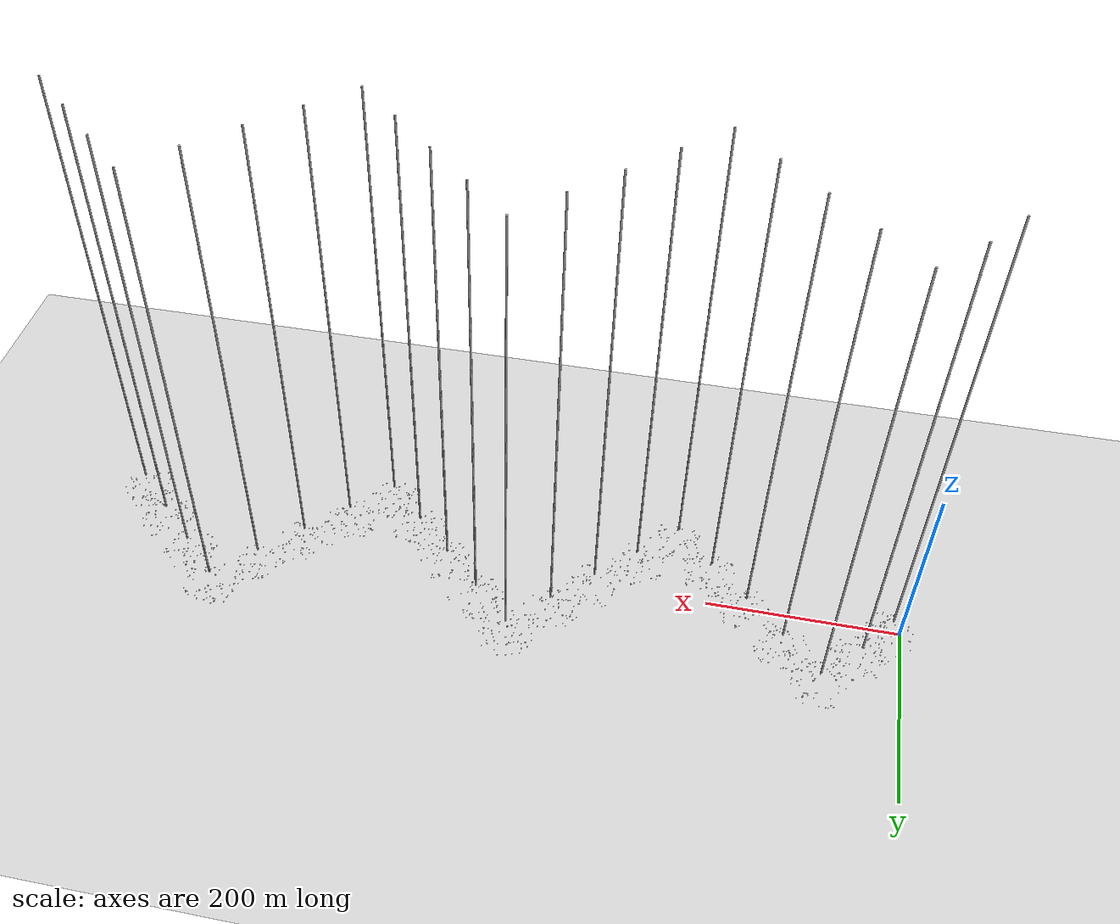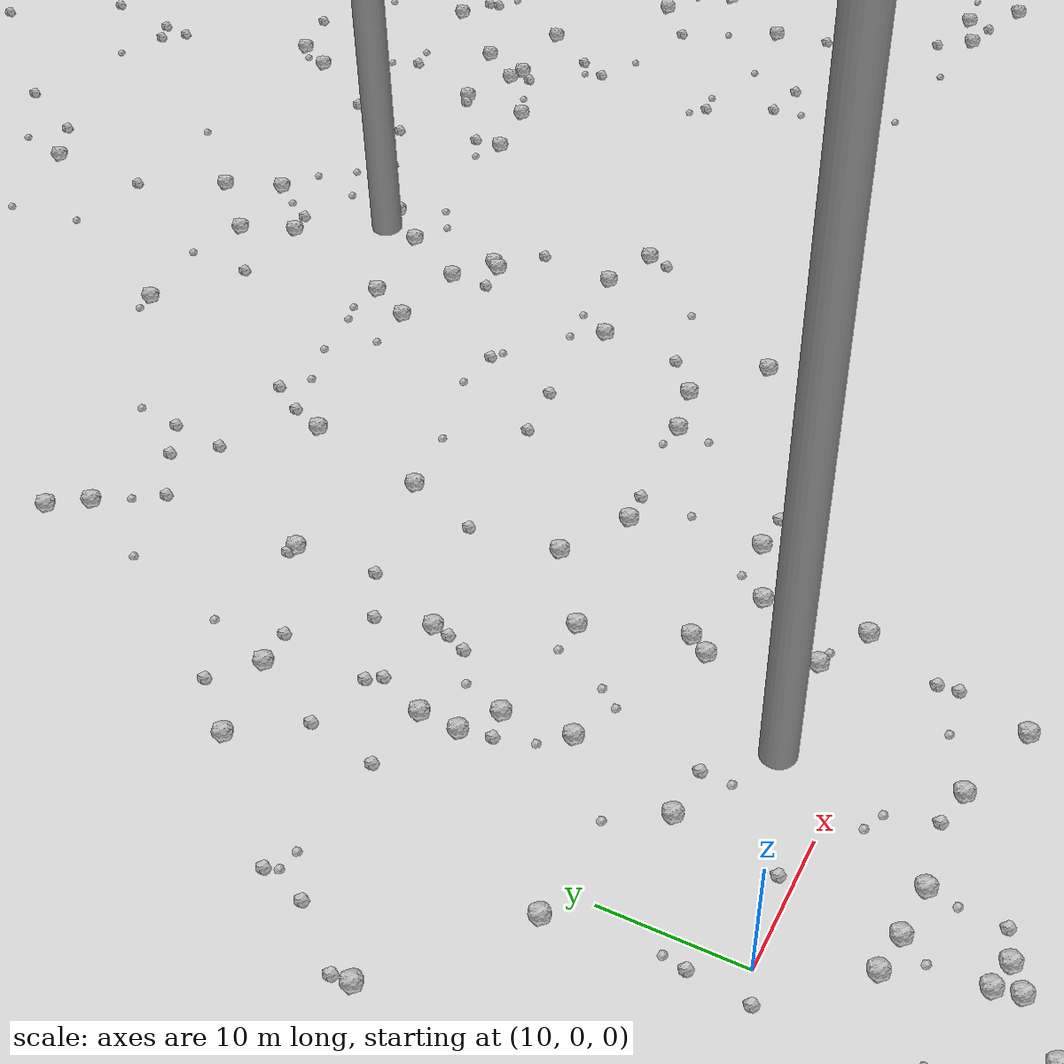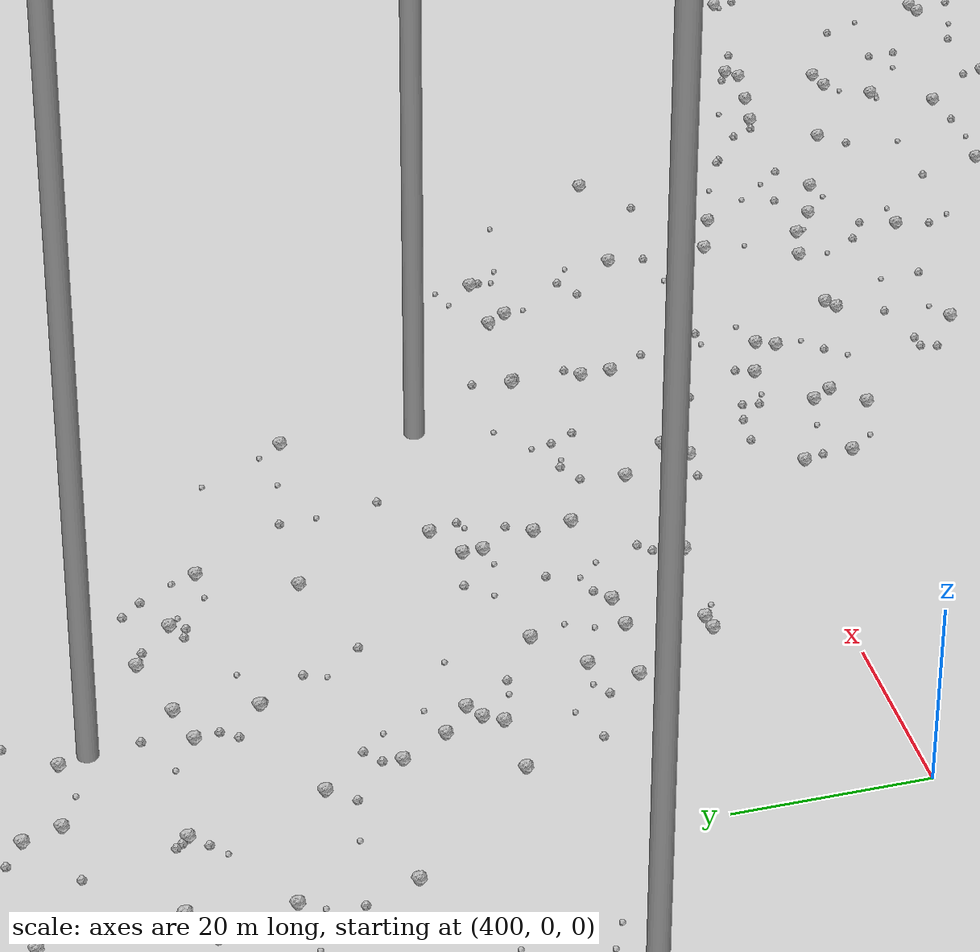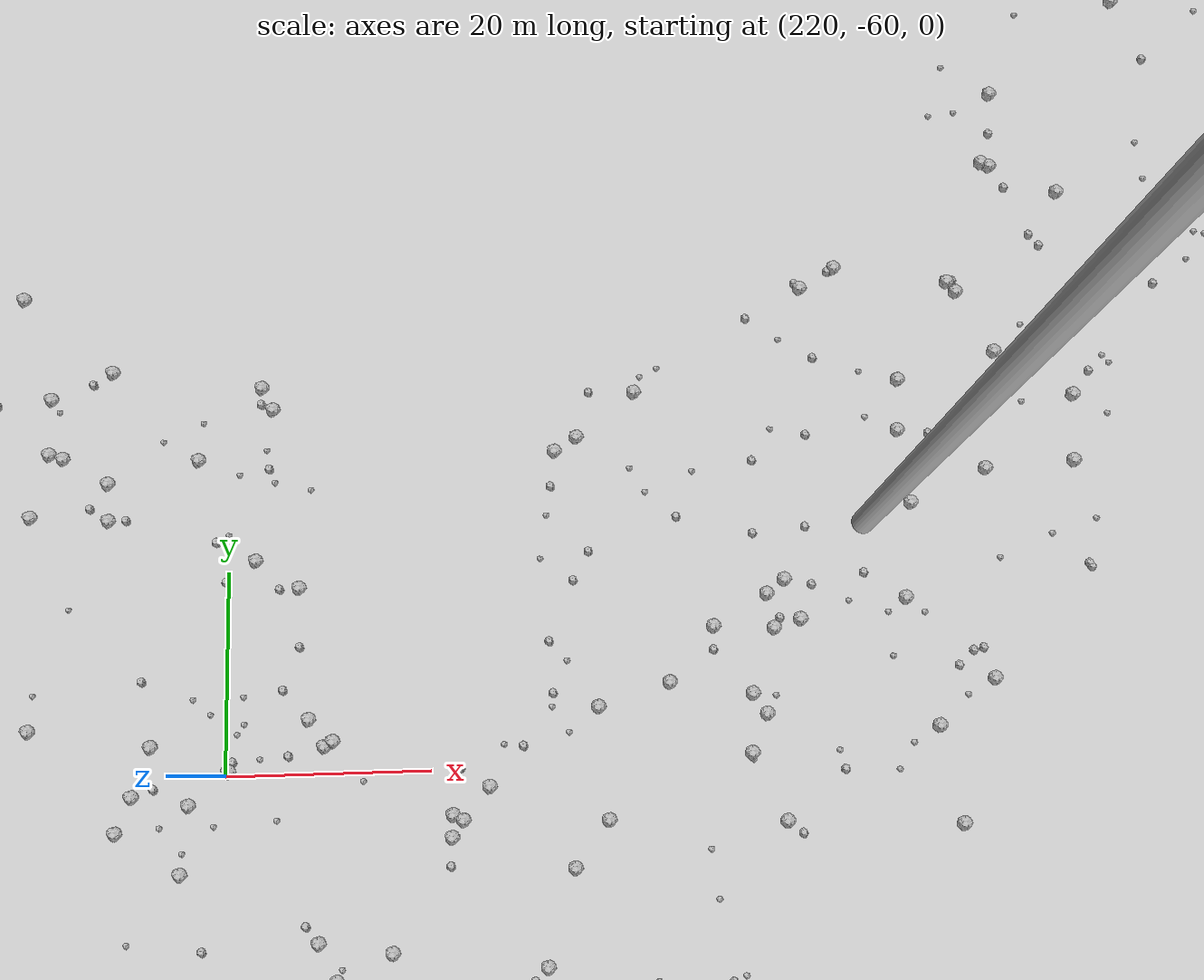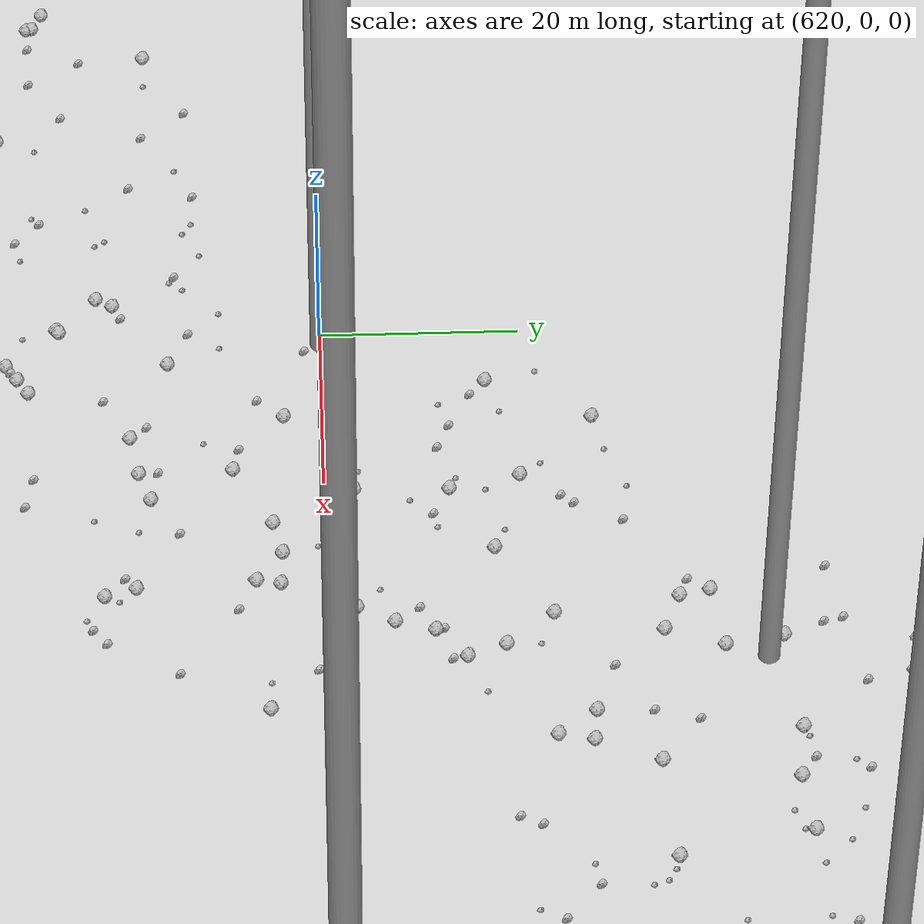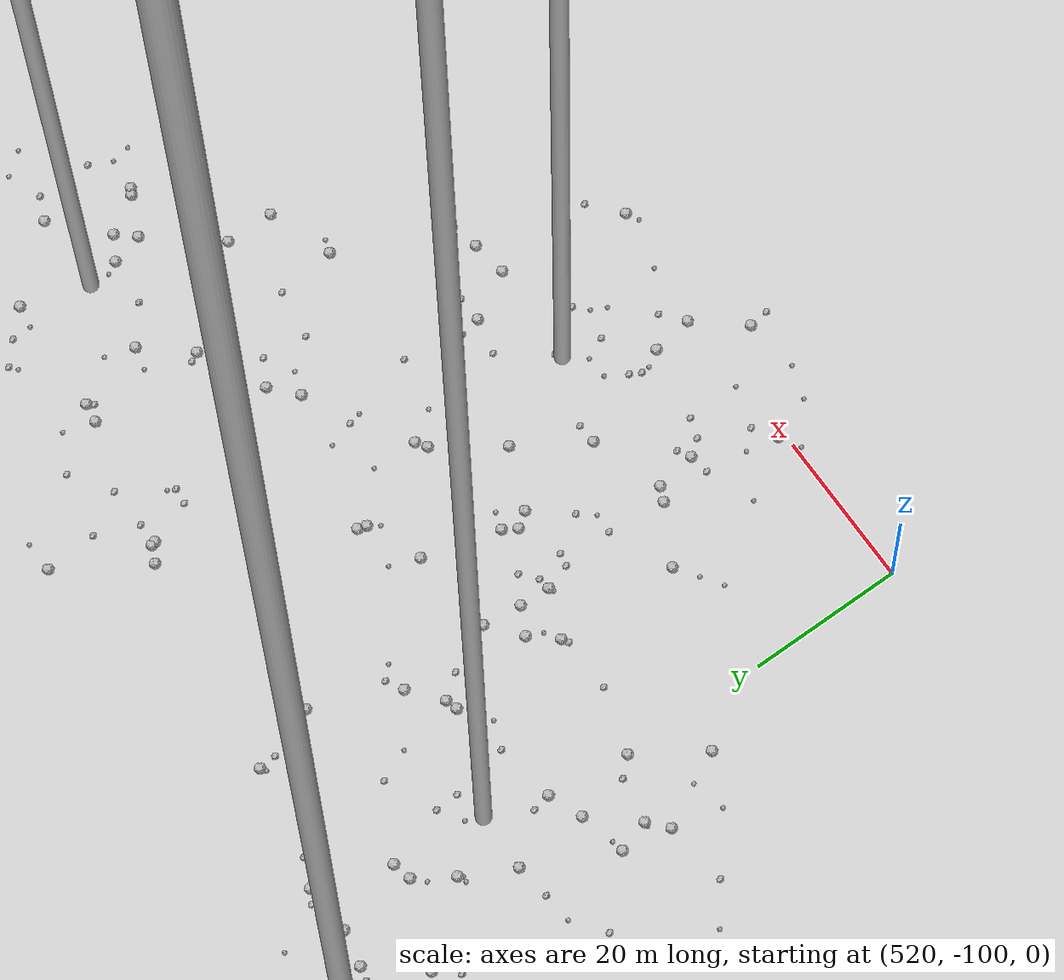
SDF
<sdf version="1.6">
 <world name="default">
  <include><uri>model://custom_ground</uri></include>
  <include><uri>model://sun</uri></include>
  <spherical_coordinates>
   <surface_model>EARTH_WGS84</surface_model>
   <latitude_deg>38.161479</latitude_deg>
   <longitude_deg>-122.454630</longitude_deg>
   <elevation>488.0</elevation>
   <heading_deg>90</heading_deg>
  </spherical_coordinates>
  <model name="rock1_0_0">
   <include><uri>model://rock1</uri><pose>17.903374062548508 8.511614454701451 0.5 0 0 0</pose></include>
  </model>
  <model name="rock1_0_1">
   <include><uri>model://rock1</uri><pose>27.260637573479094 -7.086541901217778 0.5 0 0 0</pose></include>
  </model>
  <model name="rock1_0_2">
   <include><uri>model://rock1</uri><pose>14.779956994602479 -12.641113234168863 0.5 0 0 0</pose></include>
  </model>
  <model name="rock1_0_3">
   <include><uri>model://rock1</uri><pose>15.123895841084881 -14.343905718552996 0.5 0 0 0</pose></include>
  </model>
  <model name="rock1_0_4">
   <include><uri>model://rock1</uri><pose>15.819725329030284 -6.9025398319711435 0.5 0 0 0</pose></include>
  </model>
  <model name="rock1_0_5">
   <include><uri>model://rock1</uri><pose>33.55730242436785 -9.331261969817124 0.5 0 0 0</pose></include>
  </model>
  <model name="rock1_0_6">
   <include><uri>model://rock1</uri><pose>29.363323165809675 20.66538057653038 0.5 0 0 0</pose></include>
  </model>
  <model name="rock1_0_7">
   <include><uri>model://rock1</uri><pose>20.716434089560558 16.673784464941583 0.5 0 0 0</pose></include>
  </model>
  <model name="rock1_0_8">
   <include><uri>model://rock1</uri><pose>19.584976625302282 -7.167884821622842 0.5 0 0 0</pose></include>
  </model>
  <model name="rock1_0_9">
   <include><uri>model://rock1</uri><pose>2.004655973680997 -4.438253963330915 0.5 0 0 0</pose></include>
  </model>
  <model name="rock1_0_10">
   <include><uri>model://rock1</uri><pose>-8.27162398100198 -7.219571946528035 0.5 0 0 0</pose></include>
  </model>
  <model name="rock1_0_11">
   <include><uri>model://rock1</uri><pose>5.675184436543383 -24.49783657123738 0.5 0 0 0</pose></include>
  </model>
  <model name="rock1_0_12">
   <include><uri>model://rock1</uri><pose>7.865549214750786 12.595086772178313 0.5 0 0 0</pose></include>
  </model>
  <model name="rock1_0_13">
   <include><uri>model://rock1</uri><pose>30.79203036621226 11.815364736468922 0.5 0 0 0</pose></include>
  </model>
  <model name="rock1_0_14">
   <include><uri>model://rock1</uri><pose>10.031627144665258 -18.646837776206993 0.5 0 0 0</pose></include>
  </model>
  <model name="rock1_0_15">
   <include><uri>model://rock1</uri><pose>-0.8237892630308998 20.17377706650216 0.5 0 0 0</pose></include>
  </model>
  <model name="rock1_0_16">
   <include><uri>model://rock1</uri><pose>-1.9208194834601642 8.244272644460949 0.5 0 0 0</pose></include>
  </model>
  <model name="rock1_0_17">
   <include><uri>model://rock1</uri><pose>37.17501126581183 2.69634624218142 0.5 0 0 0</pose></include>
  </model>
  <model name="rock1_0_18">
   <include><uri>model://rock1</uri><pose>12.507820767620444 -22.234153289869067 0.5 0 0 0</pose></include>
  </model>
  <model name="rock1_0_19">
   <include><uri>model://rock1</uri><pose>11.734596295507913 -17.348721622298193 0.5 0 0 0</pose></include>
  </model>
  <model name="rock1_0_20">
   <include><uri>model://rock1</uri><pose>-9.248485987300707 -11.716613627259253 0.5 0 0 0</pose></include>
  </model>
  <model name="rock1_0_21">
   <include><uri>model://rock1</uri><pose>-9.587433940524955 6.754189864909804 0.5 0 0 0</pose></include>
  </model>
  <model name="rock1_0_22">
   <include><uri>model://rock1</uri><pose>16.836864529756667 -13.155514997014016 0.5 0 0 0</pose></include>
  </model>
  <model name="rock1_0_23">
   <include><uri>model://rock1</uri><pose>33.262824325252275 4.791301548454371 0.5 0 0 0</pose></include>
  </model>
  <model name="rock1_0_24">
   <include><uri>model://rock1</uri><pose>17.943655220759304 23.533589793532798 0.5 0 0 0</pose></include>
  </model>
  <model name="rock1_0_25">
   <include><uri>model://rock1</uri><pose>20.428646234180256 21.734862199250188 0.5 0 0 0</pose></include>
  </model>
  <model name="rock1_0_26">
   <include><uri>model://rock1</uri><pose>13.001677334435335 -6.517987463725497 0.5 0 0 0</pose></include>
  </model>
  <model name="rock2_0_0">
   <include><uri>model://rock2</uri><pose>-1.1702287834888772 -9.263075284451723 0.3 0 0 0</pose></include>
  </model>
  <model name="rock2_0_1">
   <include><uri>model://rock2</uri><pose>17.459504852083263 -23.886236529729942 0.3 0 0 0</pose></include>
  </model>
  <model name="rock2_0_2">
   <include><uri>model://rock2</uri><pose>33.44205934083286 -13.535058863372317 0.3 0 0 0</pose></include>
  </model>
  <model name="rock2_0_3">
   <include><uri>model://rock2</uri><pose>-0.9211617142711219 21.582006921494965 0.3 0 0 0</pose></include>
  </model>
  <model name="rock2_0_4">
   <include><uri>model://rock2</uri><pose>21.63449989225915 8.34013250087758 0.3 0 0 0</pose></include>
  </model>
  <model name="rock2_0_5">
   <include><uri>model://rock2</uri><pose>34.9877450809209 -4.277845588263304 0.3 0 0 0</pose></include>
  </model>
  <model name="rock2_0_6">
   <include><uri>model://rock2</uri><pose>24.467259392778644 -6.456225016779882 0.3 0 0 0</pose></include>
  </model>
  <model name="rock2_0_7">
   <include><uri>model://rock2</uri><pose>18.99088907448109 -12.353219016835912 0.3 0 0 0</pose></include>
  </model>
  <model name="rock2_0_8">
   <include><uri>model://rock2</uri><pose>8.793341559504267 -24.85427452210774 0.3 0 0 0</pose></include>
  </model>
  <model name="rock2_0_9">
   <include><uri>model://rock2</uri><pose>7.394381446363976 -25.653886966304103 0.3 0 0 0</pose></include>
  </model>
  <model name="rock2_0_10">
   <include><uri>model://rock2</uri><pose>2.593240756112536 25.729493489826574 0.3 0 0 0</pose></include>
  </model>
  <model name="rock2_0_11">
   <include><uri>model://rock2</uri><pose>23.99573150135334 26.48134833908331 0.3 0 0 0</pose></include>
  </model>
  <model name="rock2_0_12">
   <include><uri>model://rock2</uri><pose>34.87866845877564 -2.8184510761796844 0.3 0 0 0</pose></include>
  </model>
  <model name="rock2_0_13">
   <include><uri>model://rock2</uri><pose>4.201618775953197 -12.284695036170142 0.3 0 0 0</pose></include>
  </model>
  <model name="rock2_0_14">
   <include><uri>model://rock2</uri><pose>5.474560629456743 -5.6763338981137395 0.3 0 0 0</pose></include>
  </model>
  <model name="rock2_0_15">
   <include><uri>model://rock2</uri><pose>-2.810387304183667 8.830839312979833 0.3 0 0 0</pose></include>
  </model>
  <model name="rock2_0_16">
   <include><uri>model://rock2</uri><pose>4.416010425001598 -10.38026359885356 0.3 0 0 0</pose></include>
  </model>
  <model name="rock2_0_17">
   <include><uri>model://rock2</uri><pose>8.253862537078753 3.437334307825296 0.3 0 0 0</pose></include>
  </model>
  <model name="rock2_0_18">
   <include><uri>model://rock2</uri><pose>16.815411788067188 -27.039675876134133 0.3 0 0 0</pose></include>
  </model>
  <model name="rock2_0_19">
   <include><uri>model://rock2</uri><pose>16.527085544651513 1.0504445118890402 0.3 0 0 0</pose></include>
  </model>
  <model name="rock2_0_20">
   <include><uri>model://rock2</uri><pose>3.5582239503769664 29.01902435668692 0.3 0 0 0</pose></include>
  </model>
  <model name="rock2_0_21">
   <include><uri>model://rock2</uri><pose>-13.701198336247426 -3.7677334316980335 0.3 0 0 0</pose></include>
  </model>
  <model name="rock2_0_22">
   <include><uri>model://rock2</uri><pose>7.774355240260988 -0.7933884866018808 0.3 0 0 0</pose></include>
  </model>
  <model name="rock2_0_23">
   <include><uri>model://rock2</uri><pose>-10.973334494253603 7.259136997878905 0.3 0 0 0</pose></include>
  </model>
  <model name="rock2_0_24">
   <include><uri>model://rock2</uri><pose>13.15966545543278 27.149430490652406 0.3 0 0 0</pose></include>
  </model>
  <model name="rock2_0_25">
   <include><uri>model://rock2</uri><pose>22.756660370173805 -24.612955974721917 0.3 0 0 0</pose></include>
  </model>
  <model name="rock2_0_26">
   <include><uri>model://rock2</uri><pose>-10.78573636698593 7.662729570988326 0.3 0 0 0</pose></include>
  </model>
  <model name="rock3_0_0">
   <include><uri>model://rock3</uri><pose>0.058698641481274905 10.554288195827716 0.2 0 0 0</pose></include>
  </model>
  <model name="rock3_0_1">
   <include><uri>model://rock3</uri><pose>22.00720076038276 -2.4093374992245202 0.2 0 0 0</pose></include>
  </model>
  <model name="rock3_0_2">
   <include><uri>model://rock3</uri><pose>8.389695473061487 -10.773396183943326 0.2 0 0 0</pose></include>
  </model>
  <model name="rock3_0_3">
   <include><uri>model://rock3</uri><pose>1.9678628552537205 -13.233589463192999 0.2 0 0 0</pose></include>
  </model>
  <model name="rock3_0_4">
   <include><uri>model://rock3</uri><pose>3.8489454128703358 -28.667570876450746 0.2 0 0 0</pose></include>
  </model>
  <model name="rock3_0_5">
   <include><uri>model://rock3</uri><pose>14.628921710737856 -8.845556784455852 0.2 0 0 0</pose></include>
  </model>
  <model name="rock3_0_6">
   <include><uri>model://rock3</uri><pose>5.45372665020561 27.815762722779894 0.2 0 0 0</pose></include>
  </model>
  <model name="rock3_0_7">
   <include><uri>model://rock3</uri><pose>3.1314542167554507 -16.849627228267003 0.2 0 0 0</pose></include>
  </model>
  <model name="rock3_0_8">
   <include><uri>model://rock3</uri><pose>-6.196668111786083 -4.7101682233003785 0.2 0 0 0</pose></include>
  </model>
  <model name="rock3_0_9">
   <include><uri>model://rock3</uri><pose>-11.096397692758925 18.265720746897316 0.2 0 0 0</pose></include>
  </model>
  <model name="rock3_0_10">
   <include><uri>model://rock3</uri><pose>-18.310202099482954 -3.6807782667247153 0.2 0 0 0</pose></include>
  </model>
  <model name="rock3_0_11">
   <include><uri>model://rock3</uri><pose>2.12698337196602 -20.48863462715009 0.2 0 0 0</pose></include>
  </model>
  <model name="rock3_0_12">
   <include><uri>model://rock3</uri><pose>3.9124289698605565 28.10389701490177 0.2 0 0 0</pose></include>
  </model>
  <model name="rock3_0_13">
   <include><uri>model://rock3</uri><pose>-5.584221867622276 6.340457180894013 0.2 0 0 0</pose></include>
  </model>
  <model name="rock3_0_14">
   <include><uri>model://rock3</uri><pose>34.45375663131939 4.454710983011111 0.2 0 0 0</pose></include>
  </model>
  <model name="rock3_0_15">
   <include><uri>model://rock3</uri><pose>15.541636860125955 12.258843281247607 0.2 0 0 0</pose></include>
  </model>
  <model name="rock3_0_16">
   <include><uri>model://rock3</uri><pose>23.50932381602535 -3.120996683458049 0.2 0 0 0</pose></include>
  </model>
  <model name="rock3_0_17">
   <include><uri>model://rock3</uri><pose>33.47969254033354 4.9319847477031615 0.2 0 0 0</pose></include>
  </model>
  <model name="rock3_0_18">
   <include><uri>model://rock3</uri><pose>21.579216997994862 6.1165857787377576 0.2 0 0 0</pose></include>
  </model>
  <model name="rock3_0_19">
   <include><uri>model://rock3</uri><pose>27.803063254915813 -19.41753902617327 0.2 0 0 0</pose></include>
  </model>
  <model name="rock3_0_20">
   <include><uri>model://rock3</uri><pose>19.140796629205518 -9.30304269822284 0.2 0 0 0</pose></include>
  </model>
  <model name="rock3_0_21">
   <include><uri>model://rock3</uri><pose>-5.486481794800822 5.997254801191872 0.2 0 0 0</pose></include>
  </model>
  <model name="rock3_0_22">
   <include><uri>model://rock3</uri><pose>-9.055541723860223 -2.2379579271734755 0.2 0 0 0</pose></include>
  </model>
  <model name="rock3_0_23">
   <include><uri>model://rock3</uri><pose>-0.665163255555985 -7.19522445876602 0.2 0 0 0</pose></include>
  </model>
  <model name="rock3_0_24">
   <include><uri>model://rock3</uri><pose>31.326348143344937 -4.846439163826016 0.2 0 0 0</pose></include>
  </model>
  <model name="rock3_0_25">
   <include><uri>model://rock3</uri><pose>8.557475768716444 5.03703688232374 0.2 0 0 0</pose></include>
  </model>
  <model name="rock3_0_26">
   <include><uri>model://rock3</uri><pose>26.835963993592074 20.813663125716694 0.2 0 0 0</pose></include>
  </model>
  <model name="rock1_1_0">
   <include><uri>model://rock1</uri><pose>50.46305781578863 22.490219369382157 0.5 0 0 0</pose></include>
  </model>
  <model name="rock1_1_1">
   <include><uri>model://rock1</uri><pose>24.870810244847483 57.32142601331246 0.5 0 0 0</pose></include>
  </model>
  <model name="rock1_1_2">
   <include><uri>model://rock1</uri><pose>64.46752204344918 34.88237052430215 0.5 0 0 0</pose></include>
  </model>
  <model name="rock1_1_3">
   <include><uri>model://rock1</uri><pose>41.75058824752894 12.246579615011346 0.5 0 0 0</pose></include>
  </model>
  <model name="rock1_1_4">
   <include><uri>model://rock1</uri><pose>40.0981932712826 21.76040594107654 0.5 0 0 0</pose></include>
  </model>
  <model name="rock1_1_5">
   <include><uri>model://rock1</uri><pose>58.17778979337808 32.22966539207637 0.5 0 0 0</pose></include>
  </model>
  <model name="rock1_1_6">
   <include><uri>model://rock1</uri><pose>11.13591674424693 36.89600161047203 0.5 0 0 0</pose></include>
  </model>
  <model name="rock1_1_7">
   <include><uri>model://rock1</uri><pose>36.52516473491556 37.25541288936886 0.5 0 0 0</pose></include>
  </model>
  <model name="rock1_1_8">
   <include><uri>model://rock1</uri><pose>25.039381529886587 29.29995089602093 0.5 0 0 0</pose></include>
  </model>
  <model name="rock1_1_9">
   <include><uri>model://rock1</uri><pose>54.53885176496465 23.3863238538663 0.5 0 0 0</pose></include>
  </model>
  <model name="rock1_1_10">
   <include><uri>model://rock1</uri><pose>61.98473791540161 43.80641963948883 0.5 0 0 0</pose></include>
  </model>
  <model name="rock1_1_11">
   <include><uri>model://rock1</uri><pose>27.346155366681142 41.58677619950277 0.5 0 0 0</pose></include>
  </model>
  <model name="rock1_1_12">
   <include><uri>model://rock1</uri><pose>31.81999578560788 13.32710091551619 0.5 0 0 0</pose></include>
  </model>
  <model name="rock1_1_13">
   <include><uri>model://rock1</uri><pose>37.03682056251387 10.256690587169995 0.5 0 0 0</pose></include>
  </model>
  <model name="rock1_1_14">
   <include><uri>model://rock1</uri><pose>23.07341765278847 59.99556645153329 0.5 0 0 0</pose></include>
  </model>
  <model name="rock1_1_15">
   <include><uri>model://rock1</uri><pose>68.8483526095211 33.18090030638872 0.5 0 0 0</pose></include>
  </model>
  <model name="rock1_1_16">
   <include><uri>model://rock1</uri><pose>62.508003748068475 44.445563834825464 0.5 0 0 0</pose></include>
  </model>
  <model name="rock1_1_17">
   <include><uri>model://rock1</uri><pose>55.11044005024811 51.296541394493005 0.5 0 0 0</pose></include>
  </model>
  <model name="rock1_1_18">
   <include><uri>model://rock1</uri><pose>18.129705490253354 26.472597460746073 0.5 0 0 0</pose></include>
  </model>
  <model name="rock1_1_19">
   <include><uri>model://rock1</uri><pose>62.53462976515997 51.983500091406675 0.5 0 0 0</pose></include>
  </model>
  <model name="rock1_1_20">
   <include><uri>model://rock1</uri><pose>38.682791875307366 46.75449820452704 0.5 0 0 0</pose></include>
  </model>
  <model name="rock1_1_21">
   <include><uri>model://rock1</uri><pose>53.20120565348273 47.87176400497605 0.5 0 0 0</pose></include>
  </model>
  <model name="rock1_1_22">
   <include><uri>model://rock1</uri><pose>46.31230966786803 67.31809708119033 0.5 0 0 0</pose></include>
  </model>
  <model name="rock1_1_23">
   <include><uri>model://rock1</uri><pose>35.10553395787362 24.796881656645667 0.5 0 0 0</pose></include>
  </model>
  <model name="rock1_1_24">
   <include><uri>model://rock1</uri><pose>59.487816464070065 46.73475300704543 0.5 0 0 0</pose></include>
  </model>
  <model name="rock1_1_25">
   <include><uri>model://rock1</uri><pose>59.79638336258787 18.978435382180777 0.5 0 0 0</pose></include>
  </model>
  <model name="rock1_1_26">
   <include><uri>model://rock1</uri><pose>17.358440610485886 37.84420553878226 0.5 0 0 0</pose></include>
  </model>
  <model name="rock2_1_0">
   <include><uri>model://rock2</uri><pose>19.623251684073928 30.07326682428002 0.3 0 0 0</pose></include>
  </model>
  <model name="rock2_1_1">
   <include><uri>model://rock2</uri><pose>31.4463752750368 55.200263837011626 0.3 0 0 0</pose></include>
  </model>
  <model name="rock2_1_2">
   <include><uri>model://rock2</uri><pose>51.61053337643672 39.05434414409487 0.3 0 0 0</pose></include>
  </model>
  <model name="rock2_1_3">
   <include><uri>model://rock2</uri><pose>65.08761953696441 41.09629115861759 0.3 0 0 0</pose></include>
  </model>
  <model name="rock2_1_4">
   <include><uri>model://rock2</uri><pose>57.440948569308055 25.832900175728653 0.3 0 0 0</pose></include>
  </model>
  <model name="rock2_1_5">
   <include><uri>model://rock2</uri><pose>59.412358424289025 43.645345235213576 0.3 0 0 0</pose></include>
  </model>
  <model name="rock2_1_6">
   <include><uri>model://rock2</uri><pose>39.72235123551269 49.45287189168898 0.3 0 0 0</pose></include>
  </model>
  <model name="rock2_1_7">
   <include><uri>model://rock2</uri><pose>41.38525993445275 51.984939314404116 0.3 0 0 0</pose></include>
  </model>
  <model name="rock2_1_8">
   <include><uri>model://rock2</uri><pose>27.545350646068535 35.3428722763351 0.3 0 0 0</pose></include>
  </model>
  <model name="rock2_1_9">
   <include><uri>model://rock2</uri><pose>24.690404253574943 28.0196130700299 0.3 0 0 0</pose></include>
  </model>
  <model name="rock2_1_10">
   <include><uri>model://rock2</uri><pose>44.68712983598725 12.109428009842576 0.3 0 0 0</pose></include>
  </model>
  <model name="rock2_1_11">
   <include><uri>model://rock2</uri><pose>49.78145558406072 32.9964634283797 0.3 0 0 0</pose></include>
  </model>
  <model name="rock2_1_12">
   <include><uri>model://rock2</uri><pose>23.943107031721375 33.329634300734426 0.3 0 0 0</pose></include>
  </model>
  <model name="rock2_1_13">
   <include><uri>model://rock2</uri><pose>18.336986116675984 21.299990722506948 0.3 0 0 0</pose></include>
  </model>
  <model name="rock2_1_14">
   <include><uri>model://rock2</uri><pose>34.23378880887553 56.56777617648057 0.3 0 0 0</pose></include>
  </model>
  <model name="rock2_1_15">
   <include><uri>model://rock2</uri><pose>34.30236286143777 31.64152399665995 0.3 0 0 0</pose></include>
  </model>
  <model name="rock2_1_16">
   <include><uri>model://rock2</uri><pose>68.19233185890968 31.416718446921454 0.3 0 0 0</pose></include>
  </model>
  <model name="rock2_1_17">
   <include><uri>model://rock2</uri><pose>26.652214099714243 41.895246116343635 0.3 0 0 0</pose></include>
  </model>
  <model name="rock2_1_18">
   <include><uri>model://rock2</uri><pose>45.291398017366205 32.58486539181449 0.3 0 0 0</pose></include>
  </model>
  <model name="rock2_1_19">
   <include><uri>model://rock2</uri><pose>52.52717789171073 62.46293741747893 0.3 0 0 0</pose></include>
  </model>
  <model name="rock2_1_20">
   <include><uri>model://rock2</uri><pose>18.943475237872384 31.088255376007044 0.3 0 0 0</pose></include>
  </model>
  <model name="rock2_1_21">
   <include><uri>model://rock2</uri><pose>27.662713341556213 52.86889527261782 0.3 0 0 0</pose></include>
  </model>
  <model name="rock2_1_22">
   <include><uri>model://rock2</uri><pose>20.00388792188868 37.967790157227554 0.3 0 0 0</pose></include>
  </model>
  <model name="rock2_1_23">
   <include><uri>model://rock2</uri><pose>33.68519204191361 52.347121632916625 0.3 0 0 0</pose></include>
  </model>
  <model name="rock2_1_24">
   <include><uri>model://rock2</uri><pose>14.420745538242294 40.59176408670842 0.3 0 0 0</pose></include>
  </model>
  <model name="rock2_1_25">
   <include><uri>model://rock2</uri><pose>42.49498499226836 21.956998922373202 0.3 0 0 0</pose></include>
  </model>
  <model name="rock2_1_26">
   <include><uri>model://rock2</uri><pose>14.296550378127012 32.33939977828481 0.3 0 0 0</pose></include>
  </model>
  <model name="rock3_1_0">
   <include><uri>model://rock3</uri><pose>43.3161764354532 50.2697644751804 0.2 0 0 0</pose></include>
  </model>
  <model name="rock3_1_1">
   <include><uri>model://rock3</uri><pose>34.78208101794358 60.064826366164674 0.2 0 0 0</pose></include>
  </model>
  <model name="rock3_1_2">
   <include><uri>model://rock3</uri><pose>19.092075319885424 42.921545932278825 0.2 0 0 0</pose></include>
  </model>
  <model name="rock3_1_3">
   <include><uri>model://rock3</uri><pose>56.67855943424931 34.612747375236495 0.2 0 0 0</pose></include>
  </model>
  <model name="rock3_1_4">
   <include><uri>model://rock3</uri><pose>48.38576595539731 22.831973775629397 0.2 0 0 0</pose></include>
  </model>
  <model name="rock3_1_5">
   <include><uri>model://rock3</uri><pose>42.30141526991397 17.87234924041496 0.2 0 0 0</pose></include>
  </model>
  <model name="rock3_1_6">
   <include><uri>model://rock3</uri><pose>50.894569204695955 51.51753611580048 0.2 0 0 0</pose></include>
  </model>
  <model name="rock3_1_7">
   <include><uri>model://rock3</uri><pose>21.54668447363695 24.929642528976625 0.2 0 0 0</pose></include>
  </model>
  <model name="rock3_1_8">
   <include><uri>model://rock3</uri><pose>23.960856409812173 15.242094481396595 0.2 0 0 0</pose></include>
  </model>
  <model name="rock3_1_9">
   <include><uri>model://rock3</uri><pose>63.25396036981912 26.97593865842458 0.2 0 0 0</pose></include>
  </model>
  <model name="rock3_1_10">
   <include><uri>model://rock3</uri><pose>46.81509531133687 51.26436350074045 0.2 0 0 0</pose></include>
  </model>
  <model name="rock3_1_11">
   <include><uri>model://rock3</uri><pose>52.50496629604557 38.41715525417567 0.2 0 0 0</pose></include>
  </model>
  <model name="rock3_1_12">
   <include><uri>model://rock3</uri><pose>38.48762138923857 12.414874348487306 0.2 0 0 0</pose></include>
  </model>
  <model name="rock3_1_13">
   <include><uri>model://rock3</uri><pose>21.611571689415342 51.37987602696691 0.2 0 0 0</pose></include>
  </model>
  <model name="rock3_1_14">
   <include><uri>model://rock3</uri><pose>17.67513230790532 23.2566939597894 0.2 0 0 0</pose></include>
  </model>
  <model name="rock3_1_15">
   <include><uri>model://rock3</uri><pose>67.13725248106248 51.60036600641482 0.2 0 0 0</pose></include>
  </model>
  <model name="rock3_1_16">
   <include><uri>model://rock3</uri><pose>49.421799678952304 48.02063588437449 0.2 0 0 0</pose></include>
  </model>
  <model name="rock3_1_17">
   <include><uri>model://rock3</uri><pose>44.754149878580016 67.39148493824521 0.2 0 0 0</pose></include>
  </model>
  <model name="rock3_1_18">
   <include><uri>model://rock3</uri><pose>52.40716859885118 51.93768435950704 0.2 0 0 0</pose></include>
  </model>
  <model name="rock3_1_19">
   <include><uri>model://rock3</uri><pose>59.554991379748316 34.837125141487434 0.2 0 0 0</pose></include>
  </model>
  <model name="rock3_1_20">
   <include><uri>model://rock3</uri><pose>19.118886204749927 18.561507700238685 0.2 0 0 0</pose></include>
  </model>
  <model name="rock3_1_21">
   <include><uri>model://rock3</uri><pose>25.0796882567562 16.74252839754856 0.2 0 0 0</pose></include>
  </model>
  <model name="rock3_1_22">
   <include><uri>model://rock3</uri><pose>50.016973284089225 19.84599809902603 0.2 0 0 0</pose></include>
  </model>
  <model name="rock3_1_23">
   <include><uri>model://rock3</uri><pose>41.76526970438982 37.88518425179334 0.2 0 0 0</pose></include>
  </model>
  <model name="rock3_1_24">
   <include><uri>model://rock3</uri><pose>26.31341177930734 54.91155117249194 0.2 0 0 0</pose></include>
  </model>
  <model name="rock3_1_25">
   <include><uri>model://rock3</uri><pose>65.1056559575591 50.3385965855295 0.2 0 0 0</pose></include>
  </model>
  <model name="rock3_1_26">
   <include><uri>model://rock3</uri><pose>48.12899624736501 39.54670871643573 0.2 0 0 0</pose></include>
  </model>
  <model name="rock1_2_0">
   <include><uri>model://rock1</uri><pose>91.24281165926458 60.02213250042159 0.5 0 0 0</pose></include>
  </model>
  <model name="rock1_2_1">
   <include><uri>model://rock1</uri><pose>65.92839462864798 102.89514963604908 0.5 0 0 0</pose></include>
  </model>
  <model name="rock1_2_2">
   <include><uri>model://rock1</uri><pose>105.92748103542623 77.93632009020747 0.5 0 0 0</pose></include>
  </model>
  <model name="rock1_2_3">
   <include><uri>model://rock1</uri><pose>102.32980260195829 65.90105392376384 0.5 0 0 0</pose></include>
  </model>
  <model name="rock1_2_4">
   <include><uri>model://rock1</uri><pose>84.68641540263934 76.50503828917967 0.5 0 0 0</pose></include>
  </model>
  <model name="rock1_2_5">
   <include><uri>model://rock1</uri><pose>93.17896530554704 93.55369862699811 0.5 0 0 0</pose></include>
  </model>
  <model name="rock1_2_6">
   <include><uri>model://rock1</uri><pose>65.42442795937475 55.26156409788133 0.5 0 0 0</pose></include>
  </model>
  <model name="rock1_2_7">
   <include><uri>model://rock1</uri><pose>64.09871222028559 66.10740090094826 0.5 0 0 0</pose></include>
  </model>
  <model name="rock1_2_8">
   <include><uri>model://rock1</uri><pose>89.72874289663275 93.38808622748496 0.5 0 0 0</pose></include>
  </model>
  <model name="rock1_2_9">
   <include><uri>model://rock1</uri><pose>83.94507701445639 58.477936033672655 0.5 0 0 0</pose></include>
  </model>
  <model name="rock1_2_10">
   <include><uri>model://rock1</uri><pose>100.26685469821876 79.98612626730785 0.5 0 0 0</pose></include>
  </model>
  <model name="rock1_2_11">
   <include><uri>model://rock1</uri><pose>91.61507054505344 92.94867442721545 0.5 0 0 0</pose></include>
  </model>
  <model name="rock1_2_12">
   <include><uri>model://rock1</uri><pose>94.53017991042225 98.2183232468356 0.5 0 0 0</pose></include>
  </model>
  <model name="rock1_2_13">
   <include><uri>model://rock1</uri><pose>63.63570253136993 104.79512632370421 0.5 0 0 0</pose></include>
  </model>
  <model name="rock1_2_14">
   <include><uri>model://rock1</uri><pose>57.47019550289439 66.03608451549295 0.5 0 0 0</pose></include>
  </model>
  <model name="rock1_2_15">
   <include><uri>model://rock1</uri><pose>106.3274475802008 68.48905423286068 0.5 0 0 0</pose></include>
  </model>
  <model name="rock1_2_16">
   <include><uri>model://rock1</uri><pose>89.91390643659274 55.85740550897408 0.5 0 0 0</pose></include>
  </model>
  <model name="rock1_2_17">
   <include><uri>model://rock1</uri><pose>96.9421550743821 66.10142220389389 0.5 0 0 0</pose></include>
  </model>
  <model name="rock1_2_18">
   <include><uri>model://rock1</uri><pose>105.86624063540205 69.84966372595395 0.5 0 0 0</pose></include>
  </model>
  <model name="rock1_2_19">
   <include><uri>model://rock1</uri><pose>59.21451045217748 61.72569092586982 0.5 0 0 0</pose></include>
  </model>
  <model name="rock1_2_20">
   <include><uri>model://rock1</uri><pose>83.45085519862496 52.67275631150172 0.5 0 0 0</pose></include>
  </model>
  <model name="rock1_2_21">
   <include><uri>model://rock1</uri><pose>82.85664169636547 73.41349182300698 0.5 0 0 0</pose></include>
  </model>
  <model name="rock1_2_22">
   <include><uri>model://rock1</uri><pose>62.309659142499314 70.73809193465112 0.5 0 0 0</pose></include>
  </model>
  <model name="rock1_2_23">
   <include><uri>model://rock1</uri><pose>88.52257297329811 56.44113366998222 0.5 0 0 0</pose></include>
  </model>
  <model name="rock1_2_24">
   <include><uri>model://rock1</uri><pose>77.97060146790136 52.00622023742625 0.5 0 0 0</pose></include>
  </model>
  <model name="rock1_2_25">
   <include><uri>model://rock1</uri><pose>59.55602201972437 86.46140982824855 0.5 0 0 0</pose></include>
  </model>
  <model name="rock1_2_26">
   <include><uri>model://rock1</uri><pose>85.28669257763951 68.73913919632497 0.5 0 0 0</pose></include>
  </model>
  <model name="rock2_2_0">
   <include><uri>model://rock2</uri><pose>102.53684464833242 65.6096475722265 0.3 0 0 0</pose></include>
  </model>
  <model name="rock2_2_1">
   <include><uri>model://rock2</uri><pose>82.94404564764459 58.198270540309124 0.3 0 0 0</pose></include>
  </model>
  <model name="rock2_2_2">
   <include><uri>model://rock2</uri><pose>80.14098064658803 90.07169206976477 0.3 0 0 0</pose></include>
  </model>
  <model name="rock2_2_3">
   <include><uri>model://rock2</uri><pose>89.60385182302966 77.62841171188748 0.3 0 0 0</pose></include>
  </model>
  <model name="rock2_2_4">
   <include><uri>model://rock2</uri><pose>106.46923373684419 84.66223252828064 0.3 0 0 0</pose></include>
  </model>
  <model name="rock2_2_5">
   <include><uri>model://rock2</uri><pose>106.94684505935118 79.4226321734804 0.3 0 0 0</pose></include>
  </model>
  <model name="rock2_2_6">
   <include><uri>model://rock2</uri><pose>86.83636155626354 65.45391643217391 0.3 0 0 0</pose></include>
  </model>
  <model name="rock2_2_7">
   <include><uri>model://rock2</uri><pose>81.6118457992861 88.2858049976853 0.3 0 0 0</pose></include>
  </model>
  <model name="rock2_2_8">
   <include><uri>model://rock2</uri><pose>93.50078329540305 105.95696269310585 0.3 0 0 0</pose></include>
  </model>
  <model name="rock2_2_9">
   <include><uri>model://rock2</uri><pose>61.136575247811486 62.06507827957607 0.3 0 0 0</pose></include>
  </model>
  <model name="rock2_2_10">
   <include><uri>model://rock2</uri><pose>99.75493977171865 63.65424223279784 0.3 0 0 0</pose></include>
  </model>
  <model name="rock2_2_11">
   <include><uri>model://rock2</uri><pose>77.81723264399994 54.43627976096776 0.3 0 0 0</pose></include>
  </model>
  <model name="rock2_2_12">
   <include><uri>model://rock2</uri><pose>76.143584934632 61.34278825874934 0.3 0 0 0</pose></include>
  </model>
  <model name="rock2_2_13">
   <include><uri>model://rock2</uri><pose>82.05019817168322 90.83683121516445 0.3 0 0 0</pose></include>
  </model>
  <model name="rock2_2_14">
   <include><uri>model://rock2</uri><pose>78.20854337059207 66.95214369413709 0.3 0 0 0</pose></include>
  </model>
  <model name="rock2_2_15">
   <include><uri>model://rock2</uri><pose>71.42129844195 107.43772537518817 0.3 0 0 0</pose></include>
  </model>
  <model name="rock2_2_16">
   <include><uri>model://rock2</uri><pose>66.77647609853855 94.8774227854271 0.3 0 0 0</pose></include>
  </model>
  <model name="rock2_2_17">
   <include><uri>model://rock2</uri><pose>97.8046857913088 85.22543785100572 0.3 0 0 0</pose></include>
  </model>
  <model name="rock2_2_18">
   <include><uri>model://rock2</uri><pose>99.63140980781264 64.59332624560174 0.3 0 0 0</pose></include>
  </model>
  <model name="rock2_2_19">
   <include><uri>model://rock2</uri><pose>94.16430207135168 96.45871747653177 0.3 0 0 0</pose></include>
  </model>
  <model name="rock2_2_20">
   <include><uri>model://rock2</uri><pose>88.85505369972873 54.72736789017076 0.3 0 0 0</pose></include>
  </model>
  <model name="rock2_2_21">
   <include><uri>model://rock2</uri><pose>63.330490886529404 88.55410465469498 0.3 0 0 0</pose></include>
  </model>
  <model name="rock2_2_22">
   <include><uri>model://rock2</uri><pose>83.47054061406791 97.2824706627033 0.3 0 0 0</pose></include>
  </model>
  <model name="rock2_2_23">
   <include><uri>model://rock2</uri><pose>58.83535570358274 97.93031769509783 0.3 0 0 0</pose></include>
  </model>
  <model name="rock2_2_24">
   <include><uri>model://rock2</uri><pose>77.58648967467985 106.26082338337415 0.3 0 0 0</pose></include>
  </model>
  <model name="rock2_2_25">
   <include><uri>model://rock2</uri><pose>58.9605299301124 77.74581238505247 0.3 0 0 0</pose></include>
  </model>
  <model name="rock2_2_26">
   <include><uri>model://rock2</uri><pose>71.14588780200569 59.14185380908939 0.3 0 0 0</pose></include>
  </model>
  <model name="rock3_2_0">
   <include><uri>model://rock3</uri><pose>91.3979850758495 74.7622573949017 0.2 0 0 0</pose></include>
  </model>
  <model name="rock3_2_1">
   <include><uri>model://rock3</uri><pose>89.01063973092207 65.75620838166788 0.2 0 0 0</pose></include>
  </model>
  <model name="rock3_2_2">
   <include><uri>model://rock3</uri><pose>95.99239743795184 73.29529962234284 0.2 0 0 0</pose></include>
  </model>
  <model name="rock3_2_3">
   <include><uri>model://rock3</uri><pose>85.794377009567 53.68768583731962 0.2 0 0 0</pose></include>
  </model>
  <model name="rock3_2_4">
   <include><uri>model://rock3</uri><pose>51.497498550605656 85.48926709908346 0.2 0 0 0</pose></include>
  </model>
  <model name="rock3_2_5">
   <include><uri>model://rock3</uri><pose>52.28469776525506 79.2761533685469 0.2 0 0 0</pose></include>
  </model>
  <model name="rock3_2_6">
   <include><uri>model://rock3</uri><pose>62.488007679087005 64.07684748761417 0.2 0 0 0</pose></include>
  </model>
  <model name="rock3_2_7">
   <include><uri>model://rock3</uri><pose>68.42917860889355 76.86591415432487 0.2 0 0 0</pose></include>
  </model>
  <model name="rock3_2_8">
   <include><uri>model://rock3</uri><pose>52.858987016679876 67.74503914495415 0.2 0 0 0</pose></include>
  </model>
  <model name="rock3_2_9">
   <include><uri>model://rock3</uri><pose>70.98246697513227 105.96180217943076 0.2 0 0 0</pose></include>
  </model>
  <model name="rock3_2_10">
   <include><uri>model://rock3</uri><pose>97.27916894364357 95.64221750534088 0.2 0 0 0</pose></include>
  </model>
  <model name="rock3_2_11">
   <include><uri>model://rock3</uri><pose>75.63537208281149 53.28438648869319 0.2 0 0 0</pose></include>
  </model>
  <model name="rock3_2_12">
   <include><uri>model://rock3</uri><pose>66.92142124899507 64.17730270201807 0.2 0 0 0</pose></include>
  </model>
  <model name="rock3_2_13">
   <include><uri>model://rock3</uri><pose>101.21993209917954 84.85038277375486 0.2 0 0 0</pose></include>
  </model>
  <model name="rock3_2_14">
   <include><uri>model://rock3</uri><pose>97.05098706373286 77.05983505920096 0.2 0 0 0</pose></include>
  </model>
  <model name="rock3_2_15">
   <include><uri>model://rock3</uri><pose>65.68700484391292 60.016303369595434 0.2 0 0 0</pose></include>
  </model>
  <model name="rock3_2_16">
   <include><uri>model://rock3</uri><pose>100.68035125067831 65.1284913572208 0.2 0 0 0</pose></include>
  </model>
  <model name="rock3_2_17">
   <include><uri>model://rock3</uri><pose>76.2342513782304 91.93255516518015 0.2 0 0 0</pose></include>
  </model>
  <model name="rock3_2_18">
   <include><uri>model://rock3</uri><pose>85.89399924143405 70.4735336034782 0.2 0 0 0</pose></include>
  </model>
  <model name="rock3_2_19">
   <include><uri>model://rock3</uri><pose>83.30723218328636 75.37513330527639 0.2 0 0 0</pose></include>
  </model>
  <model name="rock3_2_20">
   <include><uri>model://rock3</uri><pose>100.7380740909398 100.78255702961953 0.2 0 0 0</pose></include>
  </model>
  <model name="rock3_2_21">
   <include><uri>model://rock3</uri><pose>68.53808003819599 106.7224194328468 0.2 0 0 0</pose></include>
  </model>
  <model name="rock3_2_22">
   <include><uri>model://rock3</uri><pose>94.30964452387563 83.41312672830736 0.2 0 0 0</pose></include>
  </model>
  <model name="rock3_2_23">
   <include><uri>model://rock3</uri><pose>89.21586923973848 95.56367259319516 0.2 0 0 0</pose></include>
  </model>
  <model name="rock3_2_24">
   <include><uri>model://rock3</uri><pose>68.89903607280789 61.46799567491656 0.2 0 0 0</pose></include>
  </model>
  <model name="rock3_2_25">
   <include><uri>model://rock3</uri><pose>86.05664925110699 67.80694126960051 0.2 0 0 0</pose></include>
  </model>
  <model name="rock3_2_26">
   <include><uri>model://rock3</uri><pose>60.707745312134165 90.9016626337451 0.2 0 0 0</pose></include>
  </model>
  <model name="rock1_3_0">
   <include><uri>model://rock1</uri><pose>110.25935768630826 46.51556698116715 0.5 0 0 0</pose></include>
  </model>
  <model name="rock1_3_1">
   <include><uri>model://rock1</uri><pose>97.04641860129372 55.853812139160844 0.5 0 0 0</pose></include>
  </model>
  <model name="rock1_3_2">
   <include><uri>model://rock1</uri><pose>124.50994550454813 19.68775793279152 0.5 0 0 0</pose></include>
  </model>
  <model name="rock1_3_3">
   <include><uri>model://rock1</uri><pose>136.98629148695204 47.424938409452366 0.5 0 0 0</pose></include>
  </model>
  <model name="rock1_3_4">
   <include><uri>model://rock1</uri><pose>112.1700219872782 66.80764835092972 0.5 0 0 0</pose></include>
  </model>
  <model name="rock1_3_5">
   <include><uri>model://rock1</uri><pose>127.48649303649027 21.832864808935465 0.5 0 0 0</pose></include>
  </model>
  <model name="rock1_3_6">
   <include><uri>model://rock1</uri><pose>113.47063981960582 19.460363837654416 0.5 0 0 0</pose></include>
  </model>
  <model name="rock1_3_7">
   <include><uri>model://rock1</uri><pose>110.82858699758309 54.85700817326977 0.5 0 0 0</pose></include>
  </model>
  <model name="rock1_3_8">
   <include><uri>model://rock1</uri><pose>146.44693576992887 45.805895927015584 0.5 0 0 0</pose></include>
  </model>
  <model name="rock1_3_9">
   <include><uri>model://rock1</uri><pose>106.59585460051773 48.36496228443421 0.5 0 0 0</pose></include>
  </model>
  <model name="rock1_3_10">
   <include><uri>model://rock1</uri><pose>127.85103425163318 25.955744695232262 0.5 0 0 0</pose></include>
  </model>
  <model name="rock1_3_11">
   <include><uri>model://rock1</uri><pose>128.57076017920048 30.682885516811403 0.5 0 0 0</pose></include>
  </model>
  <model name="rock1_3_12">
   <include><uri>model://rock1</uri><pose>119.49694025122218 35.12796865590356 0.5 0 0 0</pose></include>
  </model>
  <model name="rock1_3_13">
   <include><uri>model://rock1</uri><pose>140.5793613470069 59.58399802018501 0.5 0 0 0</pose></include>
  </model>
  <model name="rock1_3_14">
   <include><uri>model://rock1</uri><pose>131.17587847997686 22.74258898990851 0.5 0 0 0</pose></include>
  </model>
  <model name="rock1_3_15">
   <include><uri>model://rock1</uri><pose>109.21287976485601 50.63197250838877 0.5 0 0 0</pose></include>
  </model>
  <model name="rock1_3_16">
   <include><uri>model://rock1</uri><pose>115.15815724440077 66.56974030034021 0.5 0 0 0</pose></include>
  </model>
  <model name="rock1_3_17">
   <include><uri>model://rock1</uri><pose>106.60569696944921 36.83810547281904 0.5 0 0 0</pose></include>
  </model>
  <model name="rock1_3_18">
   <include><uri>model://rock1</uri><pose>144.874139000679 50.568045621581334 0.5 0 0 0</pose></include>
  </model>
  <model name="rock1_3_19">
   <include><uri>model://rock1</uri><pose>126.35468803626244 15.296444854419198 0.5 0 0 0</pose></include>
  </model>
  <model name="rock1_3_20">
   <include><uri>model://rock1</uri><pose>120.78483501432183 17.035377766419458 0.5 0 0 0</pose></include>
  </model>
  <model name="rock1_3_21">
   <include><uri>model://rock1</uri><pose>130.2939416922532 63.276211300810665 0.5 0 0 0</pose></include>
  </model>
  <model name="rock1_3_22">
   <include><uri>model://rock1</uri><pose>131.61080838009798 51.70977088476249 0.5 0 0 0</pose></include>
  </model>
  <model name="rock1_3_23">
   <include><uri>model://rock1</uri><pose>114.38990084200915 50.889816647467995 0.5 0 0 0</pose></include>
  </model>
  <model name="rock1_3_24">
   <include><uri>model://rock1</uri><pose>111.14022970729957 43.476213587085276 0.5 0 0 0</pose></include>
  </model>
  <model name="rock1_3_25">
   <include><uri>model://rock1</uri><pose>116.13899935988783 46.01509741491451 0.5 0 0 0</pose></include>
  </model>
  <model name="rock1_3_26">
   <include><uri>model://rock1</uri><pose>117.16375485642307 20.871775531064202 0.5 0 0 0</pose></include>
  </model>
  <model name="rock2_3_0">
   <include><uri>model://rock2</uri><pose>97.83229497808361 31.53608065822841 0.3 0 0 0</pose></include>
  </model>
  <model name="rock2_3_1">
   <include><uri>model://rock2</uri><pose>135.11428148572543 19.799037578378623 0.3 0 0 0</pose></include>
  </model>
  <model name="rock2_3_2">
   <include><uri>model://rock2</uri><pose>123.78984550014147 48.241788105032946 0.3 0 0 0</pose></include>
  </model>
  <model name="rock2_3_3">
   <include><uri>model://rock2</uri><pose>120.72164447009263 51.822497341575556 0.3 0 0 0</pose></include>
  </model>
  <model name="rock2_3_4">
   <include><uri>model://rock2</uri><pose>93.83095964982476 51.38858777542792 0.3 0 0 0</pose></include>
  </model>
  <model name="rock2_3_5">
   <include><uri>model://rock2</uri><pose>104.32801420295377 59.229607432074985 0.3 0 0 0</pose></include>
  </model>
  <model name="rock2_3_6">
   <include><uri>model://rock2</uri><pose>132.96246001692816 24.56585551116146 0.3 0 0 0</pose></include>
  </model>
  <model name="rock2_3_7">
   <include><uri>model://rock2</uri><pose>107.36837151985718 32.03129477137763 0.3 0 0 0</pose></include>
  </model>
  <model name="rock2_3_8">
   <include><uri>model://rock2</uri><pose>137.76234031962053 63.339111642085655 0.3 0 0 0</pose></include>
  </model>
  <model name="rock2_3_9">
   <include><uri>model://rock2</uri><pose>102.62764972863836 45.13893375249601 0.3 0 0 0</pose></include>
  </model>
  <model name="rock2_3_10">
   <include><uri>model://rock2</uri><pose>96.97433116962232 27.449980234219964 0.3 0 0 0</pose></include>
  </model>
  <model name="rock2_3_11">
   <include><uri>model://rock2</uri><pose>117.04363210128454 37.693261070193664 0.3 0 0 0</pose></include>
  </model>
  <model name="rock2_3_12">
   <include><uri>model://rock2</uri><pose>116.45435390094197 18.734527398222053 0.3 0 0 0</pose></include>
  </model>
  <model name="rock2_3_13">
   <include><uri>model://rock2</uri><pose>143.10061065289554 48.14101391679582 0.3 0 0 0</pose></include>
  </model>
  <model name="rock2_3_14">
   <include><uri>model://rock2</uri><pose>111.5327839362671 22.29173077173152 0.3 0 0 0</pose></include>
  </model>
  <model name="rock2_3_15">
   <include><uri>model://rock2</uri><pose>126.37943406305881 26.330909124500913 0.3 0 0 0</pose></include>
  </model>
  <model name="rock2_3_16">
   <include><uri>model://rock2</uri><pose>91.50838010758379 37.84886973639195 0.3 0 0 0</pose></include>
  </model>
  <model name="rock2_3_17">
   <include><uri>model://rock2</uri><pose>126.22549572804681 55.25559925356384 0.3 0 0 0</pose></include>
  </model>
  <model name="rock2_3_18">
   <include><uri>model://rock2</uri><pose>145.13637900431775 52.288250255707574 0.3 0 0 0</pose></include>
  </model>
  <model name="rock2_3_19">
   <include><uri>model://rock2</uri><pose>129.30113545473773 12.584009292632798 0.3 0 0 0</pose></include>
  </model>
  <model name="rock2_3_20">
   <include><uri>model://rock2</uri><pose>92.54502655619879 48.96169994878778 0.3 0 0 0</pose></include>
  </model>
  <model name="rock2_3_21">
   <include><uri>model://rock2</uri><pose>114.80845355524276 48.837361782098064 0.3 0 0 0</pose></include>
  </model>
  <model name="rock2_3_22">
   <include><uri>model://rock2</uri><pose>137.54521517059342 38.53743022083505 0.3 0 0 0</pose></include>
  </model>
  <model name="rock2_3_23">
   <include><uri>model://rock2</uri><pose>129.66630130947044 44.990567018098176 0.3 0 0 0</pose></include>
  </model>
  <model name="rock2_3_24">
   <include><uri>model://rock2</uri><pose>94.1045671061585 32.25911116111212 0.3 0 0 0</pose></include>
  </model>
  <model name="rock2_3_25">
   <include><uri>model://rock2</uri><pose>113.16120861202015 45.24048704322975 0.3 0 0 0</pose></include>
  </model>
  <model name="rock2_3_26">
   <include><uri>model://rock2</uri><pose>136.0029451871135 60.10927094313868 0.3 0 0 0</pose></include>
  </model>
  <model name="rock3_3_0">
   <include><uri>model://rock3</uri><pose>92.20273287760475 50.502025891167385 0.2 0 0 0</pose></include>
  </model>
  <model name="rock3_3_1">
   <include><uri>model://rock3</uri><pose>141.36806344825942 51.5253088211618 0.2 0 0 0</pose></include>
  </model>
  <model name="rock3_3_2">
   <include><uri>model://rock3</uri><pose>133.96868828689153 28.342268872457076 0.2 0 0 0</pose></include>
  </model>
  <model name="rock3_3_3">
   <include><uri>model://rock3</uri><pose>141.45044543553934 36.462418273822465 0.2 0 0 0</pose></include>
  </model>
  <model name="rock3_3_4">
   <include><uri>model://rock3</uri><pose>131.8763501214416 14.757318736635314 0.2 0 0 0</pose></include>
  </model>
  <model name="rock3_3_5">
   <include><uri>model://rock3</uri><pose>138.53765145051034 60.96143208851009 0.2 0 0 0</pose></include>
  </model>
  <model name="rock3_3_6">
   <include><uri>model://rock3</uri><pose>94.46362212629296 29.66863112681643 0.2 0 0 0</pose></include>
  </model>
  <model name="rock3_3_7">
   <include><uri>model://rock3</uri><pose>113.07677245435127 66.10761424067854 0.2 0 0 0</pose></include>
  </model>
  <model name="rock3_3_8">
   <include><uri>model://rock3</uri><pose>104.58493526605875 41.04086585205758 0.2 0 0 0</pose></include>
  </model>
  <model name="rock3_3_9">
   <include><uri>model://rock3</uri><pose>108.58251743133502 53.69319639149285 0.2 0 0 0</pose></include>
  </model>
  <model name="rock3_3_10">
   <include><uri>model://rock3</uri><pose>132.90313089076915 26.81340188604142 0.2 0 0 0</pose></include>
  </model>
  <model name="rock3_3_11">
   <include><uri>model://rock3</uri><pose>135.3062429594922 62.016056268134484 0.2 0 0 0</pose></include>
  </model>
  <model name="rock3_3_12">
   <include><uri>model://rock3</uri><pose>99.31526083888552 36.1880305511667 0.2 0 0 0</pose></include>
  </model>
  <model name="rock3_3_13">
   <include><uri>model://rock3</uri><pose>93.54970583552846 38.099921203345055 0.2 0 0 0</pose></include>
  </model>
  <model name="rock3_3_14">
   <include><uri>model://rock3</uri><pose>121.6221463256741 33.103404631458744 0.2 0 0 0</pose></include>
  </model>
  <model name="rock3_3_15">
   <include><uri>model://rock3</uri><pose>121.20960841304938 21.273373916120597 0.2 0 0 0</pose></include>
  </model>
  <model name="rock3_3_16">
   <include><uri>model://rock3</uri><pose>97.15970974825447 21.566945644652733 0.2 0 0 0</pose></include>
  </model>
  <model name="rock3_3_17">
   <include><uri>model://rock3</uri><pose>90.4241920487799 39.004940422866966 0.2 0 0 0</pose></include>
  </model>
  <model name="rock3_3_18">
   <include><uri>model://rock3</uri><pose>131.68993501029803 16.72050812518818 0.2 0 0 0</pose></include>
  </model>
  <model name="rock3_3_19">
   <include><uri>model://rock3</uri><pose>106.32245300153949 20.271026597162596 0.2 0 0 0</pose></include>
  </model>
  <model name="rock3_3_20">
   <include><uri>model://rock3</uri><pose>117.4550897316371 34.51817305784758 0.2 0 0 0</pose></include>
  </model>
  <model name="rock3_3_21">
   <include><uri>model://rock3</uri><pose>117.51006365496332 67.59762040156635 0.2 0 0 0</pose></include>
  </model>
  <model name="rock3_3_22">
   <include><uri>model://rock3</uri><pose>96.0646099013188 47.02148730796811 0.2 0 0 0</pose></include>
  </model>
  <model name="rock3_3_23">
   <include><uri>model://rock3</uri><pose>134.30052439242195 35.849566071039014 0.2 0 0 0</pose></include>
  </model>
  <model name="rock3_3_24">
   <include><uri>model://rock3</uri><pose>101.43875208378111 62.39578371015288 0.2 0 0 0</pose></include>
  </model>
  <model name="rock3_3_25">
   <include><uri>model://rock3</uri><pose>108.26334921741869 27.382337323273205 0.2 0 0 0</pose></include>
  </model>
  <model name="rock3_3_26">
   <include><uri>model://rock3</uri><pose>109.49119017861571 47.68414512433291 0.2 0 0 0</pose></include>
  </model>
  <model name="rock1_4_0">
   <include><uri>model://rock1</uri><pose>165.20510785774383 -16.782883157356288 0.5 0 0 0</pose></include>
  </model>
  <model name="rock1_4_1">
   <include><uri>model://rock1</uri><pose>184.27525757264 -5.563772575187059 0.5 0 0 0</pose></include>
  </model>
  <model name="rock1_4_2">
   <include><uri>model://rock1</uri><pose>160.92388347625945 -2.235057176695552 0.5 0 0 0</pose></include>
  </model>
  <model name="rock1_4_3">
   <include><uri>model://rock1</uri><pose>175.7854021667193 -17.68121353090826 0.5 0 0 0</pose></include>
  </model>
  <model name="rock1_4_4">
   <include><uri>model://rock1</uri><pose>167.36158966789168 22.654782264727643 0.5 0 0 0</pose></include>
  </model>
  <model name="rock1_4_5">
   <include><uri>model://rock1</uri><pose>142.10556732586429 -16.43734119213522 0.5 0 0 0</pose></include>
  </model>
  <model name="rock1_4_6">
   <include><uri>model://rock1</uri><pose>138.1731054215319 16.05132467466558 0.5 0 0 0</pose></include>
  </model>
  <model name="rock1_4_7">
   <include><uri>model://rock1</uri><pose>164.04678378095196 9.972430998390045 0.5 0 0 0</pose></include>
  </model>
  <model name="rock1_4_8">
   <include><uri>model://rock1</uri><pose>179.20567268419182 21.204620219653457 0.5 0 0 0</pose></include>
  </model>
  <model name="rock1_4_9">
   <include><uri>model://rock1</uri><pose>180.40728581716084 9.49365174478632 0.5 0 0 0</pose></include>
  </model>
  <model name="rock1_4_10">
   <include><uri>model://rock1</uri><pose>184.11283402000393 8.584604280468497 0.5 0 0 0</pose></include>
  </model>
  <model name="rock1_4_11">
   <include><uri>model://rock1</uri><pose>166.344455248943 23.939586214503336 0.5 0 0 0</pose></include>
  </model>
  <model name="rock1_4_12">
   <include><uri>model://rock1</uri><pose>147.29933760362294 -2.5629139702935113 0.5 0 0 0</pose></include>
  </model>
  <model name="rock1_4_13">
   <include><uri>model://rock1</uri><pose>145.74637270964192 1.4063778484667004 0.5 0 0 0</pose></include>
  </model>
  <model name="rock1_4_14">
   <include><uri>model://rock1</uri><pose>155.0321290223491 -18.628599647751493 0.5 0 0 0</pose></include>
  </model>
  <model name="rock1_4_15">
   <include><uri>model://rock1</uri><pose>168.67982520112136 -0.6157392816802449 0.5 0 0 0</pose></include>
  </model>
  <model name="rock1_4_16">
   <include><uri>model://rock1</uri><pose>183.87354362703576 -11.349589590202562 0.5 0 0 0</pose></include>
  </model>
  <model name="rock1_4_17">
   <include><uri>model://rock1</uri><pose>159.29429851280292 4.877728305853488 0.5 0 0 0</pose></include>
  </model>
  <model name="rock1_4_18">
   <include><uri>model://rock1</uri><pose>135.18363740206706 -5.789821272253139 0.5 0 0 0</pose></include>
  </model>
  <model name="rock1_4_19">
   <include><uri>model://rock1</uri><pose>180.72183377372394 2.122701192173608 0.5 0 0 0</pose></include>
  </model>
  <model name="rock1_4_20">
   <include><uri>model://rock1</uri><pose>150.00911974185877 4.987735997559 0.5 0 0 0</pose></include>
  </model>
  <model name="rock1_4_21">
   <include><uri>model://rock1</uri><pose>160.47621813657418 -21.818189962546697 0.5 0 0 0</pose></include>
  </model>
  <model name="rock1_4_22">
   <include><uri>model://rock1</uri><pose>157.81440991078964 -26.845045854726084 0.5 0 0 0</pose></include>
  </model>
  <model name="rock1_4_23">
   <include><uri>model://rock1</uri><pose>150.74159192455488 -19.63574233386165 0.5 0 0 0</pose></include>
  </model>
  <model name="rock1_4_24">
   <include><uri>model://rock1</uri><pose>158.3833800793467 10.446127621841754 0.5 0 0 0</pose></include>
  </model>
  <model name="rock1_4_25">
   <include><uri>model://rock1</uri><pose>173.44958490595587 -3.816527661312602 0.5 0 0 0</pose></include>
  </model>
  <model name="rock1_4_26">
   <include><uri>model://rock1</uri><pose>167.42514510046647 -11.054414127443653 0.5 0 0 0</pose></include>
  </model>
  <model name="rock2_4_0">
   <include><uri>model://rock2</uri><pose>136.86993934336712 -0.19157005671754135 0.3 0 0 0</pose></include>
  </model>
  <model name="rock2_4_1">
   <include><uri>model://rock2</uri><pose>160.6179880788795 -26.026177200047055 0.3 0 0 0</pose></include>
  </model>
  <model name="rock2_4_2">
   <include><uri>model://rock2</uri><pose>187.47836181642242 -0.4019092979402714 0.3 0 0 0</pose></include>
  </model>
  <model name="rock2_4_3">
   <include><uri>model://rock2</uri><pose>169.4825574780046 10.253619589763865 0.3 0 0 0</pose></include>
  </model>
  <model name="rock2_4_4">
   <include><uri>model://rock2</uri><pose>163.26627778649765 22.42830686490796 0.3 0 0 0</pose></include>
  </model>
  <model name="rock2_4_5">
   <include><uri>model://rock2</uri><pose>180.3284657595175 19.256946269366125 0.3 0 0 0</pose></include>
  </model>
  <model name="rock2_4_6">
   <include><uri>model://rock2</uri><pose>148.05145456578563 19.558084192469288 0.3 0 0 0</pose></include>
  </model>
  <model name="rock2_4_7">
   <include><uri>model://rock2</uri><pose>153.38157356781758 -22.139061994363374 0.3 0 0 0</pose></include>
  </model>
  <model name="rock2_4_8">
   <include><uri>model://rock2</uri><pose>154.09734510214577 -9.956826600415312 0.3 0 0 0</pose></include>
  </model>
  <model name="rock2_4_9">
   <include><uri>model://rock2</uri><pose>183.91885043727925 15.675171330783812 0.3 0 0 0</pose></include>
  </model>
  <model name="rock2_4_10">
   <include><uri>model://rock2</uri><pose>147.64767903200038 -10.71922381218019 0.3 0 0 0</pose></include>
  </model>
  <model name="rock2_4_11">
   <include><uri>model://rock2</uri><pose>168.86028171028644 -8.036097745389512 0.3 0 0 0</pose></include>
  </model>
  <model name="rock2_4_12">
   <include><uri>model://rock2</uri><pose>147.78877138309397 -1.8378948205205319 0.3 0 0 0</pose></include>
  </model>
  <model name="rock2_4_13">
   <include><uri>model://rock2</uri><pose>143.92771152628063 3.678506631162982 0.3 0 0 0</pose></include>
  </model>
  <model name="rock2_4_14">
   <include><uri>model://rock2</uri><pose>151.7262436045735 -10.26160825958435 0.3 0 0 0</pose></include>
  </model>
  <model name="rock2_4_15">
   <include><uri>model://rock2</uri><pose>170.5283489525319 -20.08746450325127 0.3 0 0 0</pose></include>
  </model>
  <model name="rock2_4_16">
   <include><uri>model://rock2</uri><pose>146.97386400636302 -2.9080455104388427 0.3 0 0 0</pose></include>
  </model>
  <model name="rock2_4_17">
   <include><uri>model://rock2</uri><pose>185.78965200093887 -3.5610211694514327 0.3 0 0 0</pose></include>
  </model>
  <model name="rock2_4_18">
   <include><uri>model://rock2</uri><pose>159.10051117682602 -16.050044236324354 0.3 0 0 0</pose></include>
  </model>
  <model name="rock2_4_19">
   <include><uri>model://rock2</uri><pose>179.6830938996111 -18.309554344358027 0.3 0 0 0</pose></include>
  </model>
  <model name="rock2_4_20">
   <include><uri>model://rock2</uri><pose>175.26103504432297 -9.586335223610579 0.3 0 0 0</pose></include>
  </model>
  <model name="rock2_4_21">
   <include><uri>model://rock2</uri><pose>148.45978179291907 -26.97921540825849 0.3 0 0 0</pose></include>
  </model>
  <model name="rock2_4_22">
   <include><uri>model://rock2</uri><pose>179.92339192270282 -19.456876673028553 0.3 0 0 0</pose></include>
  </model>
  <model name="rock2_4_23">
   <include><uri>model://rock2</uri><pose>167.85568266370996 25.02791312075192 0.3 0 0 0</pose></include>
  </model>
  <model name="rock2_4_24">
   <include><uri>model://rock2</uri><pose>154.20313366860867 11.39342719398865 0.3 0 0 0</pose></include>
  </model>
  <model name="rock2_4_25">
   <include><uri>model://rock2</uri><pose>179.9209299318972 2.3324869642430883 0.3 0 0 0</pose></include>
  </model>
  <model name="rock2_4_26">
   <include><uri>model://rock2</uri><pose>134.24633847428572 10.87671301349971 0.3 0 0 0</pose></include>
  </model>
  <model name="rock3_4_0">
   <include><uri>model://rock3</uri><pose>174.67186173654443 -2.2292034591888985 0.2 0 0 0</pose></include>
  </model>
  <model name="rock3_4_1">
   <include><uri>model://rock3</uri><pose>159.40874311573398 20.312312879219213 0.2 0 0 0</pose></include>
  </model>
  <model name="rock3_4_2">
   <include><uri>model://rock3</uri><pose>145.08705972604355 13.294960701662937 0.2 0 0 0</pose></include>
  </model>
  <model name="rock3_4_3">
   <include><uri>model://rock3</uri><pose>160.38830537198677 21.436053687866128 0.2 0 0 0</pose></include>
  </model>
  <model name="rock3_4_4">
   <include><uri>model://rock3</uri><pose>168.11940152022154 -27.631518640030045 0.2 0 0 0</pose></include>
  </model>
  <model name="rock3_4_5">
   <include><uri>model://rock3</uri><pose>145.22295306713414 22.12353028941601 0.2 0 0 0</pose></include>
  </model>
  <model name="rock3_4_6">
   <include><uri>model://rock3</uri><pose>164.873902116723 27.703890350799142 0.2 0 0 0</pose></include>
  </model>
  <model name="rock3_4_7">
   <include><uri>model://rock3</uri><pose>187.10427922128957 -10.439134889593756 0.2 0 0 0</pose></include>
  </model>
  <model name="rock3_4_8">
   <include><uri>model://rock3</uri><pose>186.5927622123556 11.650554026971427 0.2 0 0 0</pose></include>
  </model>
  <model name="rock3_4_9">
   <include><uri>model://rock3</uri><pose>153.5952257928131 -1.4170401975257931 0.2 0 0 0</pose></include>
  </model>
  <model name="rock3_4_10">
   <include><uri>model://rock3</uri><pose>152.72881494090763 -10.338522268469713 0.2 0 0 0</pose></include>
  </model>
  <model name="rock3_4_11">
   <include><uri>model://rock3</uri><pose>160.41324631724993 -18.131323243987932 0.2 0 0 0</pose></include>
  </model>
  <model name="rock3_4_12">
   <include><uri>model://rock3</uri><pose>166.4271698962075 12.264071123341267 0.2 0 0 0</pose></include>
  </model>
  <model name="rock3_4_13">
   <include><uri>model://rock3</uri><pose>161.8772719400449 -23.237117674405418 0.2 0 0 0</pose></include>
  </model>
  <model name="rock3_4_14">
   <include><uri>model://rock3</uri><pose>166.79036258633965 2.364954352818188 0.2 0 0 0</pose></include>
  </model>
  <model name="rock3_4_15">
   <include><uri>model://rock3</uri><pose>141.92872682927177 16.98314915955045 0.2 0 0 0</pose></include>
  </model>
  <model name="rock3_4_16">
   <include><uri>model://rock3</uri><pose>163.82431055900102 -12.753516567348257 0.2 0 0 0</pose></include>
  </model>
  <model name="rock3_4_17">
   <include><uri>model://rock3</uri><pose>130.76924181832925 3.017132902811717 0.2 0 0 0</pose></include>
  </model>
  <model name="rock3_4_18">
   <include><uri>model://rock3</uri><pose>157.37149713826616 -6.757089591424542 0.2 0 0 0</pose></include>
  </model>
  <model name="rock3_4_19">
   <include><uri>model://rock3</uri><pose>188.04626432535335 -9.791045675703892 0.2 0 0 0</pose></include>
  </model>
  <model name="rock3_4_20">
   <include><uri>model://rock3</uri><pose>157.04945818764955 10.603177560676748 0.2 0 0 0</pose></include>
  </model>
  <model name="rock3_4_21">
   <include><uri>model://rock3</uri><pose>169.19989668557497 -2.2111640508486303 0.2 0 0 0</pose></include>
  </model>
  <model name="rock3_4_22">
   <include><uri>model://rock3</uri><pose>164.63986150963444 -1.3573649148507556 0.2 0 0 0</pose></include>
  </model>
  <model name="rock3_4_23">
   <include><uri>model://rock3</uri><pose>159.35320366328475 -9.286374526988514 0.2 0 0 0</pose></include>
  </model>
  <model name="rock3_4_24">
   <include><uri>model://rock3</uri><pose>175.93122960078477 1.2934874567343009 0.2 0 0 0</pose></include>
  </model>
  <model name="rock3_4_25">
   <include><uri>model://rock3</uri><pose>188.90997058917333 2.4385182513098442 0.2 0 0 0</pose></include>
  </model>
  <model name="rock3_4_26">
   <include><uri>model://rock3</uri><pose>179.74354667236437 13.946869114939382 0.2 0 0 0</pose></include>
  </model>
  <model name="rock1_5_0">
   <include><uri>model://rock1</uri><pose>201.8204844645351 -27.582572608891084 0.5 0 0 0</pose></include>
  </model>
  <model name="rock1_5_1">
   <include><uri>model://rock1</uri><pose>188.70939498474775 -25.464547375090277 0.5 0 0 0</pose></include>
  </model>
  <model name="rock1_5_2">
   <include><uri>model://rock1</uri><pose>224.31691291145768 -23.559595855606823 0.5 0 0 0</pose></include>
  </model>
  <model name="rock1_5_3">
   <include><uri>model://rock1</uri><pose>212.6618815081686 -57.01983306986171 0.5 0 0 0</pose></include>
  </model>
  <model name="rock1_5_4">
   <include><uri>model://rock1</uri><pose>200.11409501855834 -33.97188080900965 0.5 0 0 0</pose></include>
  </model>
  <model name="rock1_5_5">
   <include><uri>model://rock1</uri><pose>178.41546306991597 -60.721645655233445 0.5 0 0 0</pose></include>
  </model>
  <model name="rock1_5_6">
   <include><uri>model://rock1</uri><pose>201.89322972013608 -21.89793659946809 0.5 0 0 0</pose></include>
  </model>
  <model name="rock1_5_7">
   <include><uri>model://rock1</uri><pose>207.97276412038954 -34.51604451705252 0.5 0 0 0</pose></include>
  </model>
  <model name="rock1_5_8">
   <include><uri>model://rock1</uri><pose>203.23613722322972 -28.04800113461939 0.5 0 0 0</pose></include>
  </model>
  <model name="rock1_5_9">
   <include><uri>model://rock1</uri><pose>210.92662916870393 -61.773157326057394 0.5 0 0 0</pose></include>
  </model>
  <model name="rock1_5_10">
   <include><uri>model://rock1</uri><pose>177.90314610883004 -26.99958350050335 0.5 0 0 0</pose></include>
  </model>
  <model name="rock1_5_11">
   <include><uri>model://rock1</uri><pose>188.31705191108287 -14.230884752740721 0.5 0 0 0</pose></include>
  </model>
  <model name="rock1_5_12">
   <include><uri>model://rock1</uri><pose>190.61217055695525 -54.33685523458596 0.5 0 0 0</pose></include>
  </model>
  <model name="rock1_5_13">
   <include><uri>model://rock1</uri><pose>200.65604952199595 -55.184043743162924 0.5 0 0 0</pose></include>
  </model>
  <model name="rock1_5_14">
   <include><uri>model://rock1</uri><pose>207.82090668925053 -30.719860539175926 0.5 0 0 0</pose></include>
  </model>
  <model name="rock1_5_15">
   <include><uri>model://rock1</uri><pose>209.41683737096258 -65.18366675435375 0.5 0 0 0</pose></include>
  </model>
  <model name="rock1_5_16">
   <include><uri>model://rock1</uri><pose>177.86910540775008 -59.02547395423183 0.5 0 0 0</pose></include>
  </model>
  <model name="rock1_5_17">
   <include><uri>model://rock1</uri><pose>222.74995108209484 -38.963494275713956 0.5 0 0 0</pose></include>
  </model>
  <model name="rock1_5_18">
   <include><uri>model://rock1</uri><pose>227.0713531972582 -41.79445475348676 0.5 0 0 0</pose></include>
  </model>
  <model name="rock1_5_19">
   <include><uri>model://rock1</uri><pose>192.167181950989 -16.240272830671096 0.5 0 0 0</pose></include>
  </model>
  <model name="rock1_5_20">
   <include><uri>model://rock1</uri><pose>198.736866791496 -11.266252199046946 0.5 0 0 0</pose></include>
  </model>
  <model name="rock1_5_21">
   <include><uri>model://rock1</uri><pose>191.1874105743232 -12.260831124343248 0.5 0 0 0</pose></include>
  </model>
  <model name="rock1_5_22">
   <include><uri>model://rock1</uri><pose>220.33305959181524 -59.58282015193291 0.5 0 0 0</pose></include>
  </model>
  <model name="rock1_5_23">
   <include><uri>model://rock1</uri><pose>223.1823359225845 -21.272270268945427 0.5 0 0 0</pose></include>
  </model>
  <model name="rock1_5_24">
   <include><uri>model://rock1</uri><pose>216.88363831342386 -28.580324525863254 0.5 0 0 0</pose></include>
  </model>
  <model name="rock1_5_25">
   <include><uri>model://rock1</uri><pose>190.31505475246564 -25.02716330370808 0.5 0 0 0</pose></include>
  </model>
  <model name="rock1_5_26">
   <include><uri>model://rock1</uri><pose>208.03777312912737 -19.25823423024991 0.5 0 0 0</pose></include>
  </model>
  <model name="rock2_5_0">
   <include><uri>model://rock2</uri><pose>225.4768570905858 -51.84814597319987 0.3 0 0 0</pose></include>
  </model>
  <model name="rock2_5_1">
   <include><uri>model://rock2</uri><pose>193.36314255212935 -67.4400006055855 0.3 0 0 0</pose></include>
  </model>
  <model name="rock2_5_2">
   <include><uri>model://rock2</uri><pose>177.8545834220542 -24.393936462389917 0.3 0 0 0</pose></include>
  </model>
  <model name="rock2_5_3">
   <include><uri>model://rock2</uri><pose>227.08719821981467 -47.6317315165564 0.3 0 0 0</pose></include>
  </model>
  <model name="rock2_5_4">
   <include><uri>model://rock2</uri><pose>209.66105546742773 -34.50501388112993 0.3 0 0 0</pose></include>
  </model>
  <model name="rock2_5_5">
   <include><uri>model://rock2</uri><pose>225.0766275497782 -41.85614955401484 0.3 0 0 0</pose></include>
  </model>
  <model name="rock2_5_6">
   <include><uri>model://rock2</uri><pose>196.32381746316756 -22.304564820811642 0.3 0 0 0</pose></include>
  </model>
  <model name="rock2_5_7">
   <include><uri>model://rock2</uri><pose>182.97822458919777 -60.70809277584386 0.3 0 0 0</pose></include>
  </model>
  <model name="rock2_5_8">
   <include><uri>model://rock2</uri><pose>174.37815283116805 -48.08792208767692 0.3 0 0 0</pose></include>
  </model>
  <model name="rock2_5_9">
   <include><uri>model://rock2</uri><pose>185.5425567458954 -57.064754511961716 0.3 0 0 0</pose></include>
  </model>
  <model name="rock2_5_10">
   <include><uri>model://rock2</uri><pose>218.73972767237723 -36.97601556686754 0.3 0 0 0</pose></include>
  </model>
  <model name="rock2_5_11">
   <include><uri>model://rock2</uri><pose>211.58713613626483 -50.635470781950225 0.3 0 0 0</pose></include>
  </model>
  <model name="rock2_5_12">
   <include><uri>model://rock2</uri><pose>183.3705078515048 -51.66913532536576 0.3 0 0 0</pose></include>
  </model>
  <model name="rock2_5_13">
   <include><uri>model://rock2</uri><pose>195.20580425398094 -11.50236876545101 0.3 0 0 0</pose></include>
  </model>
  <model name="rock2_5_14">
   <include><uri>model://rock2</uri><pose>223.95031833300038 -29.646372006358774 0.3 0 0 0</pose></include>
  </model>
  <model name="rock2_5_15">
   <include><uri>model://rock2</uri><pose>181.2233007372669 -30.514642613528686 0.3 0 0 0</pose></include>
  </model>
  <model name="rock2_5_16">
   <include><uri>model://rock2</uri><pose>219.76356543594673 -41.01595104607921 0.3 0 0 0</pose></include>
  </model>
  <model name="rock2_5_17">
   <include><uri>model://rock2</uri><pose>187.08330151477793 -28.08065934480163 0.3 0 0 0</pose></include>
  </model>
  <model name="rock2_5_18">
   <include><uri>model://rock2</uri><pose>175.17682963050515 -31.919564134370823 0.3 0 0 0</pose></include>
  </model>
  <model name="rock2_5_19">
   <include><uri>model://rock2</uri><pose>183.1976715611437 -28.515821275390955 0.3 0 0 0</pose></include>
  </model>
  <model name="rock2_5_20">
   <include><uri>model://rock2</uri><pose>206.01206396478798 -20.403372240753285 0.3 0 0 0</pose></include>
  </model>
  <model name="rock2_5_21">
   <include><uri>model://rock2</uri><pose>181.10931460450547 -44.92468790500392 0.3 0 0 0</pose></include>
  </model>
  <model name="rock2_5_22">
   <include><uri>model://rock2</uri><pose>179.66337758880215 -60.094110935107274 0.3 0 0 0</pose></include>
  </model>
  <model name="rock2_5_23">
   <include><uri>model://rock2</uri><pose>193.25021193413497 -64.02693095861423 0.3 0 0 0</pose></include>
  </model>
  <model name="rock2_5_24">
   <include><uri>model://rock2</uri><pose>212.9618717387488 -61.08980317432888 0.3 0 0 0</pose></include>
  </model>
  <model name="rock2_5_25">
   <include><uri>model://rock2</uri><pose>223.08105847519116 -22.94132711306316 0.3 0 0 0</pose></include>
  </model>
  <model name="rock2_5_26">
   <include><uri>model://rock2</uri><pose>206.00718576123097 -33.219424123100644 0.3 0 0 0</pose></include>
  </model>
  <model name="rock3_5_0">
   <include><uri>model://rock3</uri><pose>186.9611547335897 -29.749681260369925 0.2 0 0 0</pose></include>
  </model>
  <model name="rock3_5_1">
   <include><uri>model://rock3</uri><pose>216.65370439143743 -52.5685537206123 0.2 0 0 0</pose></include>
  </model>
  <model name="rock3_5_2">
   <include><uri>model://rock3</uri><pose>178.4780739299828 -33.38025404620145 0.2 0 0 0</pose></include>
  </model>
  <model name="rock3_5_3">
   <include><uri>model://rock3</uri><pose>228.11900181025314 -31.90667478798197 0.2 0 0 0</pose></include>
  </model>
  <model name="rock3_5_4">
   <include><uri>model://rock3</uri><pose>185.6051650648022 -37.256151488999684 0.2 0 0 0</pose></include>
  </model>
  <model name="rock3_5_5">
   <include><uri>model://rock3</uri><pose>218.37484712077324 -54.06759997803636 0.2 0 0 0</pose></include>
  </model>
  <model name="rock3_5_6">
   <include><uri>model://rock3</uri><pose>223.656555881967 -27.73918015345083 0.2 0 0 0</pose></include>
  </model>
  <model name="rock3_5_7">
   <include><uri>model://rock3</uri><pose>183.36390774426815 -54.47603474318114 0.2 0 0 0</pose></include>
  </model>
  <model name="rock3_5_8">
   <include><uri>model://rock3</uri><pose>173.91976706493165 -28.392549593352932 0.2 0 0 0</pose></include>
  </model>
  <model name="rock3_5_9">
   <include><uri>model://rock3</uri><pose>220.9548072683816 -30.19471370548157 0.2 0 0 0</pose></include>
  </model>
  <model name="rock3_5_10">
   <include><uri>model://rock3</uri><pose>204.13585900625665 -43.3254981876746 0.2 0 0 0</pose></include>
  </model>
  <model name="rock3_5_11">
   <include><uri>model://rock3</uri><pose>219.94780688931033 -36.31594263799555 0.2 0 0 0</pose></include>
  </model>
  <model name="rock3_5_12">
   <include><uri>model://rock3</uri><pose>224.48519110270195 -31.06264195449954 0.2 0 0 0</pose></include>
  </model>
  <model name="rock3_5_13">
   <include><uri>model://rock3</uri><pose>213.21866714855025 -26.570487113891218 0.2 0 0 0</pose></include>
  </model>
  <model name="rock3_5_14">
   <include><uri>model://rock3</uri><pose>213.56907024471136 -64.81558484278472 0.2 0 0 0</pose></include>
  </model>
  <model name="rock3_5_15">
   <include><uri>model://rock3</uri><pose>202.62021907345877 -23.194825789274574 0.2 0 0 0</pose></include>
  </model>
  <model name="rock3_5_16">
   <include><uri>model://rock3</uri><pose>221.6725730139584 -55.078816919289096 0.2 0 0 0</pose></include>
  </model>
  <model name="rock3_5_17">
   <include><uri>model://rock3</uri><pose>189.35180869504038 -18.80432728531293 0.2 0 0 0</pose></include>
  </model>
  <model name="rock3_5_18">
   <include><uri>model://rock3</uri><pose>221.60870785863216 -52.428072241067916 0.2 0 0 0</pose></include>
  </model>
  <model name="rock3_5_19">
   <include><uri>model://rock3</uri><pose>187.53343301422595 -41.60472886789754 0.2 0 0 0</pose></include>
  </model>
  <model name="rock3_5_20">
   <include><uri>model://rock3</uri><pose>200.8577310366334 -51.730113675748235 0.2 0 0 0</pose></include>
  </model>
  <model name="rock3_5_21">
   <include><uri>model://rock3</uri><pose>221.01721071170394 -56.06929596844293 0.2 0 0 0</pose></include>
  </model>
  <model name="rock3_5_22">
   <include><uri>model://rock3</uri><pose>217.22856853346792 -24.740387117300713 0.2 0 0 0</pose></include>
  </model>
  <model name="rock3_5_23">
   <include><uri>model://rock3</uri><pose>189.87770482971874 -27.281811132763714 0.2 0 0 0</pose></include>
  </model>
  <model name="rock3_5_24">
   <include><uri>model://rock3</uri><pose>190.80533075031764 -46.142985546770134 0.2 0 0 0</pose></include>
  </model>
  <model name="rock3_5_25">
   <include><uri>model://rock3</uri><pose>190.11359046784082 -41.29963416787276 0.2 0 0 0</pose></include>
  </model>
  <model name="rock3_5_26">
   <include><uri>model://rock3</uri><pose>189.12052290381268 -51.39188477511796 0.2 0 0 0</pose></include>
  </model>
  <model name="rock1_6_0">
   <include><uri>model://rock1</uri><pose>241.9045746987014 -102.44064604352943 0.5 0 0 0</pose></include>
  </model>
  <model name="rock1_6_1">
   <include><uri>model://rock1</uri><pose>215.77267455678086 -69.24180622413715 0.5 0 0 0</pose></include>
  </model>
  <model name="rock1_6_2">
   <include><uri>model://rock1</uri><pose>242.00855765986776 -66.44979734256782 0.5 0 0 0</pose></include>
  </model>
  <model name="rock1_6_3">
   <include><uri>model://rock1</uri><pose>220.0209574067129 -80.62924251200441 0.5 0 0 0</pose></include>
  </model>
  <model name="rock1_6_4">
   <include><uri>model://rock1</uri><pose>230.91879515643294 -79.58528589136422 0.5 0 0 0</pose></include>
  </model>
  <model name="rock1_6_5">
   <include><uri>model://rock1</uri><pose>243.11889874895894 -64.83486369110659 0.5 0 0 0</pose></include>
  </model>
  <model name="rock1_6_6">
   <include><uri>model://rock1</uri><pose>253.84921129094175 -69.66644869382192 0.5 0 0 0</pose></include>
  </model>
  <model name="rock1_6_7">
   <include><uri>model://rock1</uri><pose>242.10794299865273 -64.29442371787016 0.5 0 0 0</pose></include>
  </model>
  <model name="rock1_6_8">
   <include><uri>model://rock1</uri><pose>251.03805057446988 -78.80478142424585 0.5 0 0 0</pose></include>
  </model>
  <model name="rock1_6_9">
   <include><uri>model://rock1</uri><pose>216.47020430086053 -62.73463496864626 0.5 0 0 0</pose></include>
  </model>
  <model name="rock1_6_10">
   <include><uri>model://rock1</uri><pose>245.71176204927963 -61.70741573439281 0.5 0 0 0</pose></include>
  </model>
  <model name="rock1_6_11">
   <include><uri>model://rock1</uri><pose>225.08786862479548 -98.42113919654213 0.5 0 0 0</pose></include>
  </model>
  <model name="rock1_6_12">
   <include><uri>model://rock1</uri><pose>251.36009905942421 -83.86324128637645 0.5 0 0 0</pose></include>
  </model>
  <model name="rock1_6_13">
   <include><uri>model://rock1</uri><pose>221.60559824376523 -94.36227798415305 0.5 0 0 0</pose></include>
  </model>
  <model name="rock1_6_14">
   <include><uri>model://rock1</uri><pose>261.6747581209353 -92.43622756960761 0.5 0 0 0</pose></include>
  </model>
  <model name="rock1_6_15">
   <include><uri>model://rock1</uri><pose>218.20710376883181 -88.80690307096975 0.5 0 0 0</pose></include>
  </model>
  <model name="rock1_6_16">
   <include><uri>model://rock1</uri><pose>260.3486458355436 -86.5410279633937 0.5 0 0 0</pose></include>
  </model>
  <model name="rock1_6_17">
   <include><uri>model://rock1</uri><pose>230.42335406026427 -56.9418438710534 0.5 0 0 0</pose></include>
  </model>
  <model name="rock1_6_18">
   <include><uri>model://rock1</uri><pose>257.2217236129651 -65.22222795587484 0.5 0 0 0</pose></include>
  </model>
  <model name="rock1_6_19">
   <include><uri>model://rock1</uri><pose>249.33610243568535 -84.03143663191081 0.5 0 0 0</pose></include>
  </model>
  <model name="rock1_6_20">
   <include><uri>model://rock1</uri><pose>216.63891621132498 -92.33437702711028 0.5 0 0 0</pose></include>
  </model>
  <model name="rock1_6_21">
   <include><uri>model://rock1</uri><pose>229.1612074426062 -75.99819327130086 0.5 0 0 0</pose></include>
  </model>
  <model name="rock1_6_22">
   <include><uri>model://rock1</uri><pose>241.69603125914796 -97.78029310095289 0.5 0 0 0</pose></include>
  </model>
  <model name="rock1_6_23">
   <include><uri>model://rock1</uri><pose>255.6229538719162 -95.06330204939078 0.5 0 0 0</pose></include>
  </model>
  <model name="rock1_6_24">
   <include><uri>model://rock1</uri><pose>229.61405572034167 -57.41088689588969 0.5 0 0 0</pose></include>
  </model>
  <model name="rock1_6_25">
   <include><uri>model://rock1</uri><pose>228.06763810634834 -54.75232264760334 0.5 0 0 0</pose></include>
  </model>
  <model name="rock1_6_26">
   <include><uri>model://rock1</uri><pose>236.2535232215393 -77.09972789619839 0.5 0 0 0</pose></include>
  </model>
  <model name="rock2_6_0">
   <include><uri>model://rock2</uri><pose>252.00852217616563 -52.866772286799716 0.3 0 0 0</pose></include>
  </model>
  <model name="rock2_6_1">
   <include><uri>model://rock2</uri><pose>242.13219051586776 -64.25587917251192 0.3 0 0 0</pose></include>
  </model>
  <model name="rock2_6_2">
   <include><uri>model://rock2</uri><pose>242.84528271209376 -59.876065646465605 0.3 0 0 0</pose></include>
  </model>
  <model name="rock2_6_3">
   <include><uri>model://rock2</uri><pose>226.07075094963514 -58.257497989517105 0.3 0 0 0</pose></include>
  </model>
  <model name="rock2_6_4">
   <include><uri>model://rock2</uri><pose>223.5295847079464 -100.4961613884724 0.3 0 0 0</pose></include>
  </model>
  <model name="rock2_6_5">
   <include><uri>model://rock2</uri><pose>258.2110962931948 -83.04944352201926 0.3 0 0 0</pose></include>
  </model>
  <model name="rock2_6_6">
   <include><uri>model://rock2</uri><pose>253.76858453316245 -96.09736600165706 0.3 0 0 0</pose></include>
  </model>
  <model name="rock2_6_7">
   <include><uri>model://rock2</uri><pose>256.66288465825505 -84.86020868141907 0.3 0 0 0</pose></include>
  </model>
  <model name="rock2_6_8">
   <include><uri>model://rock2</uri><pose>236.29812720326686 -100.29870406989151 0.3 0 0 0</pose></include>
  </model>
  <model name="rock2_6_9">
   <include><uri>model://rock2</uri><pose>232.62953149473708 -97.91036234424928 0.3 0 0 0</pose></include>
  </model>
  <model name="rock2_6_10">
   <include><uri>model://rock2</uri><pose>268.6204959756329 -80.65449630033979 0.3 0 0 0</pose></include>
  </model>
  <model name="rock2_6_11">
   <include><uri>model://rock2</uri><pose>259.50480468468203 -102.05874348906977 0.3 0 0 0</pose></include>
  </model>
  <model name="rock2_6_12">
   <include><uri>model://rock2</uri><pose>266.8791767579306 -90.33851022984588 0.3 0 0 0</pose></include>
  </model>
  <model name="rock2_6_13">
   <include><uri>model://rock2</uri><pose>220.11013644827995 -90.73321902834331 0.3 0 0 0</pose></include>
  </model>
  <model name="rock2_6_14">
   <include><uri>model://rock2</uri><pose>232.47913446508505 -83.31871629820265 0.3 0 0 0</pose></include>
  </model>
  <model name="rock2_6_15">
   <include><uri>model://rock2</uri><pose>241.8160506364249 -69.16945757723363 0.3 0 0 0</pose></include>
  </model>
  <model name="rock2_6_16">
   <include><uri>model://rock2</uri><pose>249.0080727815232 -57.89938165720055 0.3 0 0 0</pose></include>
  </model>
  <model name="rock2_6_17">
   <include><uri>model://rock2</uri><pose>220.62584166265054 -58.69439466653587 0.3 0 0 0</pose></include>
  </model>
  <model name="rock2_6_18">
   <include><uri>model://rock2</uri><pose>225.20853970577144 -85.58005531432444 0.3 0 0 0</pose></include>
  </model>
  <model name="rock2_6_19">
   <include><uri>model://rock2</uri><pose>221.95030839166506 -84.07643053339766 0.3 0 0 0</pose></include>
  </model>
  <model name="rock2_6_20">
   <include><uri>model://rock2</uri><pose>225.5362795713645 -82.08671158193079 0.3 0 0 0</pose></include>
  </model>
  <model name="rock2_6_21">
   <include><uri>model://rock2</uri><pose>260.6187648294433 -101.42442486677034 0.3 0 0 0</pose></include>
  </model>
  <model name="rock2_6_22">
   <include><uri>model://rock2</uri><pose>227.8569927233739 -74.4092630937655 0.3 0 0 0</pose></include>
  </model>
  <model name="rock2_6_23">
   <include><uri>model://rock2</uri><pose>232.78191229295447 -96.53445282627638 0.3 0 0 0</pose></include>
  </model>
  <model name="rock2_6_24">
   <include><uri>model://rock2</uri><pose>249.76010691606626 -80.07285995300307 0.3 0 0 0</pose></include>
  </model>
  <model name="rock2_6_25">
   <include><uri>model://rock2</uri><pose>217.9311608348963 -76.48546132661811 0.3 0 0 0</pose></include>
  </model>
  <model name="rock2_6_26">
   <include><uri>model://rock2</uri><pose>219.8393199172256 -98.93900950549869 0.3 0 0 0</pose></include>
  </model>
  <model name="rock3_6_0">
   <include><uri>model://rock3</uri><pose>215.80924051985926 -67.28561011425111 0.2 0 0 0</pose></include>
  </model>
  <model name="rock3_6_1">
   <include><uri>model://rock3</uri><pose>246.34428022315052 -85.31493145650413 0.2 0 0 0</pose></include>
  </model>
  <model name="rock3_6_2">
   <include><uri>model://rock3</uri><pose>250.0198753772545 -85.58298260883804 0.2 0 0 0</pose></include>
  </model>
  <model name="rock3_6_3">
   <include><uri>model://rock3</uri><pose>231.33567883052135 -78.54401930914995 0.2 0 0 0</pose></include>
  </model>
  <model name="rock3_6_4">
   <include><uri>model://rock3</uri><pose>216.00680339432373 -95.89495577127109 0.2 0 0 0</pose></include>
  </model>
  <model name="rock3_6_5">
   <include><uri>model://rock3</uri><pose>219.10514318099808 -98.11153797795339 0.2 0 0 0</pose></include>
  </model>
  <model name="rock3_6_6">
   <include><uri>model://rock3</uri><pose>253.48457345876975 -56.74109837744379 0.2 0 0 0</pose></include>
  </model>
  <model name="rock3_6_7">
   <include><uri>model://rock3</uri><pose>217.9148534799651 -96.84508131153119 0.2 0 0 0</pose></include>
  </model>
  <model name="rock3_6_8">
   <include><uri>model://rock3</uri><pose>247.09303076892292 -57.720688289903876 0.2 0 0 0</pose></include>
  </model>
  <model name="rock3_6_9">
   <include><uri>model://rock3</uri><pose>223.2774243117684 -58.51790927096229 0.2 0 0 0</pose></include>
  </model>
  <model name="rock3_6_10">
   <include><uri>model://rock3</uri><pose>218.83768241305933 -64.80237856005996 0.2 0 0 0</pose></include>
  </model>
  <model name="rock3_6_11">
   <include><uri>model://rock3</uri><pose>210.66486581629098 -75.71958550528683 0.2 0 0 0</pose></include>
  </model>
  <model name="rock3_6_12">
   <include><uri>model://rock3</uri><pose>260.18763029122505 -92.91507215672242 0.2 0 0 0</pose></include>
  </model>
  <model name="rock3_6_13">
   <include><uri>model://rock3</uri><pose>229.0445666070365 -84.8751265567352 0.2 0 0 0</pose></include>
  </model>
  <model name="rock3_6_14">
   <include><uri>model://rock3</uri><pose>261.48264699590663 -80.45322220366087 0.2 0 0 0</pose></include>
  </model>
  <model name="rock3_6_15">
   <include><uri>model://rock3</uri><pose>267.5454331461798 -73.02215134489515 0.2 0 0 0</pose></include>
  </model>
  <model name="rock3_6_16">
   <include><uri>model://rock3</uri><pose>237.9866989363823 -92.52427075833305 0.2 0 0 0</pose></include>
  </model>
  <model name="rock3_6_17">
   <include><uri>model://rock3</uri><pose>239.2030959442006 -103.08673976551134 0.2 0 0 0</pose></include>
  </model>
  <model name="rock3_6_18">
   <include><uri>model://rock3</uri><pose>249.53920913754814 -94.66949894835372 0.2 0 0 0</pose></include>
  </model>
  <model name="rock3_6_19">
   <include><uri>model://rock3</uri><pose>266.94719491969033 -68.31919797620986 0.2 0 0 0</pose></include>
  </model>
  <model name="rock3_6_20">
   <include><uri>model://rock3</uri><pose>269.82350797003727 -80.16302810784872 0.2 0 0 0</pose></include>
  </model>
  <model name="rock3_6_21">
   <include><uri>model://rock3</uri><pose>243.97773287263234 -92.27662192393943 0.2 0 0 0</pose></include>
  </model>
  <model name="rock3_6_22">
   <include><uri>model://rock3</uri><pose>224.96429123385698 -64.41502472407606 0.2 0 0 0</pose></include>
  </model>
  <model name="rock3_6_23">
   <include><uri>model://rock3</uri><pose>216.82921455427783 -93.9200790773497 0.2 0 0 0</pose></include>
  </model>
  <model name="rock3_6_24">
   <include><uri>model://rock3</uri><pose>233.36599756807317 -60.88853806068442 0.2 0 0 0</pose></include>
  </model>
  <model name="rock3_6_25">
   <include><uri>model://rock3</uri><pose>251.63995562648506 -100.50572435061653 0.2 0 0 0</pose></include>
  </model>
  <model name="rock3_6_26">
   <include><uri>model://rock3</uri><pose>251.8598639764641 -54.22128249007237 0.2 0 0 0</pose></include>
  </model>
  <model name="rock1_7_0">
   <include><uri>model://rock1</uri><pose>252.6933279010397 -28.656473191338605 0.5 0 0 0</pose></include>
  </model>
  <model name="rock1_7_1">
   <include><uri>model://rock1</uri><pose>278.22238580117033 -12.313797066771983 0.5 0 0 0</pose></include>
  </model>
  <model name="rock1_7_2">
   <include><uri>model://rock1</uri><pose>274.4679772852409 -65.79771184751351 0.5 0 0 0</pose></include>
  </model>
  <model name="rock1_7_3">
   <include><uri>model://rock1</uri><pose>281.81925512145193 -10.233893099729514 0.5 0 0 0</pose></include>
  </model>
  <model name="rock1_7_4">
   <include><uri>model://rock1</uri><pose>287.22313535914043 -44.45030197209744 0.5 0 0 0</pose></include>
  </model>
  <model name="rock1_7_5">
   <include><uri>model://rock1</uri><pose>268.02857932982687 -46.7530231188214 0.5 0 0 0</pose></include>
  </model>
  <model name="rock1_7_6">
   <include><uri>model://rock1</uri><pose>254.92495824618297 -27.26831183076419 0.5 0 0 0</pose></include>
  </model>
  <model name="rock1_7_7">
   <include><uri>model://rock1</uri><pose>304.9834756269614 -31.08925927725717 0.5 0 0 0</pose></include>
  </model>
  <model name="rock1_7_8">
   <include><uri>model://rock1</uri><pose>287.365638262324 -27.470326496480467 0.5 0 0 0</pose></include>
  </model>
  <model name="rock1_7_9">
   <include><uri>model://rock1</uri><pose>271.3415218508801 -59.19816407617546 0.5 0 0 0</pose></include>
  </model>
  <model name="rock1_7_10">
   <include><uri>model://rock1</uri><pose>297.71876603374153 -19.564354711338886 0.5 0 0 0</pose></include>
  </model>
  <model name="rock1_7_11">
   <include><uri>model://rock1</uri><pose>296.00056202624097 -31.635703072254138 0.5 0 0 0</pose></include>
  </model>
  <model name="rock1_7_12">
   <include><uri>model://rock1</uri><pose>272.95855372269807 -55.465061923131586 0.5 0 0 0</pose></include>
  </model>
  <model name="rock1_7_13">
   <include><uri>model://rock1</uri><pose>289.7735782196683 -57.09087116103585 0.5 0 0 0</pose></include>
  </model>
  <model name="rock1_7_14">
   <include><uri>model://rock1</uri><pose>291.5169217735338 -66.51983540345486 0.5 0 0 0</pose></include>
  </model>
  <model name="rock1_7_15">
   <include><uri>model://rock1</uri><pose>263.5242953806002 -52.13200056787638 0.5 0 0 0</pose></include>
  </model>
  <model name="rock1_7_16">
   <include><uri>model://rock1</uri><pose>305.4105426374384 -24.27408955568408 0.5 0 0 0</pose></include>
  </model>
  <model name="rock1_7_17">
   <include><uri>model://rock1</uri><pose>271.6497217786306 -53.4508986097978 0.5 0 0 0</pose></include>
  </model>
  <model name="rock1_7_18">
   <include><uri>model://rock1</uri><pose>273.42313725580584 -43.67276193843499 0.5 0 0 0</pose></include>
  </model>
  <model name="rock1_7_19">
   <include><uri>model://rock1</uri><pose>295.49404398466856 -52.6499504335439 0.5 0 0 0</pose></include>
  </model>
  <model name="rock1_7_20">
   <include><uri>model://rock1</uri><pose>256.4590298902598 -54.31311925301071 0.5 0 0 0</pose></include>
  </model>
  <model name="rock1_7_21">
   <include><uri>model://rock1</uri><pose>276.65482763227203 -46.29180476457496 0.5 0 0 0</pose></include>
  </model>
  <model name="rock1_7_22">
   <include><uri>model://rock1</uri><pose>260.86186294751644 -22.7876664199704 0.5 0 0 0</pose></include>
  </model>
  <model name="rock1_7_23">
   <include><uri>model://rock1</uri><pose>287.70314169605115 -22.240302566233957 0.5 0 0 0</pose></include>
  </model>
  <model name="rock1_7_24">
   <include><uri>model://rock1</uri><pose>275.22835828007146 -42.291336609799586 0.5 0 0 0</pose></include>
  </model>
  <model name="rock1_7_25">
   <include><uri>model://rock1</uri><pose>274.00103839832127 -47.09570338164846 0.5 0 0 0</pose></include>
  </model>
  <model name="rock1_7_26">
   <include><uri>model://rock1</uri><pose>288.28887803579016 -34.911886915227385 0.5 0 0 0</pose></include>
  </model>
  <model name="rock2_7_0">
   <include><uri>model://rock2</uri><pose>251.72520839918778 -47.77108217175142 0.3 0 0 0</pose></include>
  </model>
  <model name="rock2_7_1">
   <include><uri>model://rock2</uri><pose>274.6176224579591 -46.08856463007113 0.3 0 0 0</pose></include>
  </model>
  <model name="rock2_7_2">
   <include><uri>model://rock2</uri><pose>305.715343850367 -41.534384826803596 0.3 0 0 0</pose></include>
  </model>
  <model name="rock2_7_3">
   <include><uri>model://rock2</uri><pose>293.58389597936934 -49.85817741725488 0.3 0 0 0</pose></include>
  </model>
  <model name="rock2_7_4">
   <include><uri>model://rock2</uri><pose>252.1779023787541 -32.21879924423469 0.3 0 0 0</pose></include>
  </model>
  <model name="rock2_7_5">
   <include><uri>model://rock2</uri><pose>283.16033821705156 -41.83881201279626 0.3 0 0 0</pose></include>
  </model>
  <model name="rock2_7_6">
   <include><uri>model://rock2</uri><pose>277.5192438009016 -37.05983191672103 0.3 0 0 0</pose></include>
  </model>
  <model name="rock2_7_7">
   <include><uri>model://rock2</uri><pose>279.18155588379943 -19.686433359571218 0.3 0 0 0</pose></include>
  </model>
  <model name="rock2_7_8">
   <include><uri>model://rock2</uri><pose>281.15131769305634 -10.56668637796028 0.3 0 0 0</pose></include>
  </model>
  <model name="rock2_7_9">
   <include><uri>model://rock2</uri><pose>264.6895155628812 -35.68018890429084 0.3 0 0 0</pose></include>
  </model>
  <model name="rock2_7_10">
   <include><uri>model://rock2</uri><pose>254.21884028876633 -41.779552907174704 0.3 0 0 0</pose></include>
  </model>
  <model name="rock2_7_11">
   <include><uri>model://rock2</uri><pose>294.58171160358773 -49.63486762034371 0.3 0 0 0</pose></include>
  </model>
  <model name="rock2_7_12">
   <include><uri>model://rock2</uri><pose>277.91172299173616 -42.86677062708808 0.3 0 0 0</pose></include>
  </model>
  <model name="rock2_7_13">
   <include><uri>model://rock2</uri><pose>272.258917566073 -37.5646138312918 0.3 0 0 0</pose></include>
  </model>
  <model name="rock2_7_14">
   <include><uri>model://rock2</uri><pose>277.6814029085536 -11.740753705810874 0.3 0 0 0</pose></include>
  </model>
  <model name="rock2_7_15">
   <include><uri>model://rock2</uri><pose>290.4500302317798 -27.84492905962795 0.3 0 0 0</pose></include>
  </model>
  <model name="rock2_7_16">
   <include><uri>model://rock2</uri><pose>280.3346633335054 -61.036048769571394 0.3 0 0 0</pose></include>
  </model>
  <model name="rock2_7_17">
   <include><uri>model://rock2</uri><pose>292.06601034885017 -51.27673505632234 0.3 0 0 0</pose></include>
  </model>
  <model name="rock2_7_18">
   <include><uri>model://rock2</uri><pose>256.23719633523393 -22.62657530288851 0.3 0 0 0</pose></include>
  </model>
  <model name="rock2_7_19">
   <include><uri>model://rock2</uri><pose>272.5195531689673 -30.1608562863469 0.3 0 0 0</pose></include>
  </model>
  <model name="rock2_7_20">
   <include><uri>model://rock2</uri><pose>278.05472654527773 -27.67738424331955 0.3 0 0 0</pose></include>
  </model>
  <model name="rock2_7_21">
   <include><uri>model://rock2</uri><pose>300.5334740976085 -19.500214347459504 0.3 0 0 0</pose></include>
  </model>
  <model name="rock2_7_22">
   <include><uri>model://rock2</uri><pose>272.50405130974104 -15.322165387461531 0.3 0 0 0</pose></include>
  </model>
  <model name="rock2_7_23">
   <include><uri>model://rock2</uri><pose>267.9081505203422 -49.05462101292379 0.3 0 0 0</pose></include>
  </model>
  <model name="rock2_7_24">
   <include><uri>model://rock2</uri><pose>255.80972044578095 -38.91538669483678 0.3 0 0 0</pose></include>
  </model>
  <model name="rock2_7_25">
   <include><uri>model://rock2</uri><pose>305.9398141057557 -41.904644147879864 0.3 0 0 0</pose></include>
  </model>
  <model name="rock2_7_26">
   <include><uri>model://rock2</uri><pose>275.91845633209306 -67.0120926026389 0.3 0 0 0</pose></include>
  </model>
  <model name="rock3_7_0">
   <include><uri>model://rock3</uri><pose>263.23143725496595 -20.342933871180982 0.2 0 0 0</pose></include>
  </model>
  <model name="rock3_7_1">
   <include><uri>model://rock3</uri><pose>279.8611271782861 -59.217754570248104 0.2 0 0 0</pose></include>
  </model>
  <model name="rock3_7_2">
   <include><uri>model://rock3</uri><pose>274.50749186012797 -26.9854218122706 0.2 0 0 0</pose></include>
  </model>
  <model name="rock3_7_3">
   <include><uri>model://rock3</uri><pose>292.7726625428116 -54.19294645789463 0.2 0 0 0</pose></include>
  </model>
  <model name="rock3_7_4">
   <include><uri>model://rock3</uri><pose>284.1610351177135 -26.011105578399153 0.2 0 0 0</pose></include>
  </model>
  <model name="rock3_7_5">
   <include><uri>model://rock3</uri><pose>300.1859436645154 -24.83802716696372 0.2 0 0 0</pose></include>
  </model>
  <model name="rock3_7_6">
   <include><uri>model://rock3</uri><pose>285.6156545104239 -61.22329001901208 0.2 0 0 0</pose></include>
  </model>
  <model name="rock3_7_7">
   <include><uri>model://rock3</uri><pose>260.16077009112183 -30.600106791022853 0.2 0 0 0</pose></include>
  </model>
  <model name="rock3_7_8">
   <include><uri>model://rock3</uri><pose>281.5265936668856 -44.608789643975896 0.2 0 0 0</pose></include>
  </model>
  <model name="rock3_7_9">
   <include><uri>model://rock3</uri><pose>266.425624250822 -31.109856620520986 0.2 0 0 0</pose></include>
  </model>
  <model name="rock3_7_10">
   <include><uri>model://rock3</uri><pose>285.6368356694594 -50.215599734422355 0.2 0 0 0</pose></include>
  </model>
  <model name="rock3_7_11">
   <include><uri>model://rock3</uri><pose>296.8858363800272 -40.754492970504835 0.2 0 0 0</pose></include>
  </model>
  <model name="rock3_7_12">
   <include><uri>model://rock3</uri><pose>261.6465034444962 -33.08211028679699 0.2 0 0 0</pose></include>
  </model>
  <model name="rock3_7_13">
   <include><uri>model://rock3</uri><pose>261.4891876402113 -21.189666835283354 0.2 0 0 0</pose></include>
  </model>
  <model name="rock3_7_14">
   <include><uri>model://rock3</uri><pose>306.81287499441055 -37.0509354141579 0.2 0 0 0</pose></include>
  </model>
  <model name="rock3_7_15">
   <include><uri>model://rock3</uri><pose>285.39069119519684 -45.86073943813464 0.2 0 0 0</pose></include>
  </model>
  <model name="rock3_7_16">
   <include><uri>model://rock3</uri><pose>302.2605910495464 -38.461511157531035 0.2 0 0 0</pose></include>
  </model>
  <model name="rock3_7_17">
   <include><uri>model://rock3</uri><pose>253.41561001121985 -49.750947259677524 0.2 0 0 0</pose></include>
  </model>
  <model name="rock3_7_18">
   <include><uri>model://rock3</uri><pose>271.40551388112567 -59.875345838193006 0.2 0 0 0</pose></include>
  </model>
  <model name="rock3_7_19">
   <include><uri>model://rock3</uri><pose>291.3796044941682 -66.90581596599658 0.2 0 0 0</pose></include>
  </model>
  <model name="rock3_7_20">
   <include><uri>model://rock3</uri><pose>250.98226342758306 -39.53190487844559 0.2 0 0 0</pose></include>
  </model>
  <model name="rock3_7_21">
   <include><uri>model://rock3</uri><pose>273.8871951372606 -53.72916874182915 0.2 0 0 0</pose></include>
  </model>
  <model name="rock3_7_22">
   <include><uri>model://rock3</uri><pose>283.8191851897466 -21.237378010894965 0.2 0 0 0</pose></include>
  </model>
  <model name="rock3_7_23">
   <include><uri>model://rock3</uri><pose>275.7506652658758 -17.64380643498739 0.2 0 0 0</pose></include>
  </model>
  <model name="rock3_7_24">
   <include><uri>model://rock3</uri><pose>287.16711410520196 -58.69265000956473 0.2 0 0 0</pose></include>
  </model>
  <model name="rock3_7_25">
   <include><uri>model://rock3</uri><pose>289.0115792481524 -45.96293915792046 0.2 0 0 0</pose></include>
  </model>
  <model name="rock3_7_26">
   <include><uri>model://rock3</uri><pose>251.67072503630223 -35.184023297438245 0.2 0 0 0</pose></include>
  </model>
  <model name="rock1_8_0">
   <include><uri>model://rock1</uri><pose>348.2461279223455 2.9168968418265777 0.5 0 0 0</pose></include>
  </model>
  <model name="rock1_8_1">
   <include><uri>model://rock1</uri><pose>307.42679975916974 26.124950704457902 0.5 0 0 0</pose></include>
  </model>
  <model name="rock1_8_2">
   <include><uri>model://rock1</uri><pose>299.21810994769925 8.324087989188975 0.5 0 0 0</pose></include>
  </model>
  <model name="rock1_8_3">
   <include><uri>model://rock1</uri><pose>346.5642410652772 10.37551302485683 0.5 0 0 0</pose></include>
  </model>
  <model name="rock1_8_4">
   <include><uri>model://rock1</uri><pose>332.81738693338815 -13.276534724986885 0.5 0 0 0</pose></include>
  </model>
  <model name="rock1_8_5">
   <include><uri>model://rock1</uri><pose>294.22415908864707 -13.13361326598811 0.5 0 0 0</pose></include>
  </model>
  <model name="rock1_8_6">
   <include><uri>model://rock1</uri><pose>332.0139182032614 -3.8178052953670765 0.5 0 0 0</pose></include>
  </model>
  <model name="rock1_8_7">
   <include><uri>model://rock1</uri><pose>342.53533948384757 -0.006439662371221289 0.5 0 0 0</pose></include>
  </model>
  <model name="rock1_8_8">
   <include><uri>model://rock1</uri><pose>331.2911293859529 23.493949465347782 0.5 0 0 0</pose></include>
  </model>
  <model name="rock1_8_9">
   <include><uri>model://rock1</uri><pose>331.3472549757432 18.050708571637045 0.5 0 0 0</pose></include>
  </model>
  <model name="rock1_8_10">
   <include><uri>model://rock1</uri><pose>336.2188660527239 -24.504704339852708 0.5 0 0 0</pose></include>
  </model>
  <model name="rock1_8_11">
   <include><uri>model://rock1</uri><pose>331.9685033858939 27.280738058318427 0.5 0 0 0</pose></include>
  </model>
  <model name="rock1_8_12">
   <include><uri>model://rock1</uri><pose>312.89702378402205 18.43500557227857 0.5 0 0 0</pose></include>
  </model>
  <model name="rock1_8_13">
   <include><uri>model://rock1</uri><pose>330.8243655787926 -27.063594034823634 0.5 0 0 0</pose></include>
  </model>
  <model name="rock1_8_14">
   <include><uri>model://rock1</uri><pose>305.4028149512114 -2.6822018501295872 0.5 0 0 0</pose></include>
  </model>
  <model name="rock1_8_15">
   <include><uri>model://rock1</uri><pose>309.52921908464623 21.92354333885212 0.5 0 0 0</pose></include>
  </model>
  <model name="rock1_8_16">
   <include><uri>model://rock1</uri><pose>328.8660397866158 -5.704489742814101 0.5 0 0 0</pose></include>
  </model>
  <model name="rock1_8_17">
   <include><uri>model://rock1</uri><pose>329.81030197213016 -27.656876587858438 0.5 0 0 0</pose></include>
  </model>
  <model name="rock1_8_18">
   <include><uri>model://rock1</uri><pose>323.4359897299658 -2.8444613680310056 0.5 0 0 0</pose></include>
  </model>
  <model name="rock1_8_19">
   <include><uri>model://rock1</uri><pose>337.22651470133997 17.231871019310198 0.5 0 0 0</pose></include>
  </model>
  <model name="rock1_8_20">
   <include><uri>model://rock1</uri><pose>328.59667462887666 -27.450009588056044 0.5 0 0 0</pose></include>
  </model>
  <model name="rock1_8_21">
   <include><uri>model://rock1</uri><pose>325.9246678181128 -6.874942958951504 0.5 0 0 0</pose></include>
  </model>
  <model name="rock1_8_22">
   <include><uri>model://rock1</uri><pose>328.6176827000208 -6.640724835579977 0.5 0 0 0</pose></include>
  </model>
  <model name="rock1_8_23">
   <include><uri>model://rock1</uri><pose>293.37258170756 -12.059175104066824 0.5 0 0 0</pose></include>
  </model>
  <model name="rock1_8_24">
   <include><uri>model://rock1</uri><pose>298.6154618860487 0.35950252783767667 0.5 0 0 0</pose></include>
  </model>
  <model name="rock1_8_25">
   <include><uri>model://rock1</uri><pose>297.8133714031088 0.754524150785457 0.5 0 0 0</pose></include>
  </model>
  <model name="rock1_8_26">
   <include><uri>model://rock1</uri><pose>324.4831823330386 -1.5908596596968252 0.5 0 0 0</pose></include>
  </model>
  <model name="rock2_8_0">
   <include><uri>model://rock2</uri><pose>331.9197836829026 -1.152815055898941 0.3 0 0 0</pose></include>
  </model>
  <model name="rock2_8_1">
   <include><uri>model://rock2</uri><pose>330.6247074406292 27.327232953222882 0.3 0 0 0</pose></include>
  </model>
  <model name="rock2_8_2">
   <include><uri>model://rock2</uri><pose>303.1750631765063 -8.354048740477108 0.3 0 0 0</pose></include>
  </model>
  <model name="rock2_8_3">
   <include><uri>model://rock2</uri><pose>324.66590148341464 -29.53042977640385 0.3 0 0 0</pose></include>
  </model>
  <model name="rock2_8_4">
   <include><uri>model://rock2</uri><pose>300.00787816809304 -1.97773355875459 0.3 0 0 0</pose></include>
  </model>
  <model name="rock2_8_5">
   <include><uri>model://rock2</uri><pose>329.41313826816037 -10.745307429475211 0.3 0 0 0</pose></include>
  </model>
  <model name="rock2_8_6">
   <include><uri>model://rock2</uri><pose>338.6266151142221 -9.473956496777816 0.3 0 0 0</pose></include>
  </model>
  <model name="rock2_8_7">
   <include><uri>model://rock2</uri><pose>298.8386826503314 4.019497078666113 0.3 0 0 0</pose></include>
  </model>
  <model name="rock2_8_8">
   <include><uri>model://rock2</uri><pose>293.97072938986645 -11.865828917741691 0.3 0 0 0</pose></include>
  </model>
  <model name="rock2_8_9">
   <include><uri>model://rock2</uri><pose>323.72899283175263 -13.016791765065022 0.3 0 0 0</pose></include>
  </model>
  <model name="rock2_8_10">
   <include><uri>model://rock2</uri><pose>324.29195977879647 18.685158458749257 0.3 0 0 0</pose></include>
  </model>
  <model name="rock2_8_11">
   <include><uri>model://rock2</uri><pose>343.9874289298641 -2.465091986057079 0.3 0 0 0</pose></include>
  </model>
  <model name="rock2_8_12">
   <include><uri>model://rock2</uri><pose>341.3378675506882 -5.540782216659899 0.3 0 0 0</pose></include>
  </model>
  <model name="rock2_8_13">
   <include><uri>model://rock2</uri><pose>342.1465328261564 4.858628301289599 0.3 0 0 0</pose></include>
  </model>
  <model name="rock2_8_14">
   <include><uri>model://rock2</uri><pose>314.61002485120196 -12.784019953057477 0.3 0 0 0</pose></include>
  </model>
  <model name="rock2_8_15">
   <include><uri>model://rock2</uri><pose>324.6491982891248 -2.9835645130980595 0.3 0 0 0</pose></include>
  </model>
  <model name="rock2_8_16">
   <include><uri>model://rock2</uri><pose>315.65238080035033 24.362885357477737 0.3 0 0 0</pose></include>
  </model>
  <model name="rock2_8_17">
   <include><uri>model://rock2</uri><pose>324.5023532623866 19.80274991975479 0.3 0 0 0</pose></include>
  </model>
  <model name="rock2_8_18">
   <include><uri>model://rock2</uri><pose>326.9891625129465 16.28132736462613 0.3 0 0 0</pose></include>
  </model>
  <model name="rock2_8_19">
   <include><uri>model://rock2</uri><pose>304.2390468192977 23.770556708623104 0.3 0 0 0</pose></include>
  </model>
  <model name="rock2_8_20">
   <include><uri>model://rock2</uri><pose>339.73744997354254 8.068806522554688 0.3 0 0 0</pose></include>
  </model>
  <model name="rock2_8_21">
   <include><uri>model://rock2</uri><pose>338.84818230222436 -21.704902439378557 0.3 0 0 0</pose></include>
  </model>
  <model name="rock2_8_22">
   <include><uri>model://rock2</uri><pose>307.2119358218897 -21.836330535326503 0.3 0 0 0</pose></include>
  </model>
  <model name="rock2_8_23">
   <include><uri>model://rock2</uri><pose>328.06999505305873 -3.324028073441724 0.3 0 0 0</pose></include>
  </model>
  <model name="rock2_8_24">
   <include><uri>model://rock2</uri><pose>343.60798897934535 -7.102228174996533 0.3 0 0 0</pose></include>
  </model>
  <model name="rock2_8_25">
   <include><uri>model://rock2</uri><pose>302.22038823343553 -7.154925385241825 0.3 0 0 0</pose></include>
  </model>
  <model name="rock2_8_26">
   <include><uri>model://rock2</uri><pose>315.64291568900126 11.863711150753822 0.3 0 0 0</pose></include>
  </model>
  <model name="rock3_8_0">
   <include><uri>model://rock3</uri><pose>295.3472192123555 6.442657701837042 0.2 0 0 0</pose></include>
  </model>
  <model name="rock3_8_1">
   <include><uri>model://rock3</uri><pose>319.3810035202541 -7.310618563040421 0.2 0 0 0</pose></include>
  </model>
  <model name="rock3_8_2">
   <include><uri>model://rock3</uri><pose>335.50834426456584 8.150738042943829 0.2 0 0 0</pose></include>
  </model>
  <model name="rock3_8_3">
   <include><uri>model://rock3</uri><pose>318.3002397792762 -10.267462024020439 0.2 0 0 0</pose></include>
  </model>
  <model name="rock3_8_4">
   <include><uri>model://rock3</uri><pose>325.76380025223284 -11.831621493441958 0.2 0 0 0</pose></include>
  </model>
  <model name="rock3_8_5">
   <include><uri>model://rock3</uri><pose>308.8113156555892 -26.30549549463072 0.2 0 0 0</pose></include>
  </model>
  <model name="rock3_8_6">
   <include><uri>model://rock3</uri><pose>314.63175251213886 -1.3895568731820873 0.2 0 0 0</pose></include>
  </model>
  <model name="rock3_8_7">
   <include><uri>model://rock3</uri><pose>322.1336949189746 3.842527055906018 0.2 0 0 0</pose></include>
  </model>
  <model name="rock3_8_8">
   <include><uri>model://rock3</uri><pose>314.1498172787188 2.5963647417172524 0.2 0 0 0</pose></include>
  </model>
  <model name="rock3_8_9">
   <include><uri>model://rock3</uri><pose>318.5037869281003 27.00058425693657 0.2 0 0 0</pose></include>
  </model>
  <model name="rock3_8_10">
   <include><uri>model://rock3</uri><pose>323.9743670943357 -24.500156397326244 0.2 0 0 0</pose></include>
  </model>
  <model name="rock3_8_11">
   <include><uri>model://rock3</uri><pose>321.71101662608055 17.20178709736456 0.2 0 0 0</pose></include>
  </model>
  <model name="rock3_8_12">
   <include><uri>model://rock3</uri><pose>326.2096419248309 19.7473306862979 0.2 0 0 0</pose></include>
  </model>
  <model name="rock3_8_13">
   <include><uri>model://rock3</uri><pose>294.368869861277 11.532613184146477 0.2 0 0 0</pose></include>
  </model>
  <model name="rock3_8_14">
   <include><uri>model://rock3</uri><pose>320.49250963005176 -7.571610572137814 0.2 0 0 0</pose></include>
  </model>
  <model name="rock3_8_15">
   <include><uri>model://rock3</uri><pose>308.7656208225133 -20.23248204667177 0.2 0 0 0</pose></include>
  </model>
  <model name="rock3_8_16">
   <include><uri>model://rock3</uri><pose>309.39009089406267 -21.018064777518866 0.2 0 0 0</pose></include>
  </model>
  <model name="rock3_8_17">
   <include><uri>model://rock3</uri><pose>292.7151455427849 6.117216530346269 0.2 0 0 0</pose></include>
  </model>
  <model name="rock3_8_18">
   <include><uri>model://rock3</uri><pose>300.6422092005623 -16.772602762052703 0.2 0 0 0</pose></include>
  </model>
  <model name="rock3_8_19">
   <include><uri>model://rock3</uri><pose>344.5446855209712 -8.155477769081738 0.2 0 0 0</pose></include>
  </model>
  <model name="rock3_8_20">
   <include><uri>model://rock3</uri><pose>326.51158528292257 2.023594596538075 0.2 0 0 0</pose></include>
  </model>
  <model name="rock3_8_21">
   <include><uri>model://rock3</uri><pose>326.1053503566895 27.700212187484603 0.2 0 0 0</pose></include>
  </model>
  <model name="rock3_8_22">
   <include><uri>model://rock3</uri><pose>302.57089234997466 17.289918257086228 0.2 0 0 0</pose></include>
  </model>
  <model name="rock3_8_23">
   <include><uri>model://rock3</uri><pose>329.1885617959308 13.840612401201447 0.2 0 0 0</pose></include>
  </model>
  <model name="rock3_8_24">
   <include><uri>model://rock3</uri><pose>310.43591288895476 19.344493483046676 0.2 0 0 0</pose></include>
  </model>
  <model name="rock3_8_25">
   <include><uri>model://rock3</uri><pose>343.62378431872844 -6.341245930140865 0.2 0 0 0</pose></include>
  </model>
  <model name="rock3_8_26">
   <include><uri>model://rock3</uri><pose>342.85205041403054 -6.9569961917727206 0.2 0 0 0</pose></include>
  </model>
  <model name="rock1_9_0">
   <include><uri>model://rock1</uri><pose>379.0835397844045 58.524610450523646 0.5 0 0 0</pose></include>
  </model>
  <model name="rock1_9_1">
   <include><uri>model://rock1</uri><pose>361.0527321839083 55.940485320982326 0.5 0 0 0</pose></include>
  </model>
  <model name="rock1_9_2">
   <include><uri>model://rock1</uri><pose>354.70595500459535 16.10975782447935 0.5 0 0 0</pose></include>
  </model>
  <model name="rock1_9_3">
   <include><uri>model://rock1</uri><pose>362.50286887920277 64.7982154101168 0.5 0 0 0</pose></include>
  </model>
  <model name="rock1_9_4">
   <include><uri>model://rock1</uri><pose>351.87231581973975 36.07837059276569 0.5 0 0 0</pose></include>
  </model>
  <model name="rock1_9_5">
   <include><uri>model://rock1</uri><pose>370.48920280172604 55.232301946845084 0.5 0 0 0</pose></include>
  </model>
  <model name="rock1_9_6">
   <include><uri>model://rock1</uri><pose>366.8182517549146 17.375410782593875 0.5 0 0 0</pose></include>
  </model>
  <model name="rock1_9_7">
   <include><uri>model://rock1</uri><pose>356.24768138980073 13.689949810765231 0.5 0 0 0</pose></include>
  </model>
  <model name="rock1_9_8">
   <include><uri>model://rock1</uri><pose>364.9953373890579 41.88897174794598 0.5 0 0 0</pose></include>
  </model>
  <model name="rock1_9_9">
   <include><uri>model://rock1</uri><pose>370.2566663405382 31.46304865283734 0.5 0 0 0</pose></include>
  </model>
  <model name="rock1_9_10">
   <include><uri>model://rock1</uri><pose>343.20052637925346 25.675092645142385 0.5 0 0 0</pose></include>
  </model>
  <model name="rock1_9_11">
   <include><uri>model://rock1</uri><pose>336.4951218246803 39.45368836468545 0.5 0 0 0</pose></include>
  </model>
  <model name="rock1_9_12">
   <include><uri>model://rock1</uri><pose>334.56886683792504 49.74417929982882 0.5 0 0 0</pose></include>
  </model>
  <model name="rock1_9_13">
   <include><uri>model://rock1</uri><pose>383.1108161286333 53.599970868991875 0.5 0 0 0</pose></include>
  </model>
  <model name="rock1_9_14">
   <include><uri>model://rock1</uri><pose>368.7744374931824 65.47660880569231 0.5 0 0 0</pose></include>
  </model>
  <model name="rock1_9_15">
   <include><uri>model://rock1</uri><pose>374.1185555033244 62.426745822505644 0.5 0 0 0</pose></include>
  </model>
  <model name="rock1_9_16">
   <include><uri>model://rock1</uri><pose>357.3901528308264 52.24853874321706 0.5 0 0 0</pose></include>
  </model>
  <model name="rock1_9_17">
   <include><uri>model://rock1</uri><pose>364.56297674295627 11.100402294052776 0.5 0 0 0</pose></include>
  </model>
  <model name="rock1_9_18">
   <include><uri>model://rock1</uri><pose>360.75993352988155 23.682318071602197 0.5 0 0 0</pose></include>
  </model>
  <model name="rock1_9_19">
   <include><uri>model://rock1</uri><pose>371.6890163960601 27.29399352895518 0.5 0 0 0</pose></include>
  </model>
  <model name="rock1_9_20">
   <include><uri>model://rock1</uri><pose>374.79281480344486 57.9063571843856 0.5 0 0 0</pose></include>
  </model>
  <model name="rock1_9_21">
   <include><uri>model://rock1</uri><pose>345.7823124780066 45.891822248428554 0.5 0 0 0</pose></include>
  </model>
  <model name="rock1_9_22">
   <include><uri>model://rock1</uri><pose>372.81376797925964 29.944404155075915 0.5 0 0 0</pose></include>
  </model>
  <model name="rock1_9_23">
   <include><uri>model://rock1</uri><pose>354.1273595794008 26.264175930911268 0.5 0 0 0</pose></include>
  </model>
  <model name="rock1_9_24">
   <include><uri>model://rock1</uri><pose>337.4819211297154 46.345204551450585 0.5 0 0 0</pose></include>
  </model>
  <model name="rock1_9_25">
   <include><uri>model://rock1</uri><pose>352.8350341358074 31.412010485076422 0.5 0 0 0</pose></include>
  </model>
  <model name="rock1_9_26">
   <include><uri>model://rock1</uri><pose>388.7540931548805 38.84929988167319 0.5 0 0 0</pose></include>
  </model>
  <model name="rock2_9_0">
   <include><uri>model://rock2</uri><pose>365.34186164361535 16.91219696105443 0.3 0 0 0</pose></include>
  </model>
  <model name="rock2_9_1">
   <include><uri>model://rock2</uri><pose>357.85960705442903 64.47261356834949 0.3 0 0 0</pose></include>
  </model>
  <model name="rock2_9_2">
   <include><uri>model://rock2</uri><pose>385.31655965748774 53.30480837339282 0.3 0 0 0</pose></include>
  </model>
  <model name="rock2_9_3">
   <include><uri>model://rock2</uri><pose>362.47945588058235 10.988459102342254 0.3 0 0 0</pose></include>
  </model>
  <model name="rock2_9_4">
   <include><uri>model://rock2</uri><pose>354.3282724563397 43.61193577642536 0.3 0 0 0</pose></include>
  </model>
  <model name="rock2_9_5">
   <include><uri>model://rock2</uri><pose>349.77830337203875 60.80893272069302 0.3 0 0 0</pose></include>
  </model>
  <model name="rock2_9_6">
   <include><uri>model://rock2</uri><pose>331.51487814361803 45.59373087148933 0.3 0 0 0</pose></include>
  </model>
  <model name="rock2_9_7">
   <include><uri>model://rock2</uri><pose>340.41424888685265 59.40306541397313 0.3 0 0 0</pose></include>
  </model>
  <model name="rock2_9_8">
   <include><uri>model://rock2</uri><pose>352.6748268530043 52.007011609639044 0.3 0 0 0</pose></include>
  </model>
  <model name="rock2_9_9">
   <include><uri>model://rock2</uri><pose>331.5133067676161 34.757898428769764 0.3 0 0 0</pose></include>
  </model>
  <model name="rock2_9_10">
   <include><uri>model://rock2</uri><pose>351.7382953424217 37.21716673806 0.3 0 0 0</pose></include>
  </model>
  <model name="rock2_9_11">
   <include><uri>model://rock2</uri><pose>341.8267932635232 45.71274070373145 0.3 0 0 0</pose></include>
  </model>
  <model name="rock2_9_12">
   <include><uri>model://rock2</uri><pose>335.4745215431263 42.63789462077014 0.3 0 0 0</pose></include>
  </model>
  <model name="rock2_9_13">
   <include><uri>model://rock2</uri><pose>345.9102655534134 24.696545233597437 0.3 0 0 0</pose></include>
  </model>
  <model name="rock2_9_14">
   <include><uri>model://rock2</uri><pose>374.0128158929856 21.6660501928515 0.3 0 0 0</pose></include>
  </model>
  <model name="rock2_9_15">
   <include><uri>model://rock2</uri><pose>366.49436698354486 42.136927932669856 0.3 0 0 0</pose></include>
  </model>
  <model name="rock2_9_16">
   <include><uri>model://rock2</uri><pose>374.5304048155824 50.40047414585844 0.3 0 0 0</pose></include>
  </model>
  <model name="rock2_9_17">
   <include><uri>model://rock2</uri><pose>337.4887905459664 44.06693504489101 0.3 0 0 0</pose></include>
  </model>
  <model name="rock2_9_18">
   <include><uri>model://rock2</uri><pose>337.0372904472417 38.04801240687216 0.3 0 0 0</pose></include>
  </model>
  <model name="rock2_9_19">
   <include><uri>model://rock2</uri><pose>362.67771907606146 64.29924509775157 0.3 0 0 0</pose></include>
  </model>
  <model name="rock2_9_20">
   <include><uri>model://rock2</uri><pose>365.8062503168071 39.61172071769781 0.3 0 0 0</pose></include>
  </model>
  <model name="rock2_9_21">
   <include><uri>model://rock2</uri><pose>384.9650760108459 53.49396995382132 0.3 0 0 0</pose></include>
  </model>
  <model name="rock2_9_22">
   <include><uri>model://rock2</uri><pose>356.74464496822395 36.28267097206669 0.3 0 0 0</pose></include>
  </model>
  <model name="rock2_9_23">
   <include><uri>model://rock2</uri><pose>348.07430976922666 25.92963136057176 0.3 0 0 0</pose></include>
  </model>
  <model name="rock2_9_24">
   <include><uri>model://rock2</uri><pose>378.42723526174865 52.74317882423088 0.3 0 0 0</pose></include>
  </model>
  <model name="rock2_9_25">
   <include><uri>model://rock2</uri><pose>350.3058222930727 25.20024507122527 0.3 0 0 0</pose></include>
  </model>
  <model name="rock2_9_26">
   <include><uri>model://rock2</uri><pose>343.44226442911486 56.61335544048326 0.3 0 0 0</pose></include>
  </model>
  <model name="rock3_9_0">
   <include><uri>model://rock3</uri><pose>335.58765333676627 33.59885763243441 0.2 0 0 0</pose></include>
  </model>
  <model name="rock3_9_1">
   <include><uri>model://rock3</uri><pose>360.5761102366774 22.350500646131003 0.2 0 0 0</pose></include>
  </model>
  <model name="rock3_9_2">
   <include><uri>model://rock3</uri><pose>336.5864755243151 52.28762885923784 0.2 0 0 0</pose></include>
  </model>
  <model name="rock3_9_3">
   <include><uri>model://rock3</uri><pose>335.90610014319816 31.749428528961957 0.2 0 0 0</pose></include>
  </model>
  <model name="rock3_9_4">
   <include><uri>model://rock3</uri><pose>380.75207021647884 25.73182592828646 0.2 0 0 0</pose></include>
  </model>
  <model name="rock3_9_5">
   <include><uri>model://rock3</uri><pose>356.40125318650536 11.926725524849227 0.2 0 0 0</pose></include>
  </model>
  <model name="rock3_9_6">
   <include><uri>model://rock3</uri><pose>388.0353474043989 34.160951005906696 0.2 0 0 0</pose></include>
  </model>
  <model name="rock3_9_7">
   <include><uri>model://rock3</uri><pose>343.03937590488266 30.89453133067732 0.2 0 0 0</pose></include>
  </model>
  <model name="rock3_9_8">
   <include><uri>model://rock3</uri><pose>384.7434287641652 35.762905812706364 0.2 0 0 0</pose></include>
  </model>
  <model name="rock3_9_9">
   <include><uri>model://rock3</uri><pose>363.1178952842525 33.88306603474407 0.2 0 0 0</pose></include>
  </model>
  <model name="rock3_9_10">
   <include><uri>model://rock3</uri><pose>337.27430737070245 23.035154768240226 0.2 0 0 0</pose></include>
  </model>
  <model name="rock3_9_11">
   <include><uri>model://rock3</uri><pose>361.07873982805006 16.778671172377248 0.2 0 0 0</pose></include>
  </model>
  <model name="rock3_9_12">
   <include><uri>model://rock3</uri><pose>377.96757735592973 43.344173047002506 0.2 0 0 0</pose></include>
  </model>
  <model name="rock3_9_13">
   <include><uri>model://rock3</uri><pose>364.00567596183834 10.767932647855806 0.2 0 0 0</pose></include>
  </model>
  <model name="rock3_9_14">
   <include><uri>model://rock3</uri><pose>346.6820677884029 66.57344929985551 0.2 0 0 0</pose></include>
  </model>
  <model name="rock3_9_15">
   <include><uri>model://rock3</uri><pose>366.48975483153396 28.544593476670205 0.2 0 0 0</pose></include>
  </model>
  <model name="rock3_9_16">
   <include><uri>model://rock3</uri><pose>386.8554662696444 44.01848129420723 0.2 0 0 0</pose></include>
  </model>
  <model name="rock3_9_17">
   <include><uri>model://rock3</uri><pose>359.6244840263473 21.454109646016157 0.2 0 0 0</pose></include>
  </model>
  <model name="rock3_9_18">
   <include><uri>model://rock3</uri><pose>356.6579047564918 15.797720968319386 0.2 0 0 0</pose></include>
  </model>
  <model name="rock3_9_19">
   <include><uri>model://rock3</uri><pose>353.7709970668726 14.483982557264717 0.2 0 0 0</pose></include>
  </model>
  <model name="rock3_9_20">
   <include><uri>model://rock3</uri><pose>376.06659971178806 31.083856148850224 0.2 0 0 0</pose></include>
  </model>
  <model name="rock3_9_21">
   <include><uri>model://rock3</uri><pose>378.7236876618414 58.66214960011648 0.2 0 0 0</pose></include>
  </model>
  <model name="rock3_9_22">
   <include><uri>model://rock3</uri><pose>351.68222016402126 47.21990720769769 0.2 0 0 0</pose></include>
  </model>
  <model name="rock3_9_23">
   <include><uri>model://rock3</uri><pose>340.4262213783675 48.61552506885219 0.2 0 0 0</pose></include>
  </model>
  <model name="rock3_9_24">
   <include><uri>model://rock3</uri><pose>377.48545022923764 17.993333925919323 0.2 0 0 0</pose></include>
  </model>
  <model name="rock3_9_25">
   <include><uri>model://rock3</uri><pose>340.97866910239924 24.5312021476486 0.2 0 0 0</pose></include>
  </model>
  <model name="rock3_9_26">
   <include><uri>model://rock3</uri><pose>383.7315623842162 40.0235807897316 0.2 0 0 0</pose></include>
  </model>
  <model name="rock1_10_0">
   <include><uri>model://rock1</uri><pose>423.1664753492869 79.29282063921877 0.5 0 0 0</pose></include>
  </model>
  <model name="rock1_10_1">
   <include><uri>model://rock1</uri><pose>404.66881023550724 96.20088762418344 0.5 0 0 0</pose></include>
  </model>
  <model name="rock1_10_2">
   <include><uri>model://rock1</uri><pose>409.82079841847457 69.6509312737749 0.5 0 0 0</pose></include>
  </model>
  <model name="rock1_10_3">
   <include><uri>model://rock1</uri><pose>402.53442795856455 109.76209923939933 0.5 0 0 0</pose></include>
  </model>
  <model name="rock1_10_4">
   <include><uri>model://rock1</uri><pose>374.27518281068643 93.81095981493965 0.5 0 0 0</pose></include>
  </model>
  <model name="rock1_10_5">
   <include><uri>model://rock1</uri><pose>379.6260238593799 97.35677600923312 0.5 0 0 0</pose></include>
  </model>
  <model name="rock1_10_6">
   <include><uri>model://rock1</uri><pose>377.35181128069223 69.0663290736705 0.5 0 0 0</pose></include>
  </model>
  <model name="rock1_10_7">
   <include><uri>model://rock1</uri><pose>392.52813412160873 82.90774560078339 0.5 0 0 0</pose></include>
  </model>
  <model name="rock1_10_8">
   <include><uri>model://rock1</uri><pose>395.4691581073119 95.20787910398528 0.5 0 0 0</pose></include>
  </model>
  <model name="rock1_10_9">
   <include><uri>model://rock1</uri><pose>414.94858745025243 98.44484625779674 0.5 0 0 0</pose></include>
  </model>
  <model name="rock1_10_10">
   <include><uri>model://rock1</uri><pose>422.1700782974768 86.00539230571766 0.5 0 0 0</pose></include>
  </model>
  <model name="rock1_10_11">
   <include><uri>model://rock1</uri><pose>398.21585757547774 86.07626082306786 0.5 0 0 0</pose></include>
  </model>
  <model name="rock1_10_12">
   <include><uri>model://rock1</uri><pose>377.24420946578954 88.51400230927285 0.5 0 0 0</pose></include>
  </model>
  <model name="rock1_10_13">
   <include><uri>model://rock1</uri><pose>393.8288935125968 92.02610015211724 0.5 0 0 0</pose></include>
  </model>
  <model name="rock1_10_14">
   <include><uri>model://rock1</uri><pose>398.48967945147757 50.46931074399429 0.5 0 0 0</pose></include>
  </model>
  <model name="rock1_10_15">
   <include><uri>model://rock1</uri><pose>390.6662771585947 72.24480298270123 0.5 0 0 0</pose></include>
  </model>
  <model name="rock1_10_16">
   <include><uri>model://rock1</uri><pose>413.01003031846125 55.79056069105959 0.5 0 0 0</pose></include>
  </model>
  <model name="rock1_10_17">
   <include><uri>model://rock1</uri><pose>398.13040377386767 61.9794489459221 0.5 0 0 0</pose></include>
  </model>
  <model name="rock1_10_18">
   <include><uri>model://rock1</uri><pose>384.9804220153502 89.47522777067616 0.5 0 0 0</pose></include>
  </model>
  <model name="rock1_10_19">
   <include><uri>model://rock1</uri><pose>423.7621646391017 66.04967913680892 0.5 0 0 0</pose></include>
  </model>
  <model name="rock1_10_20">
   <include><uri>model://rock1</uri><pose>414.2795809918739 80.66981598395331 0.5 0 0 0</pose></include>
  </model>
  <model name="rock1_10_21">
   <include><uri>model://rock1</uri><pose>393.845587811077 108.49385346728974 0.5 0 0 0</pose></include>
  </model>
  <model name="rock1_10_22">
   <include><uri>model://rock1</uri><pose>383.56687513871765 79.02172249849627 0.5 0 0 0</pose></include>
  </model>
  <model name="rock1_10_23">
   <include><uri>model://rock1</uri><pose>395.41141261163284 69.95097827945902 0.5 0 0 0</pose></include>
  </model>
  <model name="rock1_10_24">
   <include><uri>model://rock1</uri><pose>413.0758286690684 84.64605393646644 0.5 0 0 0</pose></include>
  </model>
  <model name="rock1_10_25">
   <include><uri>model://rock1</uri><pose>399.48338747465766 72.11904576148768 0.5 0 0 0</pose></include>
  </model>
  <model name="rock1_10_26">
   <include><uri>model://rock1</uri><pose>409.2176846073406 93.19033773222051 0.5 0 0 0</pose></include>
  </model>
  <model name="rock2_10_0">
   <include><uri>model://rock2</uri><pose>373.34655796457986 75.56422168447301 0.3 0 0 0</pose></include>
  </model>
  <model name="rock2_10_1">
   <include><uri>model://rock2</uri><pose>408.12143700640456 67.95846130647911 0.3 0 0 0</pose></include>
  </model>
  <model name="rock2_10_2">
   <include><uri>model://rock2</uri><pose>420.5373576322007 101.41508499200395 0.3 0 0 0</pose></include>
  </model>
  <model name="rock2_10_3">
   <include><uri>model://rock2</uri><pose>384.98213372460714 80.41600652606911 0.3 0 0 0</pose></include>
  </model>
  <model name="rock2_10_4">
   <include><uri>model://rock2</uri><pose>415.94514976239844 97.72217108565297 0.3 0 0 0</pose></include>
  </model>
  <model name="rock2_10_5">
   <include><uri>model://rock2</uri><pose>391.4207527332283 78.54035073792406 0.3 0 0 0</pose></include>
  </model>
  <model name="rock2_10_6">
   <include><uri>model://rock2</uri><pose>396.19938920160337 56.063260015437535 0.3 0 0 0</pose></include>
  </model>
  <model name="rock2_10_7">
   <include><uri>model://rock2</uri><pose>422.70376588027676 92.51812594991046 0.3 0 0 0</pose></include>
  </model>
  <model name="rock2_10_8">
   <include><uri>model://rock2</uri><pose>415.77808677497706 93.39126351215943 0.3 0 0 0</pose></include>
  </model>
  <model name="rock2_10_9">
   <include><uri>model://rock2</uri><pose>408.97929245094855 70.39744501905172 0.3 0 0 0</pose></include>
  </model>
  <model name="rock2_10_10">
   <include><uri>model://rock2</uri><pose>410.84277442786424 53.19228582539231 0.3 0 0 0</pose></include>
  </model>
  <model name="rock2_10_11">
   <include><uri>model://rock2</uri><pose>371.9257959400775 75.14207785665627 0.3 0 0 0</pose></include>
  </model>
  <model name="rock2_10_12">
   <include><uri>model://rock2</uri><pose>408.52242230998013 71.02981998078829 0.3 0 0 0</pose></include>
  </model>
  <model name="rock2_10_13">
   <include><uri>model://rock2</uri><pose>426.86328497153204 84.11093722659339 0.3 0 0 0</pose></include>
  </model>
  <model name="rock2_10_14">
   <include><uri>model://rock2</uri><pose>390.40295920772263 66.28409450802585 0.3 0 0 0</pose></include>
  </model>
  <model name="rock2_10_15">
   <include><uri>model://rock2</uri><pose>383.01731104395327 56.1015347502808 0.3 0 0 0</pose></include>
  </model>
  <model name="rock2_10_16">
   <include><uri>model://rock2</uri><pose>394.82472531526884 107.96565640005346 0.3 0 0 0</pose></include>
  </model>
  <model name="rock2_10_17">
   <include><uri>model://rock2</uri><pose>380.5488309247302 102.6025554256793 0.3 0 0 0</pose></include>
  </model>
  <model name="rock2_10_18">
   <include><uri>model://rock2</uri><pose>388.8601810396277 90.48944820340469 0.3 0 0 0</pose></include>
  </model>
  <model name="rock2_10_19">
   <include><uri>model://rock2</uri><pose>377.5785829999858 65.98000369172603 0.3 0 0 0</pose></include>
  </model>
  <model name="rock2_10_20">
   <include><uri>model://rock2</uri><pose>424.570545739713 71.03876821577447 0.3 0 0 0</pose></include>
  </model>
  <model name="rock2_10_21">
   <include><uri>model://rock2</uri><pose>388.0313249017928 105.74388621561816 0.3 0 0 0</pose></include>
  </model>
  <model name="rock2_10_22">
   <include><uri>model://rock2</uri><pose>380.69211368959066 90.71013224096022 0.3 0 0 0</pose></include>
  </model>
  <model name="rock2_10_23">
   <include><uri>model://rock2</uri><pose>410.029720815853 86.69897218569466 0.3 0 0 0</pose></include>
  </model>
  <model name="rock2_10_24">
   <include><uri>model://rock2</uri><pose>389.65502492981256 60.75368738263381 0.3 0 0 0</pose></include>
  </model>
  <model name="rock2_10_25">
   <include><uri>model://rock2</uri><pose>398.49270659288607 62.039890312771035 0.3 0 0 0</pose></include>
  </model>
  <model name="rock2_10_26">
   <include><uri>model://rock2</uri><pose>406.4014536920997 80.30588619564362 0.3 0 0 0</pose></include>
  </model>
  <model name="rock3_10_0">
   <include><uri>model://rock3</uri><pose>419.6074922147317 68.67227611292796 0.2 0 0 0</pose></include>
  </model>
  <model name="rock3_10_1">
   <include><uri>model://rock3</uri><pose>408.28450613601893 89.4784047962599 0.2 0 0 0</pose></include>
  </model>
  <model name="rock3_10_2">
   <include><uri>model://rock3</uri><pose>391.4124933188773 61.41597481271978 0.2 0 0 0</pose></include>
  </model>
  <model name="rock3_10_3">
   <include><uri>model://rock3</uri><pose>405.22243878932926 54.32370963212497 0.2 0 0 0</pose></include>
  </model>
  <model name="rock3_10_4">
   <include><uri>model://rock3</uri><pose>416.6844165335518 93.83227706554484 0.2 0 0 0</pose></include>
  </model>
  <model name="rock3_10_5">
   <include><uri>model://rock3</uri><pose>420.7569840299718 93.16701263139194 0.2 0 0 0</pose></include>
  </model>
  <model name="rock3_10_6">
   <include><uri>model://rock3</uri><pose>411.8368706854078 94.5912751727717 0.2 0 0 0</pose></include>
  </model>
  <model name="rock3_10_7">
   <include><uri>model://rock3</uri><pose>406.5909393185223 104.32748377956437 0.2 0 0 0</pose></include>
  </model>
  <model name="rock3_10_8">
   <include><uri>model://rock3</uri><pose>396.7967375218748 59.59792911227599 0.2 0 0 0</pose></include>
  </model>
  <model name="rock3_10_9">
   <include><uri>model://rock3</uri><pose>412.7446304190075 93.49578076922836 0.2 0 0 0</pose></include>
  </model>
  <model name="rock3_10_10">
   <include><uri>model://rock3</uri><pose>426.7142694222794 75.60542336524684 0.2 0 0 0</pose></include>
  </model>
  <model name="rock3_10_11">
   <include><uri>model://rock3</uri><pose>391.29344046488006 102.65583359426276 0.2 0 0 0</pose></include>
  </model>
  <model name="rock3_10_12">
   <include><uri>model://rock3</uri><pose>391.62487442067095 93.0681082104673 0.2 0 0 0</pose></include>
  </model>
  <model name="rock3_10_13">
   <include><uri>model://rock3</uri><pose>395.5168297660177 94.16805605538718 0.2 0 0 0</pose></include>
  </model>
  <model name="rock3_10_14">
   <include><uri>model://rock3</uri><pose>392.2313171523914 92.23205248660517 0.2 0 0 0</pose></include>
  </model>
  <model name="rock3_10_15">
   <include><uri>model://rock3</uri><pose>405.29112301711405 103.68582608074725 0.2 0 0 0</pose></include>
  </model>
  <model name="rock3_10_16">
   <include><uri>model://rock3</uri><pose>411.14099202387797 88.40797092992328 0.2 0 0 0</pose></include>
  </model>
  <model name="rock3_10_17">
   <include><uri>model://rock3</uri><pose>382.3187258601171 91.21016690911779 0.2 0 0 0</pose></include>
  </model>
  <model name="rock3_10_18">
   <include><uri>model://rock3</uri><pose>392.88570647836997 91.6325312228941 0.2 0 0 0</pose></include>
  </model>
  <model name="rock3_10_19">
   <include><uri>model://rock3</uri><pose>405.4174695560911 92.19812159065275 0.2 0 0 0</pose></include>
  </model>
  <model name="rock3_10_20">
   <include><uri>model://rock3</uri><pose>371.1797310410486 84.60317388642889 0.2 0 0 0</pose></include>
  </model>
  <model name="rock3_10_21">
   <include><uri>model://rock3</uri><pose>376.5468666626201 70.37250311574635 0.2 0 0 0</pose></include>
  </model>
  <model name="rock3_10_22">
   <include><uri>model://rock3</uri><pose>387.98229157674956 61.135283365183554 0.2 0 0 0</pose></include>
  </model>
  <model name="rock3_10_23">
   <include><uri>model://rock3</uri><pose>406.5835686784294 66.50233433492767 0.2 0 0 0</pose></include>
  </model>
  <model name="rock3_10_24">
   <include><uri>model://rock3</uri><pose>418.37546075292005 78.49002713115577 0.2 0 0 0</pose></include>
  </model>
  <model name="rock3_10_25">
   <include><uri>model://rock3</uri><pose>372.7005031106902 90.45967365711184 0.2 0 0 0</pose></include>
  </model>
  <model name="rock3_10_26">
   <include><uri>model://rock3</uri><pose>381.6854023949517 102.57574795968881 0.2 0 0 0</pose></include>
  </model>
  <model name="rock1_11_0">
   <include><uri>model://rock1</uri><pose>430.04979159867213 21.255620866600605 0.5 0 0 0</pose></include>
  </model>
  <model name="rock1_11_1">
   <include><uri>model://rock1</uri><pose>418.632183875132 36.82143694530812 0.5 0 0 0</pose></include>
  </model>
  <model name="rock1_11_2">
   <include><uri>model://rock1</uri><pose>427.28954138810616 13.096393603362642 0.5 0 0 0</pose></include>
  </model>
  <model name="rock1_11_3">
   <include><uri>model://rock1</uri><pose>418.2498257337191 42.706599275441164 0.5 0 0 0</pose></include>
  </model>
  <model name="rock1_11_4">
   <include><uri>model://rock1</uri><pose>434.3692262239536 21.36911935676929 0.5 0 0 0</pose></include>
  </model>
  <model name="rock1_11_5">
   <include><uri>model://rock1</uri><pose>445.6622556138228 31.561089176209073 0.5 0 0 0</pose></include>
  </model>
  <model name="rock1_11_6">
   <include><uri>model://rock1</uri><pose>447.92049786096885 21.645868555530363 0.5 0 0 0</pose></include>
  </model>
  <model name="rock1_11_7">
   <include><uri>model://rock1</uri><pose>429.20518492381797 13.305362668682141 0.5 0 0 0</pose></include>
  </model>
  <model name="rock1_11_8">
   <include><uri>model://rock1</uri><pose>447.26906551872156 25.83126984916707 0.5 0 0 0</pose></include>
  </model>
  <model name="rock1_11_9">
   <include><uri>model://rock1</uri><pose>454.08732768831214 14.023577908464393 0.5 0 0 0</pose></include>
  </model>
  <model name="rock1_11_10">
   <include><uri>model://rock1</uri><pose>430.4767181939437 30.879761723749862 0.5 0 0 0</pose></include>
  </model>
  <model name="rock1_11_11">
   <include><uri>model://rock1</uri><pose>441.50920268972357 64.73055981268229 0.5 0 0 0</pose></include>
  </model>
  <model name="rock1_11_12">
   <include><uri>model://rock1</uri><pose>445.61060800562336 33.69951593118108 0.5 0 0 0</pose></include>
  </model>
  <model name="rock1_11_13">
   <include><uri>model://rock1</uri><pose>427.12980686415136 58.87105661934871 0.5 0 0 0</pose></include>
  </model>
  <model name="rock1_11_14">
   <include><uri>model://rock1</uri><pose>449.12000535252025 60.423024390074296 0.5 0 0 0</pose></include>
  </model>
  <model name="rock1_11_15">
   <include><uri>model://rock1</uri><pose>425.0987268422088 26.59222147267204 0.5 0 0 0</pose></include>
  </model>
  <model name="rock1_11_16">
   <include><uri>model://rock1</uri><pose>421.67426198972186 39.77709442184616 0.5 0 0 0</pose></include>
  </model>
  <model name="rock1_11_17">
   <include><uri>model://rock1</uri><pose>411.34593080332763 36.694589039730204 0.5 0 0 0</pose></include>
  </model>
  <model name="rock1_11_18">
   <include><uri>model://rock1</uri><pose>436.1621594836538 69.11963569793816 0.5 0 0 0</pose></include>
  </model>
  <model name="rock1_11_19">
   <include><uri>model://rock1</uri><pose>415.52015791578077 47.63573988200748 0.5 0 0 0</pose></include>
  </model>
  <model name="rock1_11_20">
   <include><uri>model://rock1</uri><pose>428.4166987389163 67.150524496807 0.5 0 0 0</pose></include>
  </model>
  <model name="rock1_11_21">
   <include><uri>model://rock1</uri><pose>444.7917676306419 50.81070044564767 0.5 0 0 0</pose></include>
  </model>
  <model name="rock1_11_22">
   <include><uri>model://rock1</uri><pose>449.89070223069206 36.0171746254867 0.5 0 0 0</pose></include>
  </model>
  <model name="rock1_11_23">
   <include><uri>model://rock1</uri><pose>419.7971115307513 38.680828621203105 0.5 0 0 0</pose></include>
  </model>
  <model name="rock1_11_24">
   <include><uri>model://rock1</uri><pose>422.19845273537885 22.21266754426404 0.5 0 0 0</pose></include>
  </model>
  <model name="rock1_11_25">
   <include><uri>model://rock1</uri><pose>440.4294813523246 11.977601875917706 0.5 0 0 0</pose></include>
  </model>
  <model name="rock1_11_26">
   <include><uri>model://rock1</uri><pose>468.87186544194697 47.14545895365702 0.5 0 0 0</pose></include>
  </model>
  <model name="rock2_11_0">
   <include><uri>model://rock2</uri><pose>448.7924932026661 28.32610342959392 0.3 0 0 0</pose></include>
  </model>
  <model name="rock2_11_1">
   <include><uri>model://rock2</uri><pose>433.31710115909 47.5630008673582 0.3 0 0 0</pose></include>
  </model>
  <model name="rock2_11_2">
   <include><uri>model://rock2</uri><pose>439.6014830442082 26.659180211132455 0.3 0 0 0</pose></include>
  </model>
  <model name="rock2_11_3">
   <include><uri>model://rock2</uri><pose>427.4867782694879 58.39832287213209 0.3 0 0 0</pose></include>
  </model>
  <model name="rock2_11_4">
   <include><uri>model://rock2</uri><pose>456.27917595098165 39.85877386721399 0.3 0 0 0</pose></include>
  </model>
  <model name="rock2_11_5">
   <include><uri>model://rock2</uri><pose>420.05091911192216 25.796146308356377 0.3 0 0 0</pose></include>
  </model>
  <model name="rock2_11_6">
   <include><uri>model://rock2</uri><pose>450.68184407307376 32.93894595703297 0.3 0 0 0</pose></include>
  </model>
  <model name="rock2_11_7">
   <include><uri>model://rock2</uri><pose>437.98736343177984 68.17193010558188 0.3 0 0 0</pose></include>
  </model>
  <model name="rock2_11_8">
   <include><uri>model://rock2</uri><pose>457.32232051317175 20.04905445559833 0.3 0 0 0</pose></include>
  </model>
  <model name="rock2_11_9">
   <include><uri>model://rock2</uri><pose>447.5733579465199 25.54438367217174 0.3 0 0 0</pose></include>
  </model>
  <model name="rock2_11_10">
   <include><uri>model://rock2</uri><pose>440.6603436329953 63.212174644414354 0.3 0 0 0</pose></include>
  </model>
  <model name="rock2_11_11">
   <include><uri>model://rock2</uri><pose>455.1538891893325 50.36770138939936 0.3 0 0 0</pose></include>
  </model>
  <model name="rock2_11_12">
   <include><uri>model://rock2</uri><pose>413.88182182394706 28.253731494759954 0.3 0 0 0</pose></include>
  </model>
  <model name="rock2_11_13">
   <include><uri>model://rock2</uri><pose>430.5212726750212 53.77751376421527 0.3 0 0 0</pose></include>
  </model>
  <model name="rock2_11_14">
   <include><uri>model://rock2</uri><pose>442.279913929822 16.31930990326568 0.3 0 0 0</pose></include>
  </model>
  <model name="rock2_11_15">
   <include><uri>model://rock2</uri><pose>439.33926708432733 63.644091531049284 0.3 0 0 0</pose></include>
  </model>
  <model name="rock2_11_16">
   <include><uri>model://rock2</uri><pose>445.9740554478923 66.73199496763594 0.3 0 0 0</pose></include>
  </model>
  <model name="rock2_11_17">
   <include><uri>model://rock2</uri><pose>441.0229518245048 15.089285214005479 0.3 0 0 0</pose></include>
  </model>
  <model name="rock2_11_18">
   <include><uri>model://rock2</uri><pose>444.05463554207427 68.91026148659586 0.3 0 0 0</pose></include>
  </model>
  <model name="rock2_11_19">
   <include><uri>model://rock2</uri><pose>440.28493352448993 34.95388105032205 0.3 0 0 0</pose></include>
  </model>
  <model name="rock2_11_20">
   <include><uri>model://rock2</uri><pose>415.7743509853228 49.56252752227747 0.3 0 0 0</pose></include>
  </model>
  <model name="rock2_11_21">
   <include><uri>model://rock2</uri><pose>436.0637000894754 22.747012568350634 0.3 0 0 0</pose></include>
  </model>
  <model name="rock2_11_22">
   <include><uri>model://rock2</uri><pose>422.8581018232832 61.84176359190616 0.3 0 0 0</pose></include>
  </model>
  <model name="rock2_11_23">
   <include><uri>model://rock2</uri><pose>417.60825284798716 50.97809244220499 0.3 0 0 0</pose></include>
  </model>
  <model name="rock2_11_24">
   <include><uri>model://rock2</uri><pose>454.73544655161 18.664996849489803 0.3 0 0 0</pose></include>
  </model>
  <model name="rock2_11_25">
   <include><uri>model://rock2</uri><pose>424.5568470235055 34.84953336283735 0.3 0 0 0</pose></include>
  </model>
  <model name="rock2_11_26">
   <include><uri>model://rock2</uri><pose>424.06848017422845 63.47296111871084 0.3 0 0 0</pose></include>
  </model>
  <model name="rock3_11_0">
   <include><uri>model://rock3</uri><pose>422.199103314623 43.77586185194463 0.2 0 0 0</pose></include>
  </model>
  <model name="rock3_11_1">
   <include><uri>model://rock3</uri><pose>463.62289138113795 56.545340039963875 0.2 0 0 0</pose></include>
  </model>
  <model name="rock3_11_2">
   <include><uri>model://rock3</uri><pose>461.9655373389302 48.94293010725264 0.2 0 0 0</pose></include>
  </model>
  <model name="rock3_11_3">
   <include><uri>model://rock3</uri><pose>467.07727121834654 49.682150455703045 0.2 0 0 0</pose></include>
  </model>
  <model name="rock3_11_4">
   <include><uri>model://rock3</uri><pose>438.066095171505 32.36272045502674 0.2 0 0 0</pose></include>
  </model>
  <model name="rock3_11_5">
   <include><uri>model://rock3</uri><pose>438.66169387643725 23.320923568124336 0.2 0 0 0</pose></include>
  </model>
  <model name="rock3_11_6">
   <include><uri>model://rock3</uri><pose>438.222775219121 14.283039019446429 0.2 0 0 0</pose></include>
  </model>
  <model name="rock3_11_7">
   <include><uri>model://rock3</uri><pose>419.86937317218974 48.3943487626707 0.2 0 0 0</pose></include>
  </model>
  <model name="rock3_11_8">
   <include><uri>model://rock3</uri><pose>443.10599750835695 31.027188426111277 0.2 0 0 0</pose></include>
  </model>
  <model name="rock3_11_9">
   <include><uri>model://rock3</uri><pose>440.69275041521166 21.078132923316627 0.2 0 0 0</pose></include>
  </model>
  <model name="rock3_11_10">
   <include><uri>model://rock3</uri><pose>448.3009146507001 62.92818315254065 0.2 0 0 0</pose></include>
  </model>
  <model name="rock3_11_11">
   <include><uri>model://rock3</uri><pose>422.71394355599443 22.154532103746227 0.2 0 0 0</pose></include>
  </model>
  <model name="rock3_11_12">
   <include><uri>model://rock3</uri><pose>421.85215521026214 26.91052487118048 0.2 0 0 0</pose></include>
  </model>
  <model name="rock3_11_13">
   <include><uri>model://rock3</uri><pose>442.62515854711296 63.58499842765967 0.2 0 0 0</pose></include>
  </model>
  <model name="rock3_11_14">
   <include><uri>model://rock3</uri><pose>429.73009853181674 51.493791470908135 0.2 0 0 0</pose></include>
  </model>
  <model name="rock3_11_15">
   <include><uri>model://rock3</uri><pose>432.3363189263706 59.90481456136738 0.2 0 0 0</pose></include>
  </model>
  <model name="rock3_11_16">
   <include><uri>model://rock3</uri><pose>431.75416357291925 26.952309527181345 0.2 0 0 0</pose></include>
  </model>
  <model name="rock3_11_17">
   <include><uri>model://rock3</uri><pose>449.70987799542905 32.30573306687333 0.2 0 0 0</pose></include>
  </model>
  <model name="rock3_11_18">
   <include><uri>model://rock3</uri><pose>430.48122231455216 24.21414221157986 0.2 0 0 0</pose></include>
  </model>
  <model name="rock3_11_19">
   <include><uri>model://rock3</uri><pose>448.2434825988746 63.06121377869688 0.2 0 0 0</pose></include>
  </model>
  <model name="rock3_11_20">
   <include><uri>model://rock3</uri><pose>422.5372389184532 35.183983828178086 0.2 0 0 0</pose></include>
  </model>
  <model name="rock3_11_21">
   <include><uri>model://rock3</uri><pose>458.56758092580446 19.53670899466723 0.2 0 0 0</pose></include>
  </model>
  <model name="rock3_11_22">
   <include><uri>model://rock3</uri><pose>428.9914028894248 39.92193245923979 0.2 0 0 0</pose></include>
  </model>
  <model name="rock3_11_23">
   <include><uri>model://rock3</uri><pose>455.3351284711988 46.42600470104303 0.2 0 0 0</pose></include>
  </model>
  <model name="rock3_11_24">
   <include><uri>model://rock3</uri><pose>430.97215720814967 12.047363417406183 0.2 0 0 0</pose></include>
  </model>
  <model name="rock3_11_25">
   <include><uri>model://rock3</uri><pose>418.20090508120165 29.784290708956693 0.2 0 0 0</pose></include>
  </model>
  <model name="rock3_11_26">
   <include><uri>model://rock3</uri><pose>445.25012127181515 60.28493508727638 0.2 0 0 0</pose></include>
  </model>
  <model name="rock1_12_0">
   <include><uri>model://rock1</uri><pose>452.39551144675085 -10.11385352032421 0.5 0 0 0</pose></include>
  </model>
  <model name="rock1_12_1">
   <include><uri>model://rock1</uri><pose>493.58736788572406 -17.868678238665108 0.5 0 0 0</pose></include>
  </model>
  <model name="rock1_12_2">
   <include><uri>model://rock1</uri><pose>451.84628682982355 -4.719690219301185 0.5 0 0 0</pose></include>
  </model>
  <model name="rock1_12_3">
   <include><uri>model://rock1</uri><pose>473.42357998863974 20.841242608687608 0.5 0 0 0</pose></include>
  </model>
  <model name="rock1_12_4">
   <include><uri>model://rock1</uri><pose>468.58519334569417 -4.7528659086077525 0.5 0 0 0</pose></include>
  </model>
  <model name="rock1_12_5">
   <include><uri>model://rock1</uri><pose>489.23447982621707 -16.67613384670812 0.5 0 0 0</pose></include>
  </model>
  <model name="rock1_12_6">
   <include><uri>model://rock1</uri><pose>473.6998508593819 20.625952948220366 0.5 0 0 0</pose></include>
  </model>
  <model name="rock1_12_7">
   <include><uri>model://rock1</uri><pose>458.6105150689158 8.671915470015165 0.5 0 0 0</pose></include>
  </model>
  <model name="rock1_12_8">
   <include><uri>model://rock1</uri><pose>484.98927642877237 20.176245233488665 0.5 0 0 0</pose></include>
  </model>
  <model name="rock1_12_9">
   <include><uri>model://rock1</uri><pose>492.69977116125625 20.196042283457444 0.5 0 0 0</pose></include>
  </model>
  <model name="rock1_12_10">
   <include><uri>model://rock1</uri><pose>479.53716323479443 -16.419427659446512 0.5 0 0 0</pose></include>
  </model>
  <model name="rock1_12_11">
   <include><uri>model://rock1</uri><pose>493.29072276907294 -6.942032475362961 0.5 0 0 0</pose></include>
  </model>
  <model name="rock1_12_12">
   <include><uri>model://rock1</uri><pose>473.8598755681741 -6.587318065051463 0.5 0 0 0</pose></include>
  </model>
  <model name="rock1_12_13">
   <include><uri>model://rock1</uri><pose>472.9337707891662 10.021353689172457 0.5 0 0 0</pose></include>
  </model>
  <model name="rock1_12_14">
   <include><uri>model://rock1</uri><pose>472.8919735709888 13.306827209010436 0.5 0 0 0</pose></include>
  </model>
  <model name="rock1_12_15">
   <include><uri>model://rock1</uri><pose>509.2419482391033 2.837020039158645 0.5 0 0 0</pose></include>
  </model>
  <model name="rock1_12_16">
   <include><uri>model://rock1</uri><pose>472.9291411666152 -8.565451312659313 0.5 0 0 0</pose></include>
  </model>
  <model name="rock1_12_17">
   <include><uri>model://rock1</uri><pose>463.44161621131235 -11.407953226224397 0.5 0 0 0</pose></include>
  </model>
  <model name="rock1_12_18">
   <include><uri>model://rock1</uri><pose>478.2397261404192 -17.25240326045043 0.5 0 0 0</pose></include>
  </model>
  <model name="rock1_12_19">
   <include><uri>model://rock1</uri><pose>486.30996328083154 18.03426167616518 0.5 0 0 0</pose></include>
  </model>
  <model name="rock1_12_20">
   <include><uri>model://rock1</uri><pose>473.3333820268339 -28.624142852523335 0.5 0 0 0</pose></include>
  </model>
  <model name="rock1_12_21">
   <include><uri>model://rock1</uri><pose>493.5072537604955 4.1073326719459615 0.5 0 0 0</pose></include>
  </model>
  <model name="rock1_12_22">
   <include><uri>model://rock1</uri><pose>455.9908833953335 6.5455240561551165 0.5 0 0 0</pose></include>
  </model>
  <model name="rock1_12_23">
   <include><uri>model://rock1</uri><pose>497.1889981351764 -20.440821864891184 0.5 0 0 0</pose></include>
  </model>
  <model name="rock1_12_24">
   <include><uri>model://rock1</uri><pose>462.1300709783216 -9.230006730868084 0.5 0 0 0</pose></include>
  </model>
  <model name="rock1_12_25">
   <include><uri>model://rock1</uri><pose>460.2926755876809 -14.485883366732047 0.5 0 0 0</pose></include>
  </model>
  <model name="rock1_12_26">
   <include><uri>model://rock1</uri><pose>498.4885325143125 -9.016792968844161 0.5 0 0 0</pose></include>
  </model>
  <model name="rock2_12_0">
   <include><uri>model://rock2</uri><pose>503.32456117536134 -1.5397153446551748 0.3 0 0 0</pose></include>
  </model>
  <model name="rock2_12_1">
   <include><uri>model://rock2</uri><pose>465.85735015061283 3.3608670651959045 0.3 0 0 0</pose></include>
  </model>
  <model name="rock2_12_2">
   <include><uri>model://rock2</uri><pose>462.826281354564 -3.432999607087737 0.3 0 0 0</pose></include>
  </model>
  <model name="rock2_12_3">
   <include><uri>model://rock2</uri><pose>470.81474500180093 -13.353665821529273 0.3 0 0 0</pose></include>
  </model>
  <model name="rock2_12_4">
   <include><uri>model://rock2</uri><pose>477.2364030336761 -0.8735769583242607 0.3 0 0 0</pose></include>
  </model>
  <model name="rock2_12_5">
   <include><uri>model://rock2</uri><pose>492.8566367085455 0.256001990106963 0.3 0 0 0</pose></include>
  </model>
  <model name="rock2_12_6">
   <include><uri>model://rock2</uri><pose>493.72004552134445 -25.35894949738229 0.3 0 0 0</pose></include>
  </model>
  <model name="rock2_12_7">
   <include><uri>model://rock2</uri><pose>470.3429206070589 -23.475334865297697 0.3 0 0 0</pose></include>
  </model>
  <model name="rock2_12_8">
   <include><uri>model://rock2</uri><pose>490.78899982842506 -23.55828234387795 0.3 0 0 0</pose></include>
  </model>
  <model name="rock2_12_9">
   <include><uri>model://rock2</uri><pose>468.2173583953871 -25.31572102675554 0.3 0 0 0</pose></include>
  </model>
  <model name="rock2_12_10">
   <include><uri>model://rock2</uri><pose>462.86386465932634 17.191816608430834 0.3 0 0 0</pose></include>
  </model>
  <model name="rock2_12_11">
   <include><uri>model://rock2</uri><pose>474.10771857109563 24.95013465425886 0.3 0 0 0</pose></include>
  </model>
  <model name="rock2_12_12">
   <include><uri>model://rock2</uri><pose>474.1484019482553 14.773598644520689 0.3 0 0 0</pose></include>
  </model>
  <model name="rock2_12_13">
   <include><uri>model://rock2</uri><pose>469.39867887810806 -2.867999004832516 0.3 0 0 0</pose></include>
  </model>
  <model name="rock2_12_14">
   <include><uri>model://rock2</uri><pose>490.67970840549924 10.789271287073468 0.3 0 0 0</pose></include>
  </model>
  <model name="rock2_12_15">
   <include><uri>model://rock2</uri><pose>456.7428313989925 -0.4932321083249711 0.3 0 0 0</pose></include>
  </model>
  <model name="rock2_12_16">
   <include><uri>model://rock2</uri><pose>463.0941620870735 -1.621706237574422 0.3 0 0 0</pose></include>
  </model>
  <model name="rock2_12_17">
   <include><uri>model://rock2</uri><pose>474.8793355592274 5.995310496595451 0.3 0 0 0</pose></include>
  </model>
  <model name="rock2_12_18">
   <include><uri>model://rock2</uri><pose>452.39661657891077 -6.943270576313523 0.3 0 0 0</pose></include>
  </model>
  <model name="rock2_12_19">
   <include><uri>model://rock2</uri><pose>488.0155771913023 9.277060315506738 0.3 0 0 0</pose></include>
  </model>
  <model name="rock2_12_20">
   <include><uri>model://rock2</uri><pose>492.86386406302506 19.210005696733695 0.3 0 0 0</pose></include>
  </model>
  <model name="rock2_12_21">
   <include><uri>model://rock2</uri><pose>460.43519231814054 -0.8865091983678255 0.3 0 0 0</pose></include>
  </model>
  <model name="rock2_12_22">
   <include><uri>model://rock2</uri><pose>461.57013185769654 19.802722891758293 0.3 0 0 0</pose></include>
  </model>
  <model name="rock2_12_23">
   <include><uri>model://rock2</uri><pose>476.0880110082615 -22.084703561038815 0.3 0 0 0</pose></include>
  </model>
  <model name="rock2_12_24">
   <include><uri>model://rock2</uri><pose>468.7211913478297 -23.588665967701704 0.3 0 0 0</pose></include>
  </model>
  <model name="rock2_12_25">
   <include><uri>model://rock2</uri><pose>452.11801048562074 6.793782091598153 0.3 0 0 0</pose></include>
  </model>
  <model name="rock2_12_26">
   <include><uri>model://rock2</uri><pose>482.37893726820687 -28.29618418690507 0.3 0 0 0</pose></include>
  </model>
  <model name="rock3_12_0">
   <include><uri>model://rock3</uri><pose>482.3141692556914 -23.942186395289124 0.2 0 0 0</pose></include>
  </model>
  <model name="rock3_12_1">
   <include><uri>model://rock3</uri><pose>489.6534783196892 23.322161784914037 0.2 0 0 0</pose></include>
  </model>
  <model name="rock3_12_2">
   <include><uri>model://rock3</uri><pose>494.844967632908 16.782066286971748 0.2 0 0 0</pose></include>
  </model>
  <model name="rock3_12_3">
   <include><uri>model://rock3</uri><pose>464.53689496257573 -4.260431332387572 0.2 0 0 0</pose></include>
  </model>
  <model name="rock3_12_4">
   <include><uri>model://rock3</uri><pose>461.2592795309958 21.96472128579996 0.2 0 0 0</pose></include>
  </model>
  <model name="rock3_12_5">
   <include><uri>model://rock3</uri><pose>473.0760290060725 -11.54411915537015 0.2 0 0 0</pose></include>
  </model>
  <model name="rock3_12_6">
   <include><uri>model://rock3</uri><pose>492.6651519467533 -11.521704425730029 0.2 0 0 0</pose></include>
  </model>
  <model name="rock3_12_7">
   <include><uri>model://rock3</uri><pose>486.64420545180377 15.76594053236957 0.2 0 0 0</pose></include>
  </model>
  <model name="rock3_12_8">
   <include><uri>model://rock3</uri><pose>493.23321519796997 9.124344274194101 0.2 0 0 0</pose></include>
  </model>
  <model name="rock3_12_9">
   <include><uri>model://rock3</uri><pose>454.5433769055616 -12.930157281658797 0.2 0 0 0</pose></include>
  </model>
  <model name="rock3_12_10">
   <include><uri>model://rock3</uri><pose>504.6421477200704 -11.231737118699982 0.2 0 0 0</pose></include>
  </model>
  <model name="rock3_12_11">
   <include><uri>model://rock3</uri><pose>492.2432336582737 24.169072720822555 0.2 0 0 0</pose></include>
  </model>
  <model name="rock3_12_12">
   <include><uri>model://rock3</uri><pose>477.44612496191104 -5.616550366640084 0.2 0 0 0</pose></include>
  </model>
  <model name="rock3_12_13">
   <include><uri>model://rock3</uri><pose>503.3489132443515 14.89787322069622 0.2 0 0 0</pose></include>
  </model>
  <model name="rock3_12_14">
   <include><uri>model://rock3</uri><pose>484.2907538524978 20.085207532447797 0.2 0 0 0</pose></include>
  </model>
  <model name="rock3_12_15">
   <include><uri>model://rock3</uri><pose>475.26002801474664 -0.9485671473226418 0.2 0 0 0</pose></include>
  </model>
  <model name="rock3_12_16">
   <include><uri>model://rock3</uri><pose>487.64375963665697 -2.2013996644027714 0.2 0 0 0</pose></include>
  </model>
  <model name="rock3_12_17">
   <include><uri>model://rock3</uri><pose>469.56325250595347 -4.873632721990383 0.2 0 0 0</pose></include>
  </model>
  <model name="rock3_12_18">
   <include><uri>model://rock3</uri><pose>475.834015082582 -27.195553161556795 0.2 0 0 0</pose></include>
  </model>
  <model name="rock3_12_19">
   <include><uri>model://rock3</uri><pose>492.72119620887383 17.720361395828185 0.2 0 0 0</pose></include>
  </model>
  <model name="rock3_12_20">
   <include><uri>model://rock3</uri><pose>501.81429145215657 -14.185676075315934 0.2 0 0 0</pose></include>
  </model>
  <model name="rock3_12_21">
   <include><uri>model://rock3</uri><pose>465.20127805916593 24.964963513487426 0.2 0 0 0</pose></include>
  </model>
  <model name="rock3_12_22">
   <include><uri>model://rock3</uri><pose>488.23038155935546 -0.8096664089770442 0.2 0 0 0</pose></include>
  </model>
  <model name="rock3_12_23">
   <include><uri>model://rock3</uri><pose>469.23086455818697 -15.531265981197102 0.2 0 0 0</pose></include>
  </model>
  <model name="rock3_12_24">
   <include><uri>model://rock3</uri><pose>494.13571757089085 -18.96732083047307 0.2 0 0 0</pose></include>
  </model>
  <model name="rock3_12_25">
   <include><uri>model://rock3</uri><pose>457.64490620144124 -8.132158723097696 0.2 0 0 0</pose></include>
  </model>
  <model name="rock3_12_26">
   <include><uri>model://rock3</uri><pose>488.8505278259359 -19.949822974962863 0.2 0 0 0</pose></include>
  </model>
  <model name="rock1_13_0">
   <include><uri>model://rock1</uri><pose>520.4143762859686 -60.95359800569614 0.5 0 0 0</pose></include>
  </model>
  <model name="rock1_13_1">
   <include><uri>model://rock1</uri><pose>492.5058350084941 -29.222821759343184 0.5 0 0 0</pose></include>
  </model>
  <model name="rock1_13_2">
   <include><uri>model://rock1</uri><pose>510.05291003288926 -59.85456988562909 0.5 0 0 0</pose></include>
  </model>
  <model name="rock1_13_3">
   <include><uri>model://rock1</uri><pose>543.5017237757572 -56.32078098424633 0.5 0 0 0</pose></include>
  </model>
  <model name="rock1_13_4">
   <include><uri>model://rock1</uri><pose>538.444654359573 -47.29033321126461 0.5 0 0 0</pose></include>
  </model>
  <model name="rock1_13_5">
   <include><uri>model://rock1</uri><pose>512.518658134409 -57.689098000498475 0.5 0 0 0</pose></include>
  </model>
  <model name="rock1_13_6">
   <include><uri>model://rock1</uri><pose>512.5790494082771 -26.797954558307033 0.5 0 0 0</pose></include>
  </model>
  <model name="rock1_13_7">
   <include><uri>model://rock1</uri><pose>521.8194098385047 -50.37817044605201 0.5 0 0 0</pose></include>
  </model>
  <model name="rock1_13_8">
   <include><uri>model://rock1</uri><pose>523.2255179149623 -31.204119023327955 0.5 0 0 0</pose></include>
  </model>
  <model name="rock1_13_9">
   <include><uri>model://rock1</uri><pose>514.8621877332279 -69.33100640829788 0.5 0 0 0</pose></include>
  </model>
  <model name="rock1_13_10">
   <include><uri>model://rock1</uri><pose>517.9870750237706 -20.367523932798612 0.5 0 0 0</pose></include>
  </model>
  <model name="rock1_13_11">
   <include><uri>model://rock1</uri><pose>525.723451960604 -30.64227259205073 0.5 0 0 0</pose></include>
  </model>
  <model name="rock1_13_12">
   <include><uri>model://rock1</uri><pose>536.8693512151206 -47.72716219322072 0.5 0 0 0</pose></include>
  </model>
  <model name="rock1_13_13">
   <include><uri>model://rock1</uri><pose>517.3939956395534 -52.0808442774856 0.5 0 0 0</pose></include>
  </model>
  <model name="rock1_13_14">
   <include><uri>model://rock1</uri><pose>527.7974381824782 -22.136136903516004 0.5 0 0 0</pose></include>
  </model>
  <model name="rock1_13_15">
   <include><uri>model://rock1</uri><pose>502.54440457234216 -22.451737703301035 0.5 0 0 0</pose></include>
  </model>
  <model name="rock1_13_16">
   <include><uri>model://rock1</uri><pose>515.8258740296375 -10.92046376792905 0.5 0 0 0</pose></include>
  </model>
  <model name="rock1_13_17">
   <include><uri>model://rock1</uri><pose>529.1169078558507 -20.943775556527505 0.5 0 0 0</pose></include>
  </model>
  <model name="rock1_13_18">
   <include><uri>model://rock1</uri><pose>503.44836458530204 -42.80349510669058 0.5 0 0 0</pose></include>
  </model>
  <model name="rock1_13_19">
   <include><uri>model://rock1</uri><pose>520.1169223871507 -35.883591881929235 0.5 0 0 0</pose></include>
  </model>
  <model name="rock1_13_20">
   <include><uri>model://rock1</uri><pose>522.6488025667393 -21.296148851305603 0.5 0 0 0</pose></include>
  </model>
  <model name="rock1_13_21">
   <include><uri>model://rock1</uri><pose>547.3709263750803 -33.112177089502666 0.5 0 0 0</pose></include>
  </model>
  <model name="rock1_13_22">
   <include><uri>model://rock1</uri><pose>542.4819718933488 -44.00731133538706 0.5 0 0 0</pose></include>
  </model>
  <model name="rock1_13_23">
   <include><uri>model://rock1</uri><pose>511.25213632848863 -53.5424869390538 0.5 0 0 0</pose></include>
  </model>
  <model name="rock1_13_24">
   <include><uri>model://rock1</uri><pose>544.5864971662504 -24.49959082099557 0.5 0 0 0</pose></include>
  </model>
  <model name="rock1_13_25">
   <include><uri>model://rock1</uri><pose>536.5731092931493 -62.86143230775739 0.5 0 0 0</pose></include>
  </model>
  <model name="rock1_13_26">
   <include><uri>model://rock1</uri><pose>516.7325691091671 -42.4219347180957 0.5 0 0 0</pose></include>
  </model>
  <model name="rock2_13_0">
   <include><uri>model://rock2</uri><pose>514.9758015077704 -17.449334317852795 0.3 0 0 0</pose></include>
  </model>
  <model name="rock2_13_1">
   <include><uri>model://rock2</uri><pose>510.07500237235314 -13.788786479026484 0.3 0 0 0</pose></include>
  </model>
  <model name="rock2_13_2">
   <include><uri>model://rock2</uri><pose>510.5070776259437 -14.168868989822066 0.3 0 0 0</pose></include>
  </model>
  <model name="rock2_13_3">
   <include><uri>model://rock2</uri><pose>500.5875551868793 -17.625624075801753 0.3 0 0 0</pose></include>
  </model>
  <model name="rock2_13_4">
   <include><uri>model://rock2</uri><pose>534.7354250179926 -35.608422820729956 0.3 0 0 0</pose></include>
  </model>
  <model name="rock2_13_5">
   <include><uri>model://rock2</uri><pose>516.1738843572377 -19.875721024881145 0.3 0 0 0</pose></include>
  </model>
  <model name="rock2_13_6">
   <include><uri>model://rock2</uri><pose>544.8061891224819 -26.834093449073862 0.3 0 0 0</pose></include>
  </model>
  <model name="rock2_13_7">
   <include><uri>model://rock2</uri><pose>548.3539232757279 -30.703122273335445 0.3 0 0 0</pose></include>
  </model>
  <model name="rock2_13_8">
   <include><uri>model://rock2</uri><pose>510.2641699035774 -29.522991530305212 0.3 0 0 0</pose></include>
  </model>
  <model name="rock2_13_9">
   <include><uri>model://rock2</uri><pose>504.08551703937314 -46.47764476269644 0.3 0 0 0</pose></include>
  </model>
  <model name="rock2_13_10">
   <include><uri>model://rock2</uri><pose>501.44623793047043 -35.701906289178154 0.3 0 0 0</pose></include>
  </model>
  <model name="rock2_13_11">
   <include><uri>model://rock2</uri><pose>532.6948376092081 -22.53994397911059 0.3 0 0 0</pose></include>
  </model>
  <model name="rock2_13_12">
   <include><uri>model://rock2</uri><pose>521.3898820944881 -48.00487950431594 0.3 0 0 0</pose></include>
  </model>
  <model name="rock2_13_13">
   <include><uri>model://rock2</uri><pose>528.2832676492327 -41.654950588976945 0.3 0 0 0</pose></include>
  </model>
  <model name="rock2_13_14">
   <include><uri>model://rock2</uri><pose>544.6811849149851 -42.81540712395412 0.3 0 0 0</pose></include>
  </model>
  <model name="rock2_13_15">
   <include><uri>model://rock2</uri><pose>528.7947619355377 -63.52119799992032 0.3 0 0 0</pose></include>
  </model>
  <model name="rock2_13_16">
   <include><uri>model://rock2</uri><pose>529.6703172432176 -49.09845070649905 0.3 0 0 0</pose></include>
  </model>
  <model name="rock2_13_17">
   <include><uri>model://rock2</uri><pose>506.4514521243433 -19.68186341497693 0.3 0 0 0</pose></include>
  </model>
  <model name="rock2_13_18">
   <include><uri>model://rock2</uri><pose>537.9851036328165 -51.81880492832593 0.3 0 0 0</pose></include>
  </model>
  <model name="rock2_13_19">
   <include><uri>model://rock2</uri><pose>491.6361599340127 -32.89137393941224 0.3 0 0 0</pose></include>
  </model>
  <model name="rock2_13_20">
   <include><uri>model://rock2</uri><pose>528.1682729268699 -38.595836149803425 0.3 0 0 0</pose></include>
  </model>
  <model name="rock2_13_21">
   <include><uri>model://rock2</uri><pose>540.6642950167565 -50.241980133381205 0.3 0 0 0</pose></include>
  </model>
  <model name="rock2_13_22">
   <include><uri>model://rock2</uri><pose>512.1212891989902 -43.05533395632352 0.3 0 0 0</pose></include>
  </model>
  <model name="rock2_13_23">
   <include><uri>model://rock2</uri><pose>501.7021552689968 -60.880058960890864 0.3 0 0 0</pose></include>
  </model>
  <model name="rock2_13_24">
   <include><uri>model://rock2</uri><pose>529.0148069203659 -20.990927271916547 0.3 0 0 0</pose></include>
  </model>
  <model name="rock2_13_25">
   <include><uri>model://rock2</uri><pose>518.3428758602847 -58.76084684385356 0.3 0 0 0</pose></include>
  </model>
  <model name="rock2_13_26">
   <include><uri>model://rock2</uri><pose>527.4566263538111 -20.011192637529405 0.3 0 0 0</pose></include>
  </model>
  <model name="rock3_13_0">
   <include><uri>model://rock3</uri><pose>518.9985992819995 -36.382339871603754 0.2 0 0 0</pose></include>
  </model>
  <model name="rock3_13_1">
   <include><uri>model://rock3</uri><pose>533.1327625659485 -50.5139575279329 0.2 0 0 0</pose></include>
  </model>
  <model name="rock3_13_2">
   <include><uri>model://rock3</uri><pose>492.9973724739825 -35.5171625979681 0.2 0 0 0</pose></include>
  </model>
  <model name="rock3_13_3">
   <include><uri>model://rock3</uri><pose>524.5533978100434 -14.102845239279063 0.2 0 0 0</pose></include>
  </model>
  <model name="rock3_13_4">
   <include><uri>model://rock3</uri><pose>500.1286041824226 -23.272823478573002 0.2 0 0 0</pose></include>
  </model>
  <model name="rock3_13_5">
   <include><uri>model://rock3</uri><pose>508.18945807648595 -43.44315080648265 0.2 0 0 0</pose></include>
  </model>
  <model name="rock3_13_6">
   <include><uri>model://rock3</uri><pose>525.1342757712523 -40.57793167034053 0.2 0 0 0</pose></include>
  </model>
  <model name="rock3_13_7">
   <include><uri>model://rock3</uri><pose>520.3372022250036 -17.43182288464726 0.2 0 0 0</pose></include>
  </model>
  <model name="rock3_13_8">
   <include><uri>model://rock3</uri><pose>546.1580905375305 -44.35776122548077 0.2 0 0 0</pose></include>
  </model>
  <model name="rock3_13_9">
   <include><uri>model://rock3</uri><pose>509.24852279261523 -35.51818306385544 0.2 0 0 0</pose></include>
  </model>
  <model name="rock3_13_10">
   <include><uri>model://rock3</uri><pose>521.7004647623475 -32.68516177455672 0.2 0 0 0</pose></include>
  </model>
  <model name="rock3_13_11">
   <include><uri>model://rock3</uri><pose>543.9055492780377 -25.01277080471352 0.2 0 0 0</pose></include>
  </model>
  <model name="rock3_13_12">
   <include><uri>model://rock3</uri><pose>536.3914213391669 -39.72782816771478 0.2 0 0 0</pose></include>
  </model>
  <model name="rock3_13_13">
   <include><uri>model://rock3</uri><pose>512.8085461049004 -53.29159473320179 0.2 0 0 0</pose></include>
  </model>
  <model name="rock3_13_14">
   <include><uri>model://rock3</uri><pose>494.73780107135195 -53.18649005098 0.2 0 0 0</pose></include>
  </model>
  <model name="rock3_13_15">
   <include><uri>model://rock3</uri><pose>519.6994260706689 -36.47252569254928 0.2 0 0 0</pose></include>
  </model>
  <model name="rock3_13_16">
   <include><uri>model://rock3</uri><pose>495.8433854108152 -29.444406284798198 0.2 0 0 0</pose></include>
  </model>
  <model name="rock3_13_17">
   <include><uri>model://rock3</uri><pose>504.4399663379231 -17.26984869733696 0.2 0 0 0</pose></include>
  </model>
  <model name="rock3_13_18">
   <include><uri>model://rock3</uri><pose>547.5789031808944 -29.82902679490215 0.2 0 0 0</pose></include>
  </model>
  <model name="rock3_13_19">
   <include><uri>model://rock3</uri><pose>496.84482304150424 -57.301903156480435 0.2 0 0 0</pose></include>
  </model>
  <model name="rock3_13_20">
   <include><uri>model://rock3</uri><pose>496.32460767055017 -51.01621024659825 0.2 0 0 0</pose></include>
  </model>
  <model name="rock3_13_21">
   <include><uri>model://rock3</uri><pose>515.1750405343705 -11.597147490725455 0.2 0 0 0</pose></include>
  </model>
  <model name="rock3_13_22">
   <include><uri>model://rock3</uri><pose>495.9123422341938 -51.327718916952364 0.2 0 0 0</pose></include>
  </model>
  <model name="rock3_13_23">
   <include><uri>model://rock3</uri><pose>512.8923229686785 -65.24773228199034 0.2 0 0 0</pose></include>
  </model>
  <model name="rock3_13_24">
   <include><uri>model://rock3</uri><pose>511.9379020253887 -57.78352543161397 0.2 0 0 0</pose></include>
  </model>
  <model name="rock3_13_25">
   <include><uri>model://rock3</uri><pose>491.91212565705945 -43.60184555461302 0.2 0 0 0</pose></include>
  </model>
  <model name="rock3_13_26">
   <include><uri>model://rock3</uri><pose>508.498240035359 -66.3248908202574 0.2 0 0 0</pose></include>
  </model>
  <model name="rock1_14_0">
   <include><uri>model://rock1</uri><pose>578.7274976805874 -84.31711862362619 0.5 0 0 0</pose></include>
  </model>
  <model name="rock1_14_1">
   <include><uri>model://rock1</uri><pose>539.3670750744265 -59.60658235886403 0.5 0 0 0</pose></include>
  </model>
  <model name="rock1_14_2">
   <include><uri>model://rock1</uri><pose>583.3124248812965 -83.63590513506053 0.5 0 0 0</pose></include>
  </model>
  <model name="rock1_14_3">
   <include><uri>model://rock1</uri><pose>562.1642167499956 -51.02169769640079 0.5 0 0 0</pose></include>
  </model>
  <model name="rock1_14_4">
   <include><uri>model://rock1</uri><pose>542.8321741471482 -61.374914530499126 0.5 0 0 0</pose></include>
  </model>
  <model name="rock1_14_5">
   <include><uri>model://rock1</uri><pose>559.9700810557339 -71.92776468339866 0.5 0 0 0</pose></include>
  </model>
  <model name="rock1_14_6">
   <include><uri>model://rock1</uri><pose>545.9722163753157 -89.00116133687828 0.5 0 0 0</pose></include>
  </model>
  <model name="rock1_14_7">
   <include><uri>model://rock1</uri><pose>543.303101940159 -82.93618731337024 0.5 0 0 0</pose></include>
  </model>
  <model name="rock1_14_8">
   <include><uri>model://rock1</uri><pose>554.4527940035043 -80.54123925490136 0.5 0 0 0</pose></include>
  </model>
  <model name="rock1_14_9">
   <include><uri>model://rock1</uri><pose>575.9614230219375 -101.01469770365115 0.5 0 0 0</pose></include>
  </model>
  <model name="rock1_14_10">
   <include><uri>model://rock1</uri><pose>567.0382049565054 -62.99305132719843 0.5 0 0 0</pose></include>
  </model>
  <model name="rock1_14_11">
   <include><uri>model://rock1</uri><pose>587.0081837989999 -82.65255218594297 0.5 0 0 0</pose></include>
  </model>
  <model name="rock1_14_12">
   <include><uri>model://rock1</uri><pose>545.1432069238904 -83.76852470840535 0.5 0 0 0</pose></include>
  </model>
  <model name="rock1_14_13">
   <include><uri>model://rock1</uri><pose>536.0328598468667 -78.93030974084621 0.5 0 0 0</pose></include>
  </model>
  <model name="rock1_14_14">
   <include><uri>model://rock1</uri><pose>551.928319218831 -65.05238319103293 0.5 0 0 0</pose></include>
  </model>
  <model name="rock1_14_15">
   <include><uri>model://rock1</uri><pose>554.7130851230108 -55.09437899000929 0.5 0 0 0</pose></include>
  </model>
  <model name="rock1_14_16">
   <include><uri>model://rock1</uri><pose>552.1952724854697 -68.72154964111849 0.5 0 0 0</pose></include>
  </model>
  <model name="rock1_14_17">
   <include><uri>model://rock1</uri><pose>561.8070202921768 -52.17337294392451 0.5 0 0 0</pose></include>
  </model>
  <model name="rock1_14_18">
   <include><uri>model://rock1</uri><pose>550.8418350000737 -66.81430639234102 0.5 0 0 0</pose></include>
  </model>
  <model name="rock1_14_19">
   <include><uri>model://rock1</uri><pose>542.6254537250085 -65.36864841574905 0.5 0 0 0</pose></include>
  </model>
  <model name="rock1_14_20">
   <include><uri>model://rock1</uri><pose>575.3881482641086 -78.29996964916586 0.5 0 0 0</pose></include>
  </model>
  <model name="rock1_14_21">
   <include><uri>model://rock1</uri><pose>559.4997034389839 -93.66856857468142 0.5 0 0 0</pose></include>
  </model>
  <model name="rock1_14_22">
   <include><uri>model://rock1</uri><pose>565.6409642256102 -63.906066009977756 0.5 0 0 0</pose></include>
  </model>
  <model name="rock1_14_23">
   <include><uri>model://rock1</uri><pose>541.802347826477 -99.00478325452951 0.5 0 0 0</pose></include>
  </model>
  <model name="rock1_14_24">
   <include><uri>model://rock1</uri><pose>560.228377939155 -98.89323053650648 0.5 0 0 0</pose></include>
  </model>
  <model name="rock1_14_25">
   <include><uri>model://rock1</uri><pose>554.4015725109159 -61.0694025601509 0.5 0 0 0</pose></include>
  </model>
  <model name="rock1_14_26">
   <include><uri>model://rock1</uri><pose>555.2658992235845 -104.82448557938547 0.5 0 0 0</pose></include>
  </model>
  <model name="rock2_14_0">
   <include><uri>model://rock2</uri><pose>543.6872385209755 -68.70501425055747 0.3 0 0 0</pose></include>
  </model>
  <model name="rock2_14_1">
   <include><uri>model://rock2</uri><pose>557.0688407140693 -80.44681457193408 0.3 0 0 0</pose></include>
  </model>
  <model name="rock2_14_2">
   <include><uri>model://rock2</uri><pose>546.2092809410432 -63.45021425924871 0.3 0 0 0</pose></include>
  </model>
  <model name="rock2_14_3">
   <include><uri>model://rock2</uri><pose>558.1778657751388 -90.51928163516426 0.3 0 0 0</pose></include>
  </model>
  <model name="rock2_14_4">
   <include><uri>model://rock2</uri><pose>544.1187213353844 -75.39672155016908 0.3 0 0 0</pose></include>
  </model>
  <model name="rock2_14_5">
   <include><uri>model://rock2</uri><pose>547.4725500448839 -91.00522207868929 0.3 0 0 0</pose></include>
  </model>
  <model name="rock2_14_6">
   <include><uri>model://rock2</uri><pose>558.9110012667692 -89.1332253019049 0.3 0 0 0</pose></include>
  </model>
  <model name="rock2_14_7">
   <include><uri>model://rock2</uri><pose>555.6159148401478 -107.41394680915909 0.3 0 0 0</pose></include>
  </model>
  <model name="rock2_14_8">
   <include><uri>model://rock2</uri><pose>543.3891939993057 -89.44613057932527 0.3 0 0 0</pose></include>
  </model>
  <model name="rock2_14_9">
   <include><uri>model://rock2</uri><pose>544.2017287478862 -65.16019692741692 0.3 0 0 0</pose></include>
  </model>
  <model name="rock2_14_10">
   <include><uri>model://rock2</uri><pose>548.297114752053 -73.50416102081196 0.3 0 0 0</pose></include>
  </model>
  <model name="rock2_14_11">
   <include><uri>model://rock2</uri><pose>579.9420293774076 -97.66535732879846 0.3 0 0 0</pose></include>
  </model>
  <model name="rock2_14_12">
   <include><uri>model://rock2</uri><pose>567.1902558822095 -84.47358828299213 0.3 0 0 0</pose></include>
  </model>
  <model name="rock2_14_13">
   <include><uri>model://rock2</uri><pose>550.0476715178941 -91.87892972949551 0.3 0 0 0</pose></include>
  </model>
  <model name="rock2_14_14">
   <include><uri>model://rock2</uri><pose>569.9989548046241 -88.58111700222997 0.3 0 0 0</pose></include>
  </model>
  <model name="rock2_14_15">
   <include><uri>model://rock2</uri><pose>576.4812746060941 -68.0805481599548 0.3 0 0 0</pose></include>
  </model>
  <model name="rock2_14_16">
   <include><uri>model://rock2</uri><pose>545.3621380450371 -69.07642779277596 0.3 0 0 0</pose></include>
  </model>
  <model name="rock2_14_17">
   <include><uri>model://rock2</uri><pose>563.0803566594141 -96.5965699268352 0.3 0 0 0</pose></include>
  </model>
  <model name="rock2_14_18">
   <include><uri>model://rock2</uri><pose>574.9399428652273 -75.68725929311645 0.3 0 0 0</pose></include>
  </model>
  <model name="rock2_14_19">
   <include><uri>model://rock2</uri><pose>547.6031559428178 -88.09974796393642 0.3 0 0 0</pose></include>
  </model>
  <model name="rock2_14_20">
   <include><uri>model://rock2</uri><pose>566.2954227065476 -83.37645960173471 0.3 0 0 0</pose></include>
  </model>
  <model name="rock2_14_21">
   <include><uri>model://rock2</uri><pose>573.6274932108782 -58.04298393731388 0.3 0 0 0</pose></include>
  </model>
  <model name="rock2_14_22">
   <include><uri>model://rock2</uri><pose>535.7285125079459 -63.40753561657236 0.3 0 0 0</pose></include>
  </model>
  <model name="rock2_14_23">
   <include><uri>model://rock2</uri><pose>564.6570272521798 -89.127762998768 0.3 0 0 0</pose></include>
  </model>
  <model name="rock2_14_24">
   <include><uri>model://rock2</uri><pose>570.7956252023971 -77.30716988071718 0.3 0 0 0</pose></include>
  </model>
  <model name="rock2_14_25">
   <include><uri>model://rock2</uri><pose>544.7020255941712 -97.10246304756657 0.3 0 0 0</pose></include>
  </model>
  <model name="rock2_14_26">
   <include><uri>model://rock2</uri><pose>578.7460718476972 -78.18278650667611 0.3 0 0 0</pose></include>
  </model>
  <model name="rock3_14_0">
   <include><uri>model://rock3</uri><pose>563.3560682615501 -86.43175756406818 0.2 0 0 0</pose></include>
  </model>
  <model name="rock3_14_1">
   <include><uri>model://rock3</uri><pose>541.9999782585741 -65.73771271887097 0.2 0 0 0</pose></include>
  </model>
  <model name="rock3_14_2">
   <include><uri>model://rock3</uri><pose>574.3545938577467 -101.90543253168511 0.2 0 0 0</pose></include>
  </model>
  <model name="rock3_14_3">
   <include><uri>model://rock3</uri><pose>543.9268940492481 -104.53090651615751 0.2 0 0 0</pose></include>
  </model>
  <model name="rock3_14_4">
   <include><uri>model://rock3</uri><pose>560.5096701320665 -86.57636070029912 0.2 0 0 0</pose></include>
  </model>
  <model name="rock3_14_5">
   <include><uri>model://rock3</uri><pose>554.1293584270508 -65.80481805934497 0.2 0 0 0</pose></include>
  </model>
  <model name="rock3_14_6">
   <include><uri>model://rock3</uri><pose>558.2543534295193 -91.70210324792025 0.2 0 0 0</pose></include>
  </model>
  <model name="rock3_14_7">
   <include><uri>model://rock3</uri><pose>573.9779951235294 -59.673264312897246 0.2 0 0 0</pose></include>
  </model>
  <model name="rock3_14_8">
   <include><uri>model://rock3</uri><pose>537.0657704237631 -91.92198728321077 0.2 0 0 0</pose></include>
  </model>
  <model name="rock3_14_9">
   <include><uri>model://rock3</uri><pose>530.5671900314337 -82.75485984817757 0.2 0 0 0</pose></include>
  </model>
  <model name="rock3_14_10">
   <include><uri>model://rock3</uri><pose>572.3637936241013 -87.8519846174813 0.2 0 0 0</pose></include>
  </model>
  <model name="rock3_14_11">
   <include><uri>model://rock3</uri><pose>538.4411320562081 -61.677579661352276 0.2 0 0 0</pose></include>
  </model>
  <model name="rock3_14_12">
   <include><uri>model://rock3</uri><pose>533.1635553770401 -80.98782576684164 0.2 0 0 0</pose></include>
  </model>
  <model name="rock3_14_13">
   <include><uri>model://rock3</uri><pose>542.6187879875076 -94.90241539372096 0.2 0 0 0</pose></include>
  </model>
  <model name="rock3_14_14">
   <include><uri>model://rock3</uri><pose>548.2072173514421 -105.90232838629166 0.2 0 0 0</pose></include>
  </model>
  <model name="rock3_14_15">
   <include><uri>model://rock3</uri><pose>546.6675283548077 -75.52996499014986 0.2 0 0 0</pose></include>
  </model>
  <model name="rock3_14_16">
   <include><uri>model://rock3</uri><pose>569.5307232167606 -66.84045773037727 0.2 0 0 0</pose></include>
  </model>
  <model name="rock3_14_17">
   <include><uri>model://rock3</uri><pose>556.1339977538364 -51.4173251093998 0.2 0 0 0</pose></include>
  </model>
  <model name="rock3_14_18">
   <include><uri>model://rock3</uri><pose>568.189430877018 -99.72447353864976 0.2 0 0 0</pose></include>
  </model>
  <model name="rock3_14_19">
   <include><uri>model://rock3</uri><pose>567.2357432764732 -57.137849148298315 0.2 0 0 0</pose></include>
  </model>
  <model name="rock3_14_20">
   <include><uri>model://rock3</uri><pose>548.3514168249595 -73.71222122027035 0.2 0 0 0</pose></include>
  </model>
  <model name="rock3_14_21">
   <include><uri>model://rock3</uri><pose>550.0517707011181 -98.76113329049869 0.2 0 0 0</pose></include>
  </model>
  <model name="rock3_14_22">
   <include><uri>model://rock3</uri><pose>560.8587278646553 -53.61671172652918 0.2 0 0 0</pose></include>
  </model>
  <model name="rock3_14_23">
   <include><uri>model://rock3</uri><pose>568.3639586075286 -90.19515644114439 0.2 0 0 0</pose></include>
  </model>
  <model name="rock3_14_24">
   <include><uri>model://rock3</uri><pose>572.5899272392991 -54.70835061852805 0.2 0 0 0</pose></include>
  </model>
  <model name="rock3_14_25">
   <include><uri>model://rock3</uri><pose>567.4082866888224 -92.10758237395356 0.2 0 0 0</pose></include>
  </model>
  <model name="rock3_14_26">
   <include><uri>model://rock3</uri><pose>539.1605421206064 -100.614062322016 0.2 0 0 0</pose></include>
  </model>
  <model name="rock1_15_0">
   <include><uri>model://rock1</uri><pose>594.3503205148339 -33.48017794976721 0.5 0 0 0</pose></include>
  </model>
  <model name="rock1_15_1">
   <include><uri>model://rock1</uri><pose>627.556011082226 -29.227294248151182 0.5 0 0 0</pose></include>
  </model>
  <model name="rock1_15_2">
   <include><uri>model://rock1</uri><pose>613.4493700264027 -53.212956064041535 0.5 0 0 0</pose></include>
  </model>
  <model name="rock1_15_3">
   <include><uri>model://rock1</uri><pose>619.0096566975162 -26.575876673964522 0.5 0 0 0</pose></include>
  </model>
  <model name="rock1_15_4">
   <include><uri>model://rock1</uri><pose>619.370569277362 -26.29790792481144 0.5 0 0 0</pose></include>
  </model>
  <model name="rock1_15_5">
   <include><uri>model://rock1</uri><pose>601.4886782906806 -59.388626402000725 0.5 0 0 0</pose></include>
  </model>
  <model name="rock1_15_6">
   <include><uri>model://rock1</uri><pose>623.8387781133117 -31.539825103795437 0.5 0 0 0</pose></include>
  </model>
  <model name="rock1_15_7">
   <include><uri>model://rock1</uri><pose>591.9651220887695 -48.145553351870554 0.5 0 0 0</pose></include>
  </model>
  <model name="rock1_15_8">
   <include><uri>model://rock1</uri><pose>579.750618681144 -17.97879374157904 0.5 0 0 0</pose></include>
  </model>
  <model name="rock1_15_9">
   <include><uri>model://rock1</uri><pose>607.4252803752909 -46.72548567243169 0.5 0 0 0</pose></include>
  </model>
  <model name="rock1_15_10">
   <include><uri>model://rock1</uri><pose>615.8283922222413 -20.93959287303465 0.5 0 0 0</pose></include>
  </model>
  <model name="rock1_15_11">
   <include><uri>model://rock1</uri><pose>596.8464280305969 -42.42099959519336 0.5 0 0 0</pose></include>
  </model>
  <model name="rock1_15_12">
   <include><uri>model://rock1</uri><pose>601.383697664592 -65.61521183543462 0.5 0 0 0</pose></include>
  </model>
  <model name="rock1_15_13">
   <include><uri>model://rock1</uri><pose>575.0949067178119 -30.32549739849975 0.5 0 0 0</pose></include>
  </model>
  <model name="rock1_15_14">
   <include><uri>model://rock1</uri><pose>614.8607432015142 -22.613865215161645 0.5 0 0 0</pose></include>
  </model>
  <model name="rock1_15_15">
   <include><uri>model://rock1</uri><pose>609.4397692111198 -33.98922186217763 0.5 0 0 0</pose></include>
  </model>
  <model name="rock1_15_16">
   <include><uri>model://rock1</uri><pose>574.9644843168003 -29.769406936274883 0.5 0 0 0</pose></include>
  </model>
  <model name="rock1_15_17">
   <include><uri>model://rock1</uri><pose>610.4716405900866 -48.53795608042082 0.5 0 0 0</pose></include>
  </model>
  <model name="rock1_15_18">
   <include><uri>model://rock1</uri><pose>572.8468828250554 -28.786967548594944 0.5 0 0 0</pose></include>
  </model>
  <model name="rock1_15_19">
   <include><uri>model://rock1</uri><pose>593.0041627567206 -68.61486683627001 0.5 0 0 0</pose></include>
  </model>
  <model name="rock1_15_20">
   <include><uri>model://rock1</uri><pose>616.8857443685273 -42.63571734331755 0.5 0 0 0</pose></include>
  </model>
  <model name="rock1_15_21">
   <include><uri>model://rock1</uri><pose>591.8712391123703 -33.097278584358165 0.5 0 0 0</pose></include>
  </model>
  <model name="rock1_15_22">
   <include><uri>model://rock1</uri><pose>625.7280250952736 -30.37610099473484 0.5 0 0 0</pose></include>
  </model>
  <model name="rock1_15_23">
   <include><uri>model://rock1</uri><pose>608.4690089386914 -50.82040550377155 0.5 0 0 0</pose></include>
  </model>
  <model name="rock1_15_24">
   <include><uri>model://rock1</uri><pose>583.332248474478 -52.391478704175405 0.5 0 0 0</pose></include>
  </model>
  <model name="rock1_15_25">
   <include><uri>model://rock1</uri><pose>614.2497880000566 -53.67775502473792 0.5 0 0 0</pose></include>
  </model>
  <model name="rock1_15_26">
   <include><uri>model://rock1</uri><pose>580.019354107438 -55.30901232553501 0.5 0 0 0</pose></include>
  </model>
  <model name="rock2_15_0">
   <include><uri>model://rock2</uri><pose>601.6063951056963 -53.994845836745 0.3 0 0 0</pose></include>
  </model>
  <model name="rock2_15_1">
   <include><uri>model://rock2</uri><pose>577.0659512156103 -35.98155138823205 0.3 0 0 0</pose></include>
  </model>
  <model name="rock2_15_2">
   <include><uri>model://rock2</uri><pose>601.4257359880778 -46.06948328482041 0.3 0 0 0</pose></include>
  </model>
  <model name="rock2_15_3">
   <include><uri>model://rock2</uri><pose>619.8873020470793 -51.10295889458029 0.3 0 0 0</pose></include>
  </model>
  <model name="rock2_15_4">
   <include><uri>model://rock2</uri><pose>587.9813319257903 -13.643741863341639 0.3 0 0 0</pose></include>
  </model>
  <model name="rock2_15_5">
   <include><uri>model://rock2</uri><pose>588.3544541599348 -26.535924035856965 0.3 0 0 0</pose></include>
  </model>
  <model name="rock2_15_6">
   <include><uri>model://rock2</uri><pose>606.4794885152933 -30.93558783421696 0.3 0 0 0</pose></include>
  </model>
  <model name="rock2_15_7">
   <include><uri>model://rock2</uri><pose>611.7814499679345 -14.69673513784565 0.3 0 0 0</pose></include>
  </model>
  <model name="rock2_15_8">
   <include><uri>model://rock2</uri><pose>586.6531048734568 -54.29279068159666 0.3 0 0 0</pose></include>
  </model>
  <model name="rock2_15_9">
   <include><uri>model://rock2</uri><pose>585.9311749365481 -60.09194912436012 0.3 0 0 0</pose></include>
  </model>
  <model name="rock2_15_10">
   <include><uri>model://rock2</uri><pose>580.1183699321991 -24.733705942939423 0.3 0 0 0</pose></include>
  </model>
  <model name="rock2_15_11">
   <include><uri>model://rock2</uri><pose>591.3645565613513 -46.99204104327926 0.3 0 0 0</pose></include>
  </model>
  <model name="rock2_15_12">
   <include><uri>model://rock2</uri><pose>598.9183457643225 -19.380251704798056 0.3 0 0 0</pose></include>
  </model>
  <model name="rock2_15_13">
   <include><uri>model://rock2</uri><pose>624.5690966268374 -31.033184186490864 0.3 0 0 0</pose></include>
  </model>
  <model name="rock2_15_14">
   <include><uri>model://rock2</uri><pose>600.3191030807013 -12.796090791699726 0.3 0 0 0</pose></include>
  </model>
  <model name="rock2_15_15">
   <include><uri>model://rock2</uri><pose>619.9095274503366 -44.03323406595038 0.3 0 0 0</pose></include>
  </model>
  <model name="rock2_15_16">
   <include><uri>model://rock2</uri><pose>615.2246259039612 -61.086003329370136 0.3 0 0 0</pose></include>
  </model>
  <model name="rock2_15_17">
   <include><uri>model://rock2</uri><pose>574.9394853878599 -42.244213074555574 0.3 0 0 0</pose></include>
  </model>
  <model name="rock2_15_18">
   <include><uri>model://rock2</uri><pose>577.8935207715895 -30.160063302929885 0.3 0 0 0</pose></include>
  </model>
  <model name="rock2_15_19">
   <include><uri>model://rock2</uri><pose>593.7691857214692 -34.24381186845879 0.3 0 0 0</pose></include>
  </model>
  <model name="rock2_15_20">
   <include><uri>model://rock2</uri><pose>591.5211167132588 -18.10364683325738 0.3 0 0 0</pose></include>
  </model>
  <model name="rock2_15_21">
   <include><uri>model://rock2</uri><pose>616.9067962765054 -45.96943957604223 0.3 0 0 0</pose></include>
  </model>
  <model name="rock2_15_22">
   <include><uri>model://rock2</uri><pose>617.3988069030685 -20.086530983837946 0.3 0 0 0</pose></include>
  </model>
  <model name="rock2_15_23">
   <include><uri>model://rock2</uri><pose>579.1128970584174 -36.19296445535156 0.3 0 0 0</pose></include>
  </model>
  <model name="rock2_15_24">
   <include><uri>model://rock2</uri><pose>583.2073214655519 -29.95994986630633 0.3 0 0 0</pose></include>
  </model>
  <model name="rock2_15_25">
   <include><uri>model://rock2</uri><pose>592.2422115821645 -60.980145971778285 0.3 0 0 0</pose></include>
  </model>
  <model name="rock2_15_26">
   <include><uri>model://rock2</uri><pose>603.8089511768745 -28.505770060154404 0.3 0 0 0</pose></include>
  </model>
  <model name="rock3_15_0">
   <include><uri>model://rock3</uri><pose>601.820438020954 -23.82368576041558 0.2 0 0 0</pose></include>
  </model>
  <model name="rock3_15_1">
   <include><uri>model://rock3</uri><pose>606.3627974712989 -21.80868233051327 0.2 0 0 0</pose></include>
  </model>
  <model name="rock3_15_2">
   <include><uri>model://rock3</uri><pose>618.8917578022545 -56.422355310458556 0.2 0 0 0</pose></include>
  </model>
  <model name="rock3_15_3">
   <include><uri>model://rock3</uri><pose>618.4529177559963 -54.0031861823493 0.2 0 0 0</pose></include>
  </model>
  <model name="rock3_15_4">
   <include><uri>model://rock3</uri><pose>608.848010127134 -30.379760619566987 0.2 0 0 0</pose></include>
  </model>
  <model name="rock3_15_5">
   <include><uri>model://rock3</uri><pose>606.557894038965 -33.5666298011089 0.2 0 0 0</pose></include>
  </model>
  <model name="rock3_15_6">
   <include><uri>model://rock3</uri><pose>604.1348235132784 -12.951082841458195 0.2 0 0 0</pose></include>
  </model>
  <model name="rock3_15_7">
   <include><uri>model://rock3</uri><pose>606.595435746147 -45.20546072754482 0.2 0 0 0</pose></include>
  </model>
  <model name="rock3_15_8">
   <include><uri>model://rock3</uri><pose>584.2940064309693 -49.20766796765656 0.2 0 0 0</pose></include>
  </model>
  <model name="rock3_15_9">
   <include><uri>model://rock3</uri><pose>596.3934910152489 -14.669209582691984 0.2 0 0 0</pose></include>
  </model>
  <model name="rock3_15_10">
   <include><uri>model://rock3</uri><pose>619.8452894194444 -29.949868115265296 0.2 0 0 0</pose></include>
  </model>
  <model name="rock3_15_11">
   <include><uri>model://rock3</uri><pose>624.515346673315 -38.32435696561386 0.2 0 0 0</pose></include>
  </model>
  <model name="rock3_15_12">
   <include><uri>model://rock3</uri><pose>612.4279992636297 -15.187596160097293 0.2 0 0 0</pose></include>
  </model>
  <model name="rock3_15_13">
   <include><uri>model://rock3</uri><pose>624.2952833672131 -42.42342339308976 0.2 0 0 0</pose></include>
  </model>
  <model name="rock3_15_14">
   <include><uri>model://rock3</uri><pose>606.9901650630436 -22.781606923780082 0.2 0 0 0</pose></include>
  </model>
  <model name="rock3_15_15">
   <include><uri>model://rock3</uri><pose>593.077411010375 -29.192931538001304 0.2 0 0 0</pose></include>
  </model>
  <model name="rock3_15_16">
   <include><uri>model://rock3</uri><pose>598.0666208775274 -38.71066628713916 0.2 0 0 0</pose></include>
  </model>
  <model name="rock3_15_17">
   <include><uri>model://rock3</uri><pose>579.607214687994 -35.271462510055834 0.2 0 0 0</pose></include>
  </model>
  <model name="rock3_15_18">
   <include><uri>model://rock3</uri><pose>593.9431277451586 -41.7635967821306 0.2 0 0 0</pose></include>
  </model>
  <model name="rock3_15_19">
   <include><uri>model://rock3</uri><pose>583.6711887583696 -17.907306737661493 0.2 0 0 0</pose></include>
  </model>
  <model name="rock3_15_20">
   <include><uri>model://rock3</uri><pose>605.501926211291 -13.828562161696034 0.2 0 0 0</pose></include>
  </model>
  <model name="rock3_15_21">
   <include><uri>model://rock3</uri><pose>608.6476620907338 -12.110132942441354 0.2 0 0 0</pose></include>
  </model>
  <model name="rock3_15_22">
   <include><uri>model://rock3</uri><pose>626.4468686511435 -45.28325204809646 0.2 0 0 0</pose></include>
  </model>
  <model name="rock3_15_23">
   <include><uri>model://rock3</uri><pose>582.9693839671247 -56.4331352291304 0.2 0 0 0</pose></include>
  </model>
  <model name="rock3_15_24">
   <include><uri>model://rock3</uri><pose>575.4438778429565 -43.64463089254687 0.2 0 0 0</pose></include>
  </model>
  <model name="rock3_15_25">
   <include><uri>model://rock3</uri><pose>594.7494007609105 -69.22519511015416 0.2 0 0 0</pose></include>
  </model>
  <model name="rock3_15_26">
   <include><uri>model://rock3</uri><pose>602.8708831852637 -29.312488724766716 0.2 0 0 0</pose></include>
  </model>
  <model name="rock1_16_0">
   <include><uri>model://rock1</uri><pose>649.2625900961833 16.495535698083543 0.5 0 0 0</pose></include>
  </model>
  <model name="rock1_16_1">
   <include><uri>model://rock1</uri><pose>652.8107216346509 -6.709724791409329 0.5 0 0 0</pose></include>
  </model>
  <model name="rock1_16_2">
   <include><uri>model://rock1</uri><pose>632.2993056590193 26.781160858217028 0.5 0 0 0</pose></include>
  </model>
  <model name="rock1_16_3">
   <include><uri>model://rock1</uri><pose>638.6437586995625 -18.168632911662822 0.5 0 0 0</pose></include>
  </model>
  <model name="rock1_16_4">
   <include><uri>model://rock1</uri><pose>642.0979722076721 -16.961992383551905 0.5 0 0 0</pose></include>
  </model>
  <model name="rock1_16_5">
   <include><uri>model://rock1</uri><pose>624.021316443121 -15.321696416652717 0.5 0 0 0</pose></include>
  </model>
  <model name="rock1_16_6">
   <include><uri>model://rock1</uri><pose>639.8599793723132 19.33216151607813 0.5 0 0 0</pose></include>
  </model>
  <model name="rock1_16_7">
   <include><uri>model://rock1</uri><pose>645.4723375802424 -5.039956104705965 0.5 0 0 0</pose></include>
  </model>
  <model name="rock1_16_8">
   <include><uri>model://rock1</uri><pose>649.3278275468838 -4.154663786859288 0.5 0 0 0</pose></include>
  </model>
  <model name="rock1_16_9">
   <include><uri>model://rock1</uri><pose>653.2427616301156 -4.356076685251956 0.5 0 0 0</pose></include>
  </model>
  <model name="rock1_16_10">
   <include><uri>model://rock1</uri><pose>661.536120520222 17.15901413324842 0.5 0 0 0</pose></include>
  </model>
  <model name="rock1_16_11">
   <include><uri>model://rock1</uri><pose>656.5379592487534 2.901592054305162 0.5 0 0 0</pose></include>
  </model>
  <model name="rock1_16_12">
   <include><uri>model://rock1</uri><pose>641.370457668289 2.9697476522491755 0.5 0 0 0</pose></include>
  </model>
  <model name="rock1_16_13">
   <include><uri>model://rock1</uri><pose>657.7637880265052 21.880845729922058 0.5 0 0 0</pose></include>
  </model>
  <model name="rock1_16_14">
   <include><uri>model://rock1</uri><pose>627.1549084640712 16.35930509856324 0.5 0 0 0</pose></include>
  </model>
  <model name="rock1_16_15">
   <include><uri>model://rock1</uri><pose>631.4361771226401 -3.788271726868196 0.5 0 0 0</pose></include>
  </model>
  <model name="rock1_16_16">
   <include><uri>model://rock1</uri><pose>659.553588919867 10.432569613601352 0.5 0 0 0</pose></include>
  </model>
  <model name="rock1_16_17">
   <include><uri>model://rock1</uri><pose>638.3896069731842 -8.902925738086068 0.5 0 0 0</pose></include>
  </model>
  <model name="rock1_16_18">
   <include><uri>model://rock1</uri><pose>633.9244738999979 -19.052921459712845 0.5 0 0 0</pose></include>
  </model>
  <model name="rock1_16_19">
   <include><uri>model://rock1</uri><pose>645.4767506171145 0.5060930694993999 0.5 0 0 0</pose></include>
  </model>
  <model name="rock1_16_20">
   <include><uri>model://rock1</uri><pose>668.9220017540614 -5.52060885963704 0.5 0 0 0</pose></include>
  </model>
  <model name="rock1_16_21">
   <include><uri>model://rock1</uri><pose>654.4813009586946 -21.381001929095042 0.5 0 0 0</pose></include>
  </model>
  <model name="rock1_16_22">
   <include><uri>model://rock1</uri><pose>653.5063003574411 -18.320791467077306 0.5 0 0 0</pose></include>
  </model>
  <model name="rock1_16_23">
   <include><uri>model://rock1</uri><pose>641.4788463218091 12.337630164084445 0.5 0 0 0</pose></include>
  </model>
  <model name="rock1_16_24">
   <include><uri>model://rock1</uri><pose>662.9402850454577 13.382135231507675 0.5 0 0 0</pose></include>
  </model>
  <model name="rock1_16_25">
   <include><uri>model://rock1</uri><pose>658.4028607216526 6.5742712995869965 0.5 0 0 0</pose></include>
  </model>
  <model name="rock1_16_26">
   <include><uri>model://rock1</uri><pose>622.4233152045031 0.4962141592949294 0.5 0 0 0</pose></include>
  </model>
  <model name="rock2_16_0">
   <include><uri>model://rock2</uri><pose>660.2602599710759 -21.06824129681031 0.3 0 0 0</pose></include>
  </model>
  <model name="rock2_16_1">
   <include><uri>model://rock2</uri><pose>638.4470980958201 -16.247330564211712 0.3 0 0 0</pose></include>
  </model>
  <model name="rock2_16_2">
   <include><uri>model://rock2</uri><pose>642.5458476568318 -29.26649275191634 0.3 0 0 0</pose></include>
  </model>
  <model name="rock2_16_3">
   <include><uri>model://rock2</uri><pose>635.853926821811 11.317723084500813 0.3 0 0 0</pose></include>
  </model>
  <model name="rock2_16_4">
   <include><uri>model://rock2</uri><pose>629.1047982045046 -6.435228877440306 0.3 0 0 0</pose></include>
  </model>
  <model name="rock2_16_5">
   <include><uri>model://rock2</uri><pose>635.582297235057 -8.279342204848554 0.3 0 0 0</pose></include>
  </model>
  <model name="rock2_16_6">
   <include><uri>model://rock2</uri><pose>643.5638364713419 24.492601657882652 0.3 0 0 0</pose></include>
  </model>
  <model name="rock2_16_7">
   <include><uri>model://rock2</uri><pose>632.3828335622158 -17.412005360997966 0.3 0 0 0</pose></include>
  </model>
  <model name="rock2_16_8">
   <include><uri>model://rock2</uri><pose>656.5632172337233 9.001929565892333 0.3 0 0 0</pose></include>
  </model>
  <model name="rock2_16_9">
   <include><uri>model://rock2</uri><pose>646.429648631907 -14.091846466978144 0.3 0 0 0</pose></include>
  </model>
  <model name="rock2_16_10">
   <include><uri>model://rock2</uri><pose>659.2708236366643 11.270985729793786 0.3 0 0 0</pose></include>
  </model>
  <model name="rock2_16_11">
   <include><uri>model://rock2</uri><pose>644.5761687458102 10.6978103897765 0.3 0 0 0</pose></include>
  </model>
  <model name="rock2_16_12">
   <include><uri>model://rock2</uri><pose>628.7430099161284 -21.728526900894423 0.3 0 0 0</pose></include>
  </model>
  <model name="rock2_16_13">
   <include><uri>model://rock2</uri><pose>628.8646343236619 14.796479628619807 0.3 0 0 0</pose></include>
  </model>
  <model name="rock2_16_14">
   <include><uri>model://rock2</uri><pose>616.1356188422968 2.0809964319389422 0.3 0 0 0</pose></include>
  </model>
  <model name="rock2_16_15">
   <include><uri>model://rock2</uri><pose>642.5337338179128 23.248851610210508 0.3 0 0 0</pose></include>
  </model>
  <model name="rock2_16_16">
   <include><uri>model://rock2</uri><pose>652.1091416068199 -19.406537829314047 0.3 0 0 0</pose></include>
  </model>
  <model name="rock2_16_17">
   <include><uri>model://rock2</uri><pose>656.2865561196796 -8.409205189204322 0.3 0 0 0</pose></include>
  </model>
  <model name="rock2_16_18">
   <include><uri>model://rock2</uri><pose>645.8957238189636 29.19176071629378 0.3 0 0 0</pose></include>
  </model>
  <model name="rock2_16_19">
   <include><uri>model://rock2</uri><pose>622.4666653737925 -1.6049188410618385 0.3 0 0 0</pose></include>
  </model>
  <model name="rock2_16_20">
   <include><uri>model://rock2</uri><pose>664.1970838761453 -14.080870850087084 0.3 0 0 0</pose></include>
  </model>
  <model name="rock2_16_21">
   <include><uri>model://rock2</uri><pose>663.0792253575394 12.01614022048961 0.3 0 0 0</pose></include>
  </model>
  <model name="rock2_16_22">
   <include><uri>model://rock2</uri><pose>658.5504241520218 -22.44850513836433 0.3 0 0 0</pose></include>
  </model>
  <model name="rock2_16_23">
   <include><uri>model://rock2</uri><pose>632.9655807210463 12.576506386306953 0.3 0 0 0</pose></include>
  </model>
  <model name="rock2_16_24">
   <include><uri>model://rock2</uri><pose>664.0750751636239 -0.8224013844420313 0.3 0 0 0</pose></include>
  </model>
  <model name="rock2_16_25">
   <include><uri>model://rock2</uri><pose>619.7766084356759 -13.273538609473992 0.3 0 0 0</pose></include>
  </model>
  <model name="rock2_16_26">
   <include><uri>model://rock2</uri><pose>638.9622048775016 -28.4960890809092 0.3 0 0 0</pose></include>
  </model>
  <model name="rock3_16_0">
   <include><uri>model://rock3</uri><pose>634.5770282828126 -11.785854451680738 0.2 0 0 0</pose></include>
  </model>
  <model name="rock3_16_1">
   <include><uri>model://rock3</uri><pose>610.2522979405768 0.8128135703228807 0.2 0 0 0</pose></include>
  </model>
  <model name="rock3_16_2">
   <include><uri>model://rock3</uri><pose>641.4007598510609 29.789517998073684 0.2 0 0 0</pose></include>
  </model>
  <model name="rock3_16_3">
   <include><uri>model://rock3</uri><pose>610.2253202655235 -0.18369373674406475 0.2 0 0 0</pose></include>
  </model>
  <model name="rock3_16_4">
   <include><uri>model://rock3</uri><pose>646.7371431342808 17.610265150926423 0.2 0 0 0</pose></include>
  </model>
  <model name="rock3_16_5">
   <include><uri>model://rock3</uri><pose>621.6734652451319 -10.132927259960184 0.2 0 0 0</pose></include>
  </model>
  <model name="rock3_16_6">
   <include><uri>model://rock3</uri><pose>639.8723914702894 13.038923358490429 0.2 0 0 0</pose></include>
  </model>
  <model name="rock3_16_7">
   <include><uri>model://rock3</uri><pose>646.2161596911243 11.073062683678216 0.2 0 0 0</pose></include>
  </model>
  <model name="rock3_16_8">
   <include><uri>model://rock3</uri><pose>654.9226455062997 -19.932446813592897 0.2 0 0 0</pose></include>
  </model>
  <model name="rock3_16_9">
   <include><uri>model://rock3</uri><pose>642.6624325046587 8.43772108278057 0.2 0 0 0</pose></include>
  </model>
  <model name="rock3_16_10">
   <include><uri>model://rock3</uri><pose>630.023217382951 11.61281210129927 0.2 0 0 0</pose></include>
  </model>
  <model name="rock3_16_11">
   <include><uri>model://rock3</uri><pose>638.1429263476323 21.452094353567816 0.2 0 0 0</pose></include>
  </model>
  <model name="rock3_16_12">
   <include><uri>model://rock3</uri><pose>648.3419832926567 -0.6529323762305559 0.2 0 0 0</pose></include>
  </model>
  <model name="rock3_16_13">
   <include><uri>model://rock3</uri><pose>616.8920455417782 -10.1992952364218 0.2 0 0 0</pose></include>
  </model>
  <model name="rock3_16_14">
   <include><uri>model://rock3</uri><pose>644.4728614316301 -22.477891092052786 0.2 0 0 0</pose></include>
  </model>
  <model name="rock3_16_15">
   <include><uri>model://rock3</uri><pose>636.4721411203969 27.822796561317098 0.2 0 0 0</pose></include>
  </model>
  <model name="rock3_16_16">
   <include><uri>model://rock3</uri><pose>631.1047752299052 17.665406009533413 0.2 0 0 0</pose></include>
  </model>
  <model name="rock3_16_17">
   <include><uri>model://rock3</uri><pose>665.4872349224399 -5.365019637323396 0.2 0 0 0</pose></include>
  </model>
  <model name="rock3_16_18">
   <include><uri>model://rock3</uri><pose>638.727495412258 3.429523262052797 0.2 0 0 0</pose></include>
  </model>
  <model name="rock3_16_19">
   <include><uri>model://rock3</uri><pose>652.3363352101602 -7.283007313563925 0.2 0 0 0</pose></include>
  </model>
  <model name="rock3_16_20">
   <include><uri>model://rock3</uri><pose>657.2285586478531 -23.083907332210067 0.2 0 0 0</pose></include>
  </model>
  <model name="rock3_16_21">
   <include><uri>model://rock3</uri><pose>660.1365353322515 0.10399032619414683 0.2 0 0 0</pose></include>
  </model>
  <model name="rock3_16_22">
   <include><uri>model://rock3</uri><pose>654.0969743895661 5.237655124028166 0.2 0 0 0</pose></include>
  </model>
  <model name="rock3_16_23">
   <include><uri>model://rock3</uri><pose>613.4445514107788 -13.84599181921358 0.2 0 0 0</pose></include>
  </model>
  <model name="rock3_16_24">
   <include><uri>model://rock3</uri><pose>625.779755717355 21.439535894023678 0.2 0 0 0</pose></include>
  </model>
  <model name="rock3_16_25">
   <include><uri>model://rock3</uri><pose>641.4606284376898 15.902959804998403 0.2 0 0 0</pose></include>
  </model>
  <model name="rock3_16_26">
   <include><uri>model://rock3</uri><pose>646.0605349234361 -18.10757710027014 0.2 0 0 0</pose></include>
  </model>
  <model name="rock1_17_0">
   <include><uri>model://rock1</uri><pose>697.7156561197849 33.74013527284444 0.5 0 0 0</pose></include>
  </model>
  <model name="rock1_17_1">
   <include><uri>model://rock1</uri><pose>687.6336354382801 32.10101901965379 0.5 0 0 0</pose></include>
  </model>
  <model name="rock1_17_2">
   <include><uri>model://rock1</uri><pose>703.4574836525198 43.64497494845088 0.5 0 0 0</pose></include>
  </model>
  <model name="rock1_17_3">
   <include><uri>model://rock1</uri><pose>694.7434868450068 55.87993736171403 0.5 0 0 0</pose></include>
  </model>
  <model name="rock1_17_4">
   <include><uri>model://rock1</uri><pose>669.9710552462191 25.365803383508833 0.5 0 0 0</pose></include>
  </model>
  <model name="rock1_17_5">
   <include><uri>model://rock1</uri><pose>700.2184290754044 23.815051427431122 0.5 0 0 0</pose></include>
  </model>
  <model name="rock1_17_6">
   <include><uri>model://rock1</uri><pose>662.23976783386 38.13162192912313 0.5 0 0 0</pose></include>
  </model>
  <model name="rock1_17_7">
   <include><uri>model://rock1</uri><pose>678.4707929670242 44.17286793078793 0.5 0 0 0</pose></include>
  </model>
  <model name="rock1_17_8">
   <include><uri>model://rock1</uri><pose>676.2132823417055 31.229093281037482 0.5 0 0 0</pose></include>
  </model>
  <model name="rock1_17_9">
   <include><uri>model://rock1</uri><pose>673.520922421089 24.992406711783055 0.5 0 0 0</pose></include>
  </model>
  <model name="rock1_17_10">
   <include><uri>model://rock1</uri><pose>671.4179303295401 59.14573124464286 0.5 0 0 0</pose></include>
  </model>
  <model name="rock1_17_11">
   <include><uri>model://rock1</uri><pose>672.5582686371159 44.79087713925965 0.5 0 0 0</pose></include>
  </model>
  <model name="rock1_17_12">
   <include><uri>model://rock1</uri><pose>655.260414240115 37.06433354012659 0.5 0 0 0</pose></include>
  </model>
  <model name="rock1_17_13">
   <include><uri>model://rock1</uri><pose>665.9877319857078 55.920831424083815 0.5 0 0 0</pose></include>
  </model>
  <model name="rock1_17_14">
   <include><uri>model://rock1</uri><pose>661.206060893697 43.789629544665424 0.5 0 0 0</pose></include>
  </model>
  <model name="rock1_17_15">
   <include><uri>model://rock1</uri><pose>655.9522182408789 34.060940319018584 0.5 0 0 0</pose></include>
  </model>
  <model name="rock1_17_16">
   <include><uri>model://rock1</uri><pose>660.1297440138809 32.38560972588984 0.5 0 0 0</pose></include>
  </model>
  <model name="rock1_17_17">
   <include><uri>model://rock1</uri><pose>677.7844107657947 62.01319512255661 0.5 0 0 0</pose></include>
  </model>
  <model name="rock1_17_18">
   <include><uri>model://rock1</uri><pose>672.7911766905866 21.581807428329313 0.5 0 0 0</pose></include>
  </model>
  <model name="rock1_17_19">
   <include><uri>model://rock1</uri><pose>690.2097603631661 67.50587310526704 0.5 0 0 0</pose></include>
  </model>
  <model name="rock1_17_20">
   <include><uri>model://rock1</uri><pose>670.2467954489251 61.291296504927935 0.5 0 0 0</pose></include>
  </model>
  <model name="rock1_17_21">
   <include><uri>model://rock1</uri><pose>673.8805112261311 62.86431196149929 0.5 0 0 0</pose></include>
  </model>
  <model name="rock1_17_22">
   <include><uri>model://rock1</uri><pose>679.7672776129929 64.96046761245066 0.5 0 0 0</pose></include>
  </model>
  <model name="rock1_17_23">
   <include><uri>model://rock1</uri><pose>698.9748404087121 48.51140441016572 0.5 0 0 0</pose></include>
  </model>
  <model name="rock1_17_24">
   <include><uri>model://rock1</uri><pose>700.7286180488599 58.58954542943397 0.5 0 0 0</pose></include>
  </model>
  <model name="rock1_17_25">
   <include><uri>model://rock1</uri><pose>686.316720407628 56.11613646441005 0.5 0 0 0</pose></include>
  </model>
  <model name="rock1_17_26">
   <include><uri>model://rock1</uri><pose>684.8809772106285 44.98538231970967 0.5 0 0 0</pose></include>
  </model>
  <model name="rock2_17_0">
   <include><uri>model://rock2</uri><pose>692.8818632784081 60.59209286112896 0.3 0 0 0</pose></include>
  </model>
  <model name="rock2_17_1">
   <include><uri>model://rock2</uri><pose>666.9025180162567 51.405202050198916 0.3 0 0 0</pose></include>
  </model>
  <model name="rock2_17_2">
   <include><uri>model://rock2</uri><pose>682.3749969054456 17.59405990292933 0.3 0 0 0</pose></include>
  </model>
  <model name="rock2_17_3">
   <include><uri>model://rock2</uri><pose>698.3389618323529 60.2612767283793 0.3 0 0 0</pose></include>
  </model>
  <model name="rock2_17_4">
   <include><uri>model://rock2</uri><pose>690.5579825567547 24.740821610326734 0.3 0 0 0</pose></include>
  </model>
  <model name="rock2_17_5">
   <include><uri>model://rock2</uri><pose>683.3617183822148 19.67830871730417 0.3 0 0 0</pose></include>
  </model>
  <model name="rock2_17_6">
   <include><uri>model://rock2</uri><pose>671.1362274568966 35.164902676886754 0.3 0 0 0</pose></include>
  </model>
  <model name="rock2_17_7">
   <include><uri>model://rock2</uri><pose>660.7700442185903 59.938305490456706 0.3 0 0 0</pose></include>
  </model>
  <model name="rock2_17_8">
   <include><uri>model://rock2</uri><pose>676.131098838357 45.714098912101974 0.3 0 0 0</pose></include>
  </model>
  <model name="rock2_17_9">
   <include><uri>model://rock2</uri><pose>701.3635194257608 35.034412430757385 0.3 0 0 0</pose></include>
  </model>
  <model name="rock2_17_10">
   <include><uri>model://rock2</uri><pose>653.7769080052624 34.94218309033616 0.3 0 0 0</pose></include>
  </model>
  <model name="rock2_17_11">
   <include><uri>model://rock2</uri><pose>677.0679400663607 57.11069344511284 0.3 0 0 0</pose></include>
  </model>
  <model name="rock2_17_12">
   <include><uri>model://rock2</uri><pose>652.5024926163452 48.4177568975879 0.3 0 0 0</pose></include>
  </model>
  <model name="rock2_17_13">
   <include><uri>model://rock2</uri><pose>677.1908376974161 58.977138261265694 0.3 0 0 0</pose></include>
  </model>
  <model name="rock2_17_14">
   <include><uri>model://rock2</uri><pose>694.2261148504331 57.9330869559026 0.3 0 0 0</pose></include>
  </model>
  <model name="rock2_17_15">
   <include><uri>model://rock2</uri><pose>664.3611675166272 27.4234149105879 0.3 0 0 0</pose></include>
  </model>
  <model name="rock2_17_16">
   <include><uri>model://rock2</uri><pose>669.9919382740371 30.865335669241603 0.3 0 0 0</pose></include>
  </model>
  <model name="rock2_17_17">
   <include><uri>model://rock2</uri><pose>677.5395985620697 50.80470009866292 0.3 0 0 0</pose></include>
  </model>
  <model name="rock2_17_18">
   <include><uri>model://rock2</uri><pose>661.649205549123 56.369730855209205 0.3 0 0 0</pose></include>
  </model>
  <model name="rock2_17_19">
   <include><uri>model://rock2</uri><pose>659.5041711023814 47.74721727411773 0.3 0 0 0</pose></include>
  </model>
  <model name="rock2_17_20">
   <include><uri>model://rock2</uri><pose>659.0149472991518 49.655581603472626 0.3 0 0 0</pose></include>
  </model>
  <model name="rock2_17_21">
   <include><uri>model://rock2</uri><pose>703.8825059300922 37.760194830031026 0.3 0 0 0</pose></include>
  </model>
  <model name="rock2_17_22">
   <include><uri>model://rock2</uri><pose>694.4324502293307 21.33423241574231 0.3 0 0 0</pose></include>
  </model>
  <model name="rock2_17_23">
   <include><uri>model://rock2</uri><pose>680.3347909970587 59.94836831043601 0.3 0 0 0</pose></include>
  </model>
  <model name="rock2_17_24">
   <include><uri>model://rock2</uri><pose>700.474733350911 48.05864353031792 0.3 0 0 0</pose></include>
  </model>
  <model name="rock2_17_25">
   <include><uri>model://rock2</uri><pose>695.4964409415718 48.1190056737338 0.3 0 0 0</pose></include>
  </model>
  <model name="rock2_17_26">
   <include><uri>model://rock2</uri><pose>695.7439528266142 61.41226888359844 0.3 0 0 0</pose></include>
  </model>
  <model name="rock3_17_0">
   <include><uri>model://rock3</uri><pose>694.760471762359 45.697057572378874 0.2 0 0 0</pose></include>
  </model>
  <model name="rock3_17_1">
   <include><uri>model://rock3</uri><pose>697.127128951752 33.04243652648729 0.2 0 0 0</pose></include>
  </model>
  <model name="rock3_17_2">
   <include><uri>model://rock3</uri><pose>676.4295777794416 49.508390738236635 0.2 0 0 0</pose></include>
  </model>
  <model name="rock3_17_3">
   <include><uri>model://rock3</uri><pose>667.1473896388536 15.143158287231369 0.2 0 0 0</pose></include>
  </model>
  <model name="rock3_17_4">
   <include><uri>model://rock3</uri><pose>698.679600018173 29.647371027988306 0.2 0 0 0</pose></include>
  </model>
  <model name="rock3_17_5">
   <include><uri>model://rock3</uri><pose>693.2577425968913 18.915827351054663 0.2 0 0 0</pose></include>
  </model>
  <model name="rock3_17_6">
   <include><uri>model://rock3</uri><pose>682.2580243536506 49.833715645609765 0.2 0 0 0</pose></include>
  </model>
  <model name="rock3_17_7">
   <include><uri>model://rock3</uri><pose>668.3013044328458 56.011550095879855 0.2 0 0 0</pose></include>
  </model>
  <model name="rock3_17_8">
   <include><uri>model://rock3</uri><pose>682.3725178945364 43.18776631475987 0.2 0 0 0</pose></include>
  </model>
  <model name="rock3_17_9">
   <include><uri>model://rock3</uri><pose>695.0140663749945 37.88882576207715 0.2 0 0 0</pose></include>
  </model>
  <model name="rock3_17_10">
   <include><uri>model://rock3</uri><pose>680.1969973891495 66.24805275099936 0.2 0 0 0</pose></include>
  </model>
  <model name="rock3_17_11">
   <include><uri>model://rock3</uri><pose>668.7144131720332 55.64934755149401 0.2 0 0 0</pose></include>
  </model>
  <model name="rock3_17_12">
   <include><uri>model://rock3</uri><pose>692.5936555636246 58.763295732690175 0.2 0 0 0</pose></include>
  </model>
  <model name="rock3_17_13">
   <include><uri>model://rock3</uri><pose>688.6072014464252 45.613623127999496 0.2 0 0 0</pose></include>
  </model>
  <model name="rock3_17_14">
   <include><uri>model://rock3</uri><pose>702.8249611124133 45.846259566016734 0.2 0 0 0</pose></include>
  </model>
  <model name="rock3_17_15">
   <include><uri>model://rock3</uri><pose>701.2569528862797 47.39240887703111 0.2 0 0 0</pose></include>
  </model>
  <model name="rock3_17_16">
   <include><uri>model://rock3</uri><pose>690.2163126487312 30.959284411676286 0.2 0 0 0</pose></include>
  </model>
  <model name="rock3_17_17">
   <include><uri>model://rock3</uri><pose>685.9564221582194 48.28196451409448 0.2 0 0 0</pose></include>
  </model>
  <model name="rock3_17_18">
   <include><uri>model://rock3</uri><pose>661.3580416605679 20.526332890168497 0.2 0 0 0</pose></include>
  </model>
  <model name="rock3_17_19">
   <include><uri>model://rock3</uri><pose>692.4208332517958 59.084616843923136 0.2 0 0 0</pose></include>
  </model>
  <model name="rock3_17_20">
   <include><uri>model://rock3</uri><pose>701.2752425655842 33.876994616804865 0.2 0 0 0</pose></include>
  </model>
  <model name="rock3_17_21">
   <include><uri>model://rock3</uri><pose>690.6871686182157 29.563358914732824 0.2 0 0 0</pose></include>
  </model>
  <model name="rock3_17_22">
   <include><uri>model://rock3</uri><pose>684.5802335147395 44.03867278459198 0.2 0 0 0</pose></include>
  </model>
  <model name="rock3_17_23">
   <include><uri>model://rock3</uri><pose>677.8392745800923 67.18048990557523 0.2 0 0 0</pose></include>
  </model>
  <model name="rock3_17_24">
   <include><uri>model://rock3</uri><pose>673.5147096578925 45.3173190156195 0.2 0 0 0</pose></include>
  </model>
  <model name="rock3_17_25">
   <include><uri>model://rock3</uri><pose>688.0918571217876 24.24514388562986 0.2 0 0 0</pose></include>
  </model>
  <model name="rock3_17_26">
   <include><uri>model://rock3</uri><pose>688.9184894811874 31.7462794565494 0.2 0 0 0</pose></include>
  </model>
  <model name="rock1_18_0">
   <include><uri>model://rock1</uri><pose>722.3756472075777 92.28005356085094 0.5 0 0 0</pose></include>
  </model>
  <model name="rock1_18_1">
   <include><uri>model://rock1</uri><pose>699.3806505237785 101.68869726005829 0.5 0 0 0</pose></include>
  </model>
  <model name="rock1_18_2">
   <include><uri>model://rock1</uri><pose>711.2795087156032 78.76050185340848 0.5 0 0 0</pose></include>
  </model>
  <model name="rock1_18_3">
   <include><uri>model://rock1</uri><pose>732.6735646465515 65.70157018457448 0.5 0 0 0</pose></include>
  </model>
  <model name="rock1_18_4">
   <include><uri>model://rock1</uri><pose>723.4832197260237 83.7438538989681 0.5 0 0 0</pose></include>
  </model>
  <model name="rock1_18_5">
   <include><uri>model://rock1</uri><pose>711.9361048248684 99.01961855041098 0.5 0 0 0</pose></include>
  </model>
  <model name="rock1_18_6">
   <include><uri>model://rock1</uri><pose>728.8215617390632 61.548773513684324 0.5 0 0 0</pose></include>
  </model>
  <model name="rock1_18_7">
   <include><uri>model://rock1</uri><pose>729.1317921456633 103.14404968195495 0.5 0 0 0</pose></include>
  </model>
  <model name="rock1_18_8">
   <include><uri>model://rock1</uri><pose>732.5826286272271 93.80039015589601 0.5 0 0 0</pose></include>
  </model>
  <model name="rock1_18_9">
   <include><uri>model://rock1</uri><pose>747.8042056127049 74.54795148420651 0.5 0 0 0</pose></include>
  </model>
  <model name="rock1_18_10">
   <include><uri>model://rock1</uri><pose>742.7271456351656 95.4752418237777 0.5 0 0 0</pose></include>
  </model>
  <model name="rock1_18_11">
   <include><uri>model://rock1</uri><pose>725.4427208916567 88.00431813271351 0.5 0 0 0</pose></include>
  </model>
  <model name="rock1_18_12">
   <include><uri>model://rock1</uri><pose>709.7186428566131 102.53410006008002 0.5 0 0 0</pose></include>
  </model>
  <model name="rock1_18_13">
   <include><uri>model://rock1</uri><pose>701.1197289996319 78.86215064259653 0.5 0 0 0</pose></include>
  </model>
  <model name="rock1_18_14">
   <include><uri>model://rock1</uri><pose>695.3059796752436 85.83762904312097 0.5 0 0 0</pose></include>
  </model>
  <model name="rock1_18_15">
   <include><uri>model://rock1</uri><pose>725.1960488758322 58.32953719759115 0.5 0 0 0</pose></include>
  </model>
  <model name="rock1_18_16">
   <include><uri>model://rock1</uri><pose>707.6933263522761 84.76685490133156 0.5 0 0 0</pose></include>
  </model>
  <model name="rock1_18_17">
   <include><uri>model://rock1</uri><pose>698.8151016981253 94.90607405783126 0.5 0 0 0</pose></include>
  </model>
  <model name="rock1_18_18">
   <include><uri>model://rock1</uri><pose>712.7645403393851 105.9377004096454 0.5 0 0 0</pose></include>
  </model>
  <model name="rock1_18_19">
   <include><uri>model://rock1</uri><pose>710.9818554419527 82.13196551249894 0.5 0 0 0</pose></include>
  </model>
  <model name="rock1_18_20">
   <include><uri>model://rock1</uri><pose>716.1268724339745 52.12651534856394 0.5 0 0 0</pose></include>
  </model>
  <model name="rock1_18_21">
   <include><uri>model://rock1</uri><pose>720.8880649988689 67.94215206740164 0.5 0 0 0</pose></include>
  </model>
  <model name="rock1_18_22">
   <include><uri>model://rock1</uri><pose>718.8908360850613 88.27425036362689 0.5 0 0 0</pose></include>
  </model>
  <model name="rock1_18_23">
   <include><uri>model://rock1</uri><pose>699.0699052447103 66.43893021401733 0.5 0 0 0</pose></include>
  </model>
  <model name="rock1_18_24">
   <include><uri>model://rock1</uri><pose>697.5932440854783 76.09622247883091 0.5 0 0 0</pose></include>
  </model>
  <model name="rock1_18_25">
   <include><uri>model://rock1</uri><pose>730.2765573190552 91.473040571142 0.5 0 0 0</pose></include>
  </model>
  <model name="rock1_18_26">
   <include><uri>model://rock1</uri><pose>721.3563046824388 102.62716893519547 0.5 0 0 0</pose></include>
  </model>
  <model name="rock2_18_0">
   <include><uri>model://rock2</uri><pose>743.7031893022516 73.7943391293991 0.3 0 0 0</pose></include>
  </model>
  <model name="rock2_18_1">
   <include><uri>model://rock2</uri><pose>708.9837640570263 79.06952914688638 0.3 0 0 0</pose></include>
  </model>
  <model name="rock2_18_2">
   <include><uri>model://rock2</uri><pose>709.7978492850957 102.92446945010317 0.3 0 0 0</pose></include>
  </model>
  <model name="rock2_18_3">
   <include><uri>model://rock2</uri><pose>716.384364373319 96.68285137044403 0.3 0 0 0</pose></include>
  </model>
  <model name="rock2_18_4">
   <include><uri>model://rock2</uri><pose>730.7362877303744 90.5768067478729 0.3 0 0 0</pose></include>
  </model>
  <model name="rock2_18_5">
   <include><uri>model://rock2</uri><pose>744.8871041838404 69.57627747627679 0.3 0 0 0</pose></include>
  </model>
  <model name="rock2_18_6">
   <include><uri>model://rock2</uri><pose>727.1991368955078 108.16311464274892 0.3 0 0 0</pose></include>
  </model>
  <model name="rock2_18_7">
   <include><uri>model://rock2</uri><pose>714.6008414117724 79.18517373839508 0.3 0 0 0</pose></include>
  </model>
  <model name="rock2_18_8">
   <include><uri>model://rock2</uri><pose>696.7871358227344 75.35089922712027 0.3 0 0 0</pose></include>
  </model>
  <model name="rock2_18_9">
   <include><uri>model://rock2</uri><pose>696.7193818268204 83.69419970029719 0.3 0 0 0</pose></include>
  </model>
  <model name="rock2_18_10">
   <include><uri>model://rock2</uri><pose>705.1141494406448 91.34511266547024 0.3 0 0 0</pose></include>
  </model>
  <model name="rock2_18_11">
   <include><uri>model://rock2</uri><pose>718.7549618408649 100.21951263893857 0.3 0 0 0</pose></include>
  </model>
  <model name="rock2_18_12">
   <include><uri>model://rock2</uri><pose>739.7702119416127 96.7367958248356 0.3 0 0 0</pose></include>
  </model>
  <model name="rock2_18_13">
   <include><uri>model://rock2</uri><pose>719.1071952912451 60.07946648909846 0.3 0 0 0</pose></include>
  </model>
  <model name="rock2_18_14">
   <include><uri>model://rock2</uri><pose>735.2603166310884 70.63248250625246 0.3 0 0 0</pose></include>
  </model>
  <model name="rock2_18_15">
   <include><uri>model://rock2</uri><pose>744.7061264153971 95.50547644499989 0.3 0 0 0</pose></include>
  </model>
  <model name="rock2_18_16">
   <include><uri>model://rock2</uri><pose>693.6030262140224 83.54741590348856 0.3 0 0 0</pose></include>
  </model>
  <model name="rock2_18_17">
   <include><uri>model://rock2</uri><pose>713.9661224432252 82.02800951997338 0.3 0 0 0</pose></include>
  </model>
  <model name="rock2_18_18">
   <include><uri>model://rock2</uri><pose>731.3671885372237 93.70866738458878 0.3 0 0 0</pose></include>
  </model>
  <model name="rock2_18_19">
   <include><uri>model://rock2</uri><pose>743.6538066682211 76.14012729899048 0.3 0 0 0</pose></include>
  </model>
  <model name="rock2_18_20">
   <include><uri>model://rock2</uri><pose>698.2954328715512 91.8649562491182 0.3 0 0 0</pose></include>
  </model>
  <model name="rock2_18_21">
   <include><uri>model://rock2</uri><pose>734.501581075581 63.29545887763881 0.3 0 0 0</pose></include>
  </model>
  <model name="rock2_18_22">
   <include><uri>model://rock2</uri><pose>729.2630769238181 81.45898699682306 0.3 0 0 0</pose></include>
  </model>
  <model name="rock2_18_23">
   <include><uri>model://rock2</uri><pose>748.6752258092465 76.56818327858542 0.3 0 0 0</pose></include>
  </model>
  <model name="rock2_18_24">
   <include><uri>model://rock2</uri><pose>743.412323765773 97.01251914826048 0.3 0 0 0</pose></include>
  </model>
  <model name="rock2_18_25">
   <include><uri>model://rock2</uri><pose>739.6691582358495 99.51977478058953 0.3 0 0 0</pose></include>
  </model>
  <model name="rock2_18_26">
   <include><uri>model://rock2</uri><pose>709.7786106405707 99.24396874918577 0.3 0 0 0</pose></include>
  </model>
  <model name="rock3_18_0">
   <include><uri>model://rock3</uri><pose>738.7320808802859 82.03430141265501 0.2 0 0 0</pose></include>
  </model>
  <model name="rock3_18_1">
   <include><uri>model://rock3</uri><pose>732.8371462190619 82.18234175970193 0.2 0 0 0</pose></include>
  </model>
  <model name="rock3_18_2">
   <include><uri>model://rock3</uri><pose>732.4563363175525 98.8730248234374 0.2 0 0 0</pose></include>
  </model>
  <model name="rock3_18_3">
   <include><uri>model://rock3</uri><pose>690.3043592609027 80.85632535409349 0.2 0 0 0</pose></include>
  </model>
  <model name="rock3_18_4">
   <include><uri>model://rock3</uri><pose>735.4600958476951 66.96685299367871 0.2 0 0 0</pose></include>
  </model>
  <model name="rock3_18_5">
   <include><uri>model://rock3</uri><pose>696.1982758640513 72.39907749897085 0.2 0 0 0</pose></include>
  </model>
  <model name="rock3_18_6">
   <include><uri>model://rock3</uri><pose>719.3349454418669 100.46314984435324 0.2 0 0 0</pose></include>
  </model>
  <model name="rock3_18_7">
   <include><uri>model://rock3</uri><pose>708.3372475066569 72.36417822720324 0.2 0 0 0</pose></include>
  </model>
  <model name="rock3_18_8">
   <include><uri>model://rock3</uri><pose>715.390800180515 87.4273082157911 0.2 0 0 0</pose></include>
  </model>
  <model name="rock3_18_9">
   <include><uri>model://rock3</uri><pose>698.3867667995106 68.04649351612736 0.2 0 0 0</pose></include>
  </model>
  <model name="rock3_18_10">
   <include><uri>model://rock3</uri><pose>728.1448685507658 101.3477091349127 0.2 0 0 0</pose></include>
  </model>
  <model name="rock3_18_11">
   <include><uri>model://rock3</uri><pose>744.6458753804955 94.46975582086918 0.2 0 0 0</pose></include>
  </model>
  <model name="rock3_18_12">
   <include><uri>model://rock3</uri><pose>716.5768353972809 104.75810261882447 0.2 0 0 0</pose></include>
  </model>
  <model name="rock3_18_13">
   <include><uri>model://rock3</uri><pose>692.8245948956076 74.56001285650605 0.2 0 0 0</pose></include>
  </model>
  <model name="rock3_18_14">
   <include><uri>model://rock3</uri><pose>734.6603803054162 59.756787691737344 0.2 0 0 0</pose></include>
  </model>
  <model name="rock3_18_15">
   <include><uri>model://rock3</uri><pose>740.8956878131747 70.92267396721677 0.2 0 0 0</pose></include>
  </model>
  <model name="rock3_18_16">
   <include><uri>model://rock3</uri><pose>719.4155614325664 88.33559427160966 0.2 0 0 0</pose></include>
  </model>
  <model name="rock3_18_17">
   <include><uri>model://rock3</uri><pose>721.2766123896491 58.419979286651916 0.2 0 0 0</pose></include>
  </model>
  <model name="rock3_18_18">
   <include><uri>model://rock3</uri><pose>737.0931159483387 84.27439133190694 0.2 0 0 0</pose></include>
  </model>
  <model name="rock3_18_19">
   <include><uri>model://rock3</uri><pose>730.3015541876371 71.71332679814607 0.2 0 0 0</pose></include>
  </model>
  <model name="rock3_18_20">
   <include><uri>model://rock3</uri><pose>715.5720559566338 76.46731715587646 0.2 0 0 0</pose></include>
  </model>
  <model name="rock3_18_21">
   <include><uri>model://rock3</uri><pose>715.752877155249 50.61917606091532 0.2 0 0 0</pose></include>
  </model>
  <model name="rock3_18_22">
   <include><uri>model://rock3</uri><pose>747.5132121278803 91.57126040344386 0.2 0 0 0</pose></include>
  </model>
  <model name="rock3_18_23">
   <include><uri>model://rock3</uri><pose>735.9279638067869 97.99196376736576 0.2 0 0 0</pose></include>
  </model>
  <model name="rock3_18_24">
   <include><uri>model://rock3</uri><pose>742.2595807808283 93.30759616507613 0.2 0 0 0</pose></include>
  </model>
  <model name="rock3_18_25">
   <include><uri>model://rock3</uri><pose>742.2700243858432 78.75079470503667 0.2 0 0 0</pose></include>
  </model>
  <model name="rock3_18_26">
   <include><uri>model://rock3</uri><pose>738.4911713140191 92.32560206841683 0.2 0 0 0</pose></include>
  </model>
  <model name="rock1_19_0">
   <include><uri>model://rock1</uri><pose>746.0456251023934 32.4274900947334 0.5 0 0 0</pose></include>
  </model>
  <model name="rock1_19_1">
   <include><uri>model://rock1</uri><pose>765.6452260209397 24.64577924578607 0.5 0 0 0</pose></include>
  </model>
  <model name="rock1_19_2">
   <include><uri>model://rock1</uri><pose>763.6319520783836 49.189194885730295 0.5 0 0 0</pose></include>
  </model>
  <model name="rock1_19_3">
   <include><uri>model://rock1</uri><pose>743.4664683852728 17.415141507717514 0.5 0 0 0</pose></include>
  </model>
  <model name="rock1_19_4">
   <include><uri>model://rock1</uri><pose>752.6322847011112 68.70721281962324 0.5 0 0 0</pose></include>
  </model>
  <model name="rock1_19_5">
   <include><uri>model://rock1</uri><pose>763.1397870538665 42.85208722457582 0.5 0 0 0</pose></include>
  </model>
  <model name="rock1_19_6">
   <include><uri>model://rock1</uri><pose>748.9824295780068 14.886659835851791 0.5 0 0 0</pose></include>
  </model>
  <model name="rock1_19_7">
   <include><uri>model://rock1</uri><pose>736.0022461588946 32.11990744944475 0.5 0 0 0</pose></include>
  </model>
  <model name="rock1_19_8">
   <include><uri>model://rock1</uri><pose>782.4116261607195 28.60718334935236 0.5 0 0 0</pose></include>
  </model>
  <model name="rock1_19_9">
   <include><uri>model://rock1</uri><pose>738.2778342834886 33.24325783905665 0.5 0 0 0</pose></include>
  </model>
  <model name="rock1_19_10">
   <include><uri>model://rock1</uri><pose>784.4571821934637 47.95694760765077 0.5 0 0 0</pose></include>
  </model>
  <model name="rock1_19_11">
   <include><uri>model://rock1</uri><pose>740.8603410183973 27.858646506218946 0.5 0 0 0</pose></include>
  </model>
  <model name="rock1_19_12">
   <include><uri>model://rock1</uri><pose>756.3223385202053 33.732938029101305 0.5 0 0 0</pose></include>
  </model>
  <model name="rock1_19_13">
   <include><uri>model://rock1</uri><pose>742.7547012338633 44.57966690744703 0.5 0 0 0</pose></include>
  </model>
  <model name="rock1_19_14">
   <include><uri>model://rock1</uri><pose>744.9615921539831 64.72116302118937 0.5 0 0 0</pose></include>
  </model>
  <model name="rock1_19_15">
   <include><uri>model://rock1</uri><pose>763.3696629341923 38.49241692919291 0.5 0 0 0</pose></include>
  </model>
  <model name="rock1_19_16">
   <include><uri>model://rock1</uri><pose>786.6866180944091 43.810127000279586 0.5 0 0 0</pose></include>
  </model>
  <model name="rock1_19_17">
   <include><uri>model://rock1</uri><pose>735.3487172252051 34.65251076854615 0.5 0 0 0</pose></include>
  </model>
  <model name="rock1_19_18">
   <include><uri>model://rock1</uri><pose>733.9465443255939 28.331801548686602 0.5 0 0 0</pose></include>
  </model>
  <model name="rock1_19_19">
   <include><uri>model://rock1</uri><pose>772.50150485128 43.10578016939868 0.5 0 0 0</pose></include>
  </model>
  <model name="rock1_19_20">
   <include><uri>model://rock1</uri><pose>750.4311457753931 53.57071853237792 0.5 0 0 0</pose></include>
  </model>
  <model name="rock1_19_21">
   <include><uri>model://rock1</uri><pose>757.2669064643777 60.700073985484494 0.5 0 0 0</pose></include>
  </model>
  <model name="rock1_19_22">
   <include><uri>model://rock1</uri><pose>734.5861675127697 45.241222102516026 0.5 0 0 0</pose></include>
  </model>
  <model name="rock1_19_23">
   <include><uri>model://rock1</uri><pose>749.7049729375228 55.68837224343423 0.5 0 0 0</pose></include>
  </model>
  <model name="rock1_19_24">
   <include><uri>model://rock1</uri><pose>758.0653444899795 56.58976539627833 0.5 0 0 0</pose></include>
  </model>
  <model name="rock1_19_25">
   <include><uri>model://rock1</uri><pose>748.8494380318366 64.89141148373052 0.5 0 0 0</pose></include>
  </model>
  <model name="rock1_19_26">
   <include><uri>model://rock1</uri><pose>755.1018269524624 21.27973571832663 0.5 0 0 0</pose></include>
  </model>
  <model name="rock2_19_0">
   <include><uri>model://rock2</uri><pose>766.126557842969 11.096246322882484 0.3 0 0 0</pose></include>
  </model>
  <model name="rock2_19_1">
   <include><uri>model://rock2</uri><pose>766.7342793550691 39.316445253187624 0.3 0 0 0</pose></include>
  </model>
  <model name="rock2_19_2">
   <include><uri>model://rock2</uri><pose>755.9815145344141 56.7910840344224 0.3 0 0 0</pose></include>
  </model>
  <model name="rock2_19_3">
   <include><uri>model://rock2</uri><pose>776.7711447980537 44.1893977069187 0.3 0 0 0</pose></include>
  </model>
  <model name="rock2_19_4">
   <include><uri>model://rock2</uri><pose>766.8463863087783 44.45914318020151 0.3 0 0 0</pose></include>
  </model>
  <model name="rock2_19_5">
   <include><uri>model://rock2</uri><pose>756.6659407225278 48.240262473018426 0.3 0 0 0</pose></include>
  </model>
  <model name="rock2_19_6">
   <include><uri>model://rock2</uri><pose>767.8194486969506 39.57550205167851 0.3 0 0 0</pose></include>
  </model>
  <model name="rock2_19_7">
   <include><uri>model://rock2</uri><pose>747.3146614349647 42.673823474762145 0.3 0 0 0</pose></include>
  </model>
  <model name="rock2_19_8">
   <include><uri>model://rock2</uri><pose>768.341353907013 65.82378075026074 0.3 0 0 0</pose></include>
  </model>
  <model name="rock2_19_9">
   <include><uri>model://rock2</uri><pose>760.4006026170935 57.98292571398577 0.3 0 0 0</pose></include>
  </model>
  <model name="rock2_19_10">
   <include><uri>model://rock2</uri><pose>779.2732589314853 46.82638374255789 0.3 0 0 0</pose></include>
  </model>
  <model name="rock2_19_11">
   <include><uri>model://rock2</uri><pose>743.687692445136 39.355743914060554 0.3 0 0 0</pose></include>
  </model>
  <model name="rock2_19_12">
   <include><uri>model://rock2</uri><pose>775.5925515980504 21.85196285563559 0.3 0 0 0</pose></include>
  </model>
  <model name="rock2_19_13">
   <include><uri>model://rock2</uri><pose>776.8726172259938 58.05038054603857 0.3 0 0 0</pose></include>
  </model>
  <model name="rock2_19_14">
   <include><uri>model://rock2</uri><pose>778.274330588736 26.904770713394182 0.3 0 0 0</pose></include>
  </model>
  <model name="rock2_19_15">
   <include><uri>model://rock2</uri><pose>778.6320999244364 16.682888489285094 0.3 0 0 0</pose></include>
  </model>
  <model name="rock2_19_16">
   <include><uri>model://rock2</uri><pose>787.1816208073847 48.846112881505256 0.3 0 0 0</pose></include>
  </model>
  <model name="rock2_19_17">
   <include><uri>model://rock2</uri><pose>737.5129941427965 51.29151397382906 0.3 0 0 0</pose></include>
  </model>
  <model name="rock2_19_18">
   <include><uri>model://rock2</uri><pose>739.057903166408 50.317851810790955 0.3 0 0 0</pose></include>
  </model>
  <model name="rock2_19_19">
   <include><uri>model://rock2</uri><pose>763.9845082955987 46.616497363967945 0.3 0 0 0</pose></include>
  </model>
  <model name="rock2_19_20">
   <include><uri>model://rock2</uri><pose>775.4180504683861 21.27478471453587 0.3 0 0 0</pose></include>
  </model>
  <model name="rock2_19_21">
   <include><uri>model://rock2</uri><pose>766.2405262252574 31.185794037840463 0.3 0 0 0</pose></include>
  </model>
  <model name="rock2_19_22">
   <include><uri>model://rock2</uri><pose>776.1223637472856 42.15144767451638 0.3 0 0 0</pose></include>
  </model>
  <model name="rock2_19_23">
   <include><uri>model://rock2</uri><pose>738.015613540114 39.69545294867035 0.3 0 0 0</pose></include>
  </model>
  <model name="rock2_19_24">
   <include><uri>model://rock2</uri><pose>753.2348815725874 31.35760901905237 0.3 0 0 0</pose></include>
  </model>
  <model name="rock2_19_25">
   <include><uri>model://rock2</uri><pose>782.1455034621491 33.846904671752924 0.3 0 0 0</pose></include>
  </model>
  <model name="rock2_19_26">
   <include><uri>model://rock2</uri><pose>755.5545494982705 65.31422766313729 0.3 0 0 0</pose></include>
  </model>
  <model name="rock3_19_0">
   <include><uri>model://rock3</uri><pose>751.1381473096137 23.218266678406806 0.2 0 0 0</pose></include>
  </model>
  <model name="rock3_19_1">
   <include><uri>model://rock3</uri><pose>782.7246245202764 46.31555206822432 0.2 0 0 0</pose></include>
  </model>
  <model name="rock3_19_2">
   <include><uri>model://rock3</uri><pose>784.0977190476503 45.23048246526504 0.2 0 0 0</pose></include>
  </model>
  <model name="rock3_19_3">
   <include><uri>model://rock3</uri><pose>765.4602349439573 64.35469982792765 0.2 0 0 0</pose></include>
  </model>
  <model name="rock3_19_4">
   <include><uri>model://rock3</uri><pose>784.3704062898308 56.20024783841174 0.2 0 0 0</pose></include>
  </model>
  <model name="rock3_19_5">
   <include><uri>model://rock3</uri><pose>777.9774184407697 54.25178969607741 0.2 0 0 0</pose></include>
  </model>
  <model name="rock3_19_6">
   <include><uri>model://rock3</uri><pose>772.4363848559169 60.998232053082894 0.2 0 0 0</pose></include>
  </model>
  <model name="rock3_19_7">
   <include><uri>model://rock3</uri><pose>753.6171965167338 15.974732250354027 0.2 0 0 0</pose></include>
  </model>
  <model name="rock3_19_8">
   <include><uri>model://rock3</uri><pose>780.7675044243246 24.099002067776283 0.2 0 0 0</pose></include>
  </model>
  <model name="rock3_19_9">
   <include><uri>model://rock3</uri><pose>759.7867565049082 49.9065347324932 0.2 0 0 0</pose></include>
  </model>
  <model name="rock3_19_10">
   <include><uri>model://rock3</uri><pose>762.0904460047359 67.99948009000883 0.2 0 0 0</pose></include>
  </model>
  <model name="rock3_19_11">
   <include><uri>model://rock3</uri><pose>747.7795601771005 25.84391671758545 0.2 0 0 0</pose></include>
  </model>
  <model name="rock3_19_12">
   <include><uri>model://rock3</uri><pose>775.1311279006085 56.71340385378448 0.2 0 0 0</pose></include>
  </model>
  <model name="rock3_19_13">
   <include><uri>model://rock3</uri><pose>765.2528530948613 11.361420008394827 0.2 0 0 0</pose></include>
  </model>
  <model name="rock3_19_14">
   <include><uri>model://rock3</uri><pose>774.401423143139 14.664159052624363 0.2 0 0 0</pose></include>
  </model>
  <model name="rock3_19_15">
   <include><uri>model://rock3</uri><pose>738.4332765596064 19.57092200384672 0.2 0 0 0</pose></include>
  </model>
  <model name="rock3_19_16">
   <include><uri>model://rock3</uri><pose>768.3042717386702 42.26000725064864 0.2 0 0 0</pose></include>
  </model>
  <model name="rock3_19_17">
   <include><uri>model://rock3</uri><pose>736.4075365876357 48.50045173946772 0.2 0 0 0</pose></include>
  </model>
  <model name="rock3_19_18">
   <include><uri>model://rock3</uri><pose>767.4222817622597 66.52416601139578 0.2 0 0 0</pose></include>
  </model>
  <model name="rock3_19_19">
   <include><uri>model://rock3</uri><pose>777.7115503951823 39.794910851998466 0.2 0 0 0</pose></include>
  </model>
  <model name="rock3_19_20">
   <include><uri>model://rock3</uri><pose>755.0079899970958 67.4607515977623 0.2 0 0 0</pose></include>
  </model>
  <model name="rock3_19_21">
   <include><uri>model://rock3</uri><pose>764.410534110735 65.48830956120474 0.2 0 0 0</pose></include>
  </model>
  <model name="rock3_19_22">
   <include><uri>model://rock3</uri><pose>733.065573841485 30.523726532174422 0.2 0 0 0</pose></include>
  </model>
  <model name="rock3_19_23">
   <include><uri>model://rock3</uri><pose>756.7476769494688 40.992462259113005 0.2 0 0 0</pose></include>
  </model>
  <model name="rock3_19_24">
   <include><uri>model://rock3</uri><pose>772.757683549837 20.78459732063147 0.2 0 0 0</pose></include>
  </model>
  <model name="rock3_19_25">
   <include><uri>model://rock3</uri><pose>750.082379761294 45.83107273431725 0.2 0 0 0</pose></include>
  </model>
  <model name="rock3_19_26">
   <include><uri>model://rock3</uri><pose>770.0227711509749 24.08453480522246 0.2 0 0 0</pose></include>
  </model>
  <model name="rock1_20_0">
   <include><uri>model://rock1</uri><pose>780.9832830336408 20.802078854946707 0.5 0 0 0</pose></include>
  </model>
  <model name="rock1_20_1">
   <include><uri>model://rock1</uri><pose>815.8164493508226 14.68659096314974 0.5 0 0 0</pose></include>
  </model>
  <model name="rock1_20_2">
   <include><uri>model://rock1</uri><pose>819.1178696529938 -6.392540617146313 0.5 0 0 0</pose></include>
  </model>
  <model name="rock1_20_3">
   <include><uri>model://rock1</uri><pose>790.295989698258 -1.8641634576027464 0.5 0 0 0</pose></include>
  </model>
  <model name="rock1_20_4">
   <include><uri>model://rock1</uri><pose>793.4771527351343 -14.630572567068478 0.5 0 0 0</pose></include>
  </model>
  <model name="rock1_20_5">
   <include><uri>model://rock1</uri><pose>803.993904393005 0.4170401691955625 0.5 0 0 0</pose></include>
  </model>
  <model name="rock1_20_6">
   <include><uri>model://rock1</uri><pose>795.3765631696665 -24.49226152245809 0.5 0 0 0</pose></include>
  </model>
  <model name="rock1_20_7">
   <include><uri>model://rock1</uri><pose>813.5684266765255 -17.31766562921619 0.5 0 0 0</pose></include>
  </model>
  <model name="rock1_20_8">
   <include><uri>model://rock1</uri><pose>798.6034447051953 -2.522067826317258 0.5 0 0 0</pose></include>
  </model>
  <model name="rock1_20_9">
   <include><uri>model://rock1</uri><pose>823.5559701929471 16.77619789914693 0.5 0 0 0</pose></include>
  </model>
  <model name="rock1_20_10">
   <include><uri>model://rock1</uri><pose>809.4669803513033 27.887461193906482 0.5 0 0 0</pose></include>
  </model>
  <model name="rock1_20_11">
   <include><uri>model://rock1</uri><pose>812.1362183411001 -16.52331854761936 0.5 0 0 0</pose></include>
  </model>
  <model name="rock1_20_12">
   <include><uri>model://rock1</uri><pose>807.7511777698763 -27.18815511861802 0.5 0 0 0</pose></include>
  </model>
  <model name="rock1_20_13">
   <include><uri>model://rock1</uri><pose>776.1562625040906 -2.4118051718097995 0.5 0 0 0</pose></include>
  </model>
  <model name="rock1_20_14">
   <include><uri>model://rock1</uri><pose>788.1046979473066 -18.143796811679717 0.5 0 0 0</pose></include>
  </model>
  <model name="rock1_20_15">
   <include><uri>model://rock1</uri><pose>795.3180385292453 14.47945874236698 0.5 0 0 0</pose></include>
  </model>
  <model name="rock1_20_16">
   <include><uri>model://rock1</uri><pose>817.4587529155116 -1.6785428862249354 0.5 0 0 0</pose></include>
  </model>
  <model name="rock1_20_17">
   <include><uri>model://rock1</uri><pose>815.8091193636195 -18.768182402709996 0.5 0 0 0</pose></include>
  </model>
  <model name="rock1_20_18">
   <include><uri>model://rock1</uri><pose>815.8305770236288 15.921154298437777 0.5 0 0 0</pose></include>
  </model>
  <model name="rock1_20_19">
   <include><uri>model://rock1</uri><pose>825.8149318373793 -2.6130257766247063 0.5 0 0 0</pose></include>
  </model>
  <model name="rock1_20_20">
   <include><uri>model://rock1</uri><pose>808.1109649979785 15.017750799586189 0.5 0 0 0</pose></include>
  </model>
  <model name="rock1_20_21">
   <include><uri>model://rock1</uri><pose>802.4990904137666 13.334358542475222 0.5 0 0 0</pose></include>
  </model>
  <model name="rock1_20_22">
   <include><uri>model://rock1</uri><pose>824.222573926271 7.327943793616157 0.5 0 0 0</pose></include>
  </model>
  <model name="rock1_20_23">
   <include><uri>model://rock1</uri><pose>797.4590369310827 -12.779276461770454 0.5 0 0 0</pose></include>
  </model>
  <model name="rock1_20_24">
   <include><uri>model://rock1</uri><pose>777.1305760949726 -12.800232221038268 0.5 0 0 0</pose></include>
  </model>
  <model name="rock1_20_25">
   <include><uri>model://rock1</uri><pose>819.1535611411581 -20.831111623278584 0.5 0 0 0</pose></include>
  </model>
  <model name="rock1_20_26">
   <include><uri>model://rock1</uri><pose>778.8890325951297 1.0423613444754984 0.5 0 0 0</pose></include>
  </model>
  <model name="rock2_20_0">
   <include><uri>model://rock2</uri><pose>806.195680923843 1.0315242268319622 0.3 0 0 0</pose></include>
  </model>
  <model name="rock2_20_1">
   <include><uri>model://rock2</uri><pose>812.35764671132 22.98537893339998 0.3 0 0 0</pose></include>
  </model>
  <model name="rock2_20_2">
   <include><uri>model://rock2</uri><pose>827.8947628479042 -1.285604871420336 0.3 0 0 0</pose></include>
  </model>
  <model name="rock2_20_3">
   <include><uri>model://rock2</uri><pose>785.279188367853 -1.2501643835972445 0.3 0 0 0</pose></include>
  </model>
  <model name="rock2_20_4">
   <include><uri>model://rock2</uri><pose>792.9227385468348 -9.140945870084238 0.3 0 0 0</pose></include>
  </model>
  <model name="rock2_20_5">
   <include><uri>model://rock2</uri><pose>795.3701951314401 -1.1654530556878235 0.3 0 0 0</pose></include>
  </model>
  <model name="rock2_20_6">
   <include><uri>model://rock2</uri><pose>805.1895452607283 21.72857008721156 0.3 0 0 0</pose></include>
  </model>
  <model name="rock2_20_7">
   <include><uri>model://rock2</uri><pose>793.7895465482725 -22.890851653491815 0.3 0 0 0</pose></include>
  </model>
  <model name="rock2_20_8">
   <include><uri>model://rock2</uri><pose>826.6530466415306 0.8074287888027278 0.3 0 0 0</pose></include>
  </model>
  <model name="rock2_20_9">
   <include><uri>model://rock2</uri><pose>794.8442980412754 2.100186475021843 0.3 0 0 0</pose></include>
  </model>
  <model name="rock2_20_10">
   <include><uri>model://rock2</uri><pose>776.9662748723117 16.673966480619754 0.3 0 0 0</pose></include>
  </model>
  <model name="rock2_20_11">
   <include><uri>model://rock2</uri><pose>781.0119741007553 11.849661711625608 0.3 0 0 0</pose></include>
  </model>
  <model name="rock2_20_12">
   <include><uri>model://rock2</uri><pose>779.5611104469285 -0.38763540468267266 0.3 0 0 0</pose></include>
  </model>
  <model name="rock2_20_13">
   <include><uri>model://rock2</uri><pose>776.6195491876058 -4.106856019905447 0.3 0 0 0</pose></include>
  </model>
  <model name="rock2_20_14">
   <include><uri>model://rock2</uri><pose>821.0750999889551 -16.05076739197994 0.3 0 0 0</pose></include>
  </model>
  <model name="rock2_20_15">
   <include><uri>model://rock2</uri><pose>791.6892893186556 -4.756726044346006 0.3 0 0 0</pose></include>
  </model>
  <model name="rock2_20_16">
   <include><uri>model://rock2</uri><pose>789.1731499852913 -21.83176495375797 0.3 0 0 0</pose></include>
  </model>
  <model name="rock2_20_17">
   <include><uri>model://rock2</uri><pose>785.9325196829551 -18.357503775808173 0.3 0 0 0</pose></include>
  </model>
  <model name="rock2_20_18">
   <include><uri>model://rock2</uri><pose>803.591691193275 19.484106008174678 0.3 0 0 0</pose></include>
  </model>
  <model name="rock2_20_19">
   <include><uri>model://rock2</uri><pose>780.5717549281754 18.170611903530805 0.3 0 0 0</pose></include>
  </model>
  <model name="rock2_20_20">
   <include><uri>model://rock2</uri><pose>794.4065950260485 3.285252983065206 0.3 0 0 0</pose></include>
  </model>
  <model name="rock2_20_21">
   <include><uri>model://rock2</uri><pose>804.5319040593789 25.99699218773499 0.3 0 0 0</pose></include>
  </model>
  <model name="rock2_20_22">
   <include><uri>model://rock2</uri><pose>815.5259463473736 1.977415624255869 0.3 0 0 0</pose></include>
  </model>
  <model name="rock2_20_23">
   <include><uri>model://rock2</uri><pose>784.6837069332361 -8.783608103491773 0.3 0 0 0</pose></include>
  </model>
  <model name="rock2_20_24">
   <include><uri>model://rock2</uri><pose>784.7885799898892 1.1200340051337108 0.3 0 0 0</pose></include>
  </model>
  <model name="rock2_20_25">
   <include><uri>model://rock2</uri><pose>796.0781959978422 21.003207612237524 0.3 0 0 0</pose></include>
  </model>
  <model name="rock2_20_26">
   <include><uri>model://rock2</uri><pose>790.9953605609394 -28.01106051643726 0.3 0 0 0</pose></include>
  </model>
  <model name="rock3_20_0">
   <include><uri>model://rock3</uri><pose>784.3962284740124 23.036219512185028 0.2 0 0 0</pose></include>
  </model>
  <model name="rock3_20_1">
   <include><uri>model://rock3</uri><pose>779.4113963622233 -14.853688657519893 0.2 0 0 0</pose></include>
  </model>
  <model name="rock3_20_2">
   <include><uri>model://rock3</uri><pose>800.5709495026383 -6.958747049310464 0.2 0 0 0</pose></include>
  </model>
  <model name="rock3_20_3">
   <include><uri>model://rock3</uri><pose>818.1549083249248 -5.95289520443081 0.2 0 0 0</pose></include>
  </model>
  <model name="rock3_20_4">
   <include><uri>model://rock3</uri><pose>808.5607500516207 14.015482867670116 0.2 0 0 0</pose></include>
  </model>
  <model name="rock3_20_5">
   <include><uri>model://rock3</uri><pose>781.8953439470002 3.1284328673904227 0.2 0 0 0</pose></include>
  </model>
  <model name="rock3_20_6">
   <include><uri>model://rock3</uri><pose>803.6244194767394 -10.331166775246874 0.2 0 0 0</pose></include>
  </model>
  <model name="rock3_20_7">
   <include><uri>model://rock3</uri><pose>816.6672546633391 -5.253635866460961 0.2 0 0 0</pose></include>
  </model>
  <model name="rock3_20_8">
   <include><uri>model://rock3</uri><pose>816.5694657368894 16.048434213796625 0.2 0 0 0</pose></include>
  </model>
  <model name="rock3_20_9">
   <include><uri>model://rock3</uri><pose>774.9551882733598 -7.575381014562492 0.2 0 0 0</pose></include>
  </model>
  <model name="rock3_20_10">
   <include><uri>model://rock3</uri><pose>802.5071276642508 15.817619035937895 0.2 0 0 0</pose></include>
  </model>
  <model name="rock3_20_11">
   <include><uri>model://rock3</uri><pose>799.2458294406867 26.39119024652593 0.2 0 0 0</pose></include>
  </model>
  <model name="rock3_20_12">
   <include><uri>model://rock3</uri><pose>794.3237689941593 -6.234977258160541 0.2 0 0 0</pose></include>
  </model>
  <model name="rock3_20_13">
   <include><uri>model://rock3</uri><pose>827.4881407267158 3.5784508039616227 0.2 0 0 0</pose></include>
  </model>
  <model name="rock3_20_14">
   <include><uri>model://rock3</uri><pose>792.9928435971688 6.870881350914743 0.2 0 0 0</pose></include>
  </model>
  <model name="rock3_20_15">
   <include><uri>model://rock3</uri><pose>828.8545451674561 6.577395666963994 0.2 0 0 0</pose></include>
  </model>
  <model name="rock3_20_16">
   <include><uri>model://rock3</uri><pose>805.6533723141733 26.328267468785086 0.2 0 0 0</pose></include>
  </model>
  <model name="rock3_20_17">
   <include><uri>model://rock3</uri><pose>813.7107797735554 14.28696523891243 0.2 0 0 0</pose></include>
  </model>
  <model name="rock3_20_18">
   <include><uri>model://rock3</uri><pose>808.6972201213481 -14.62037083838981 0.2 0 0 0</pose></include>
  </model>
  <model name="rock3_20_19">
   <include><uri>model://rock3</uri><pose>787.4407079253443 18.417939680260012 0.2 0 0 0</pose></include>
  </model>
  <model name="rock3_20_20">
   <include><uri>model://rock3</uri><pose>800.2932513033576 -23.84844631731694 0.2 0 0 0</pose></include>
  </model>
  <model name="rock3_20_21">
   <include><uri>model://rock3</uri><pose>826.8041548566933 -6.51540795864161 0.2 0 0 0</pose></include>
  </model>
  <model name="rock3_20_22">
   <include><uri>model://rock3</uri><pose>779.2403896816577 16.33496234256218 0.2 0 0 0</pose></include>
  </model>
  <model name="rock3_20_23">
   <include><uri>model://rock3</uri><pose>791.0836943333097 -22.983148914791098 0.2 0 0 0</pose></include>
  </model>
  <model name="rock3_20_24">
   <include><uri>model://rock3</uri><pose>795.7270107054486 -19.155673366516222 0.2 0 0 0</pose></include>
  </model>
  <model name="rock3_20_25">
   <include><uri>model://rock3</uri><pose>806.7582313361502 8.089964786971052 0.2 0 0 0</pose></include>
  </model>
  <model name="rock3_20_26">
   <include><uri>model://rock3</uri><pose>783.0107530804419 4.535938210247835 0.2 0 0 0</pose></include>
  </model>
  <model name="rock1_21_0">
   <include><uri>model://rock1</uri><pose>836.9246141362836 -63.548375757550815 0.5 0 0 0</pose></include>
  </model>
  <model name="rock1_21_1">
   <include><uri>model://rock1</uri><pose>820.7795191489851 -56.25870165257382 0.5 0 0 0</pose></include>
  </model>
  <model name="rock1_21_2">
   <include><uri>model://rock1</uri><pose>819.9103324140132 -39.039303225652304 0.5 0 0 0</pose></include>
  </model>
  <model name="rock1_21_3">
   <include><uri>model://rock1</uri><pose>842.6393571368388 -35.09199271551224 0.5 0 0 0</pose></include>
  </model>
  <model name="rock1_21_4">
   <include><uri>model://rock1</uri><pose>813.9037104415411 -36.401079188980795 0.5 0 0 0</pose></include>
  </model>
  <model name="rock1_21_5">
   <include><uri>model://rock1</uri><pose>857.8622962758099 -47.42549901175427 0.5 0 0 0</pose></include>
  </model>
  <model name="rock1_21_6">
   <include><uri>model://rock1</uri><pose>836.4822165571634 -60.977010320828306 0.5 0 0 0</pose></include>
  </model>
  <model name="rock1_21_7">
   <include><uri>model://rock1</uri><pose>857.4725533076783 -34.831794314688864 0.5 0 0 0</pose></include>
  </model>
  <model name="rock1_21_8">
   <include><uri>model://rock1</uri><pose>817.3684235473235 -34.30764969685285 0.5 0 0 0</pose></include>
  </model>
  <model name="rock1_21_9">
   <include><uri>model://rock1</uri><pose>827.0417450102208 -65.96412303668738 0.5 0 0 0</pose></include>
  </model>
  <model name="rock1_21_10">
   <include><uri>model://rock1</uri><pose>834.1514385678636 -28.950142559547075 0.5 0 0 0</pose></include>
  </model>
  <model name="rock1_21_11">
   <include><uri>model://rock1</uri><pose>821.4187547536951 -59.61204110904757 0.5 0 0 0</pose></include>
  </model>
  <model name="rock1_21_12">
   <include><uri>model://rock1</uri><pose>814.3827247897118 -25.70841239120773 0.5 0 0 0</pose></include>
  </model>
  <model name="rock1_21_13">
   <include><uri>model://rock1</uri><pose>850.9994907993497 -18.17581850441544 0.5 0 0 0</pose></include>
  </model>
  <model name="rock1_21_14">
   <include><uri>model://rock1</uri><pose>836.2767851451172 -33.25305740487399 0.5 0 0 0</pose></include>
  </model>
  <model name="rock1_21_15">
   <include><uri>model://rock1</uri><pose>856.2711828706747 -37.665845877332835 0.5 0 0 0</pose></include>
  </model>
  <model name="rock1_21_16">
   <include><uri>model://rock1</uri><pose>838.3598231628583 -11.643388761077318 0.5 0 0 0</pose></include>
  </model>
  <model name="rock1_21_17">
   <include><uri>model://rock1</uri><pose>822.5070969548339 -22.345123074791914 0.5 0 0 0</pose></include>
  </model>
  <model name="rock1_21_18">
   <include><uri>model://rock1</uri><pose>840.3602254802586 -54.998169611320236 0.5 0 0 0</pose></include>
  </model>
  <model name="rock1_21_19">
   <include><uri>model://rock1</uri><pose>859.8522493484207 -49.50334541327108 0.5 0 0 0</pose></include>
  </model>
  <model name="rock1_21_20">
   <include><uri>model://rock1</uri><pose>830.5819075492884 -23.735333273078666 0.5 0 0 0</pose></include>
  </model>
  <model name="rock1_21_21">
   <include><uri>model://rock1</uri><pose>840.8180331160627 -22.393882612451684 0.5 0 0 0</pose></include>
  </model>
  <model name="rock1_21_22">
   <include><uri>model://rock1</uri><pose>841.2838248875153 -25.753379004587536 0.5 0 0 0</pose></include>
  </model>
  <model name="rock1_21_23">
   <include><uri>model://rock1</uri><pose>838.5621603365915 -24.645946024573462 0.5 0 0 0</pose></include>
  </model>
  <model name="rock1_21_24">
   <include><uri>model://rock1</uri><pose>821.9733451515378 -16.059256071766825 0.5 0 0 0</pose></include>
  </model>
  <model name="rock1_21_25">
   <include><uri>model://rock1</uri><pose>851.7125607413291 -21.21290210882298 0.5 0 0 0</pose></include>
  </model>
  <model name="rock1_21_26">
   <include><uri>model://rock1</uri><pose>836.1927947344104 -21.305683417879493 0.5 0 0 0</pose></include>
  </model>
  <model name="rock2_21_0">
   <include><uri>model://rock2</uri><pose>866.4646451193473 -34.89353449246924 0.3 0 0 0</pose></include>
  </model>
  <model name="rock2_21_1">
   <include><uri>model://rock2</uri><pose>847.8558846202865 -68.79865316066815 0.3 0 0 0</pose></include>
  </model>
  <model name="rock2_21_2">
   <include><uri>model://rock2</uri><pose>843.1989550947703 -46.47375914122675 0.3 0 0 0</pose></include>
  </model>
  <model name="rock2_21_3">
   <include><uri>model://rock2</uri><pose>837.5649173730426 -27.25120589820355 0.3 0 0 0</pose></include>
  </model>
  <model name="rock2_21_4">
   <include><uri>model://rock2</uri><pose>822.3310185916001 -63.04546060605383 0.3 0 0 0</pose></include>
  </model>
  <model name="rock2_21_5">
   <include><uri>model://rock2</uri><pose>822.0171927677932 -17.908380869469056 0.3 0 0 0</pose></include>
  </model>
  <model name="rock2_21_6">
   <include><uri>model://rock2</uri><pose>845.2477783267957 -36.01312708148767 0.3 0 0 0</pose></include>
  </model>
  <model name="rock2_21_7">
   <include><uri>model://rock2</uri><pose>824.2621726874047 -17.780966186704298 0.3 0 0 0</pose></include>
  </model>
  <model name="rock2_21_8">
   <include><uri>model://rock2</uri><pose>854.6225645699033 -26.10543702389132 0.3 0 0 0</pose></include>
  </model>
  <model name="rock2_21_9">
   <include><uri>model://rock2</uri><pose>847.3249855192632 -46.722512271699244 0.3 0 0 0</pose></include>
  </model>
  <model name="rock2_21_10">
   <include><uri>model://rock2</uri><pose>829.1792249764691 -32.03954137249336 0.3 0 0 0</pose></include>
  </model>
  <model name="rock2_21_11">
   <include><uri>model://rock2</uri><pose>829.2510112128733 -12.97695920371197 0.3 0 0 0</pose></include>
  </model>
  <model name="rock2_21_12">
   <include><uri>model://rock2</uri><pose>852.6932847610733 -41.91576392253555 0.3 0 0 0</pose></include>
  </model>
  <model name="rock2_21_13">
   <include><uri>model://rock2</uri><pose>856.8324937479863 -63.80816781813549 0.3 0 0 0</pose></include>
  </model>
  <model name="rock2_21_14">
   <include><uri>model://rock2</uri><pose>817.4260625990711 -38.5747576236713 0.3 0 0 0</pose></include>
  </model>
  <model name="rock2_21_15">
   <include><uri>model://rock2</uri><pose>811.984446313434 -39.81748414702924 0.3 0 0 0</pose></include>
  </model>
  <model name="rock2_21_16">
   <include><uri>model://rock2</uri><pose>823.1105552406799 -57.40276412024232 0.3 0 0 0</pose></include>
  </model>
  <model name="rock2_21_17">
   <include><uri>model://rock2</uri><pose>855.2211443126835 -21.678619802553456 0.3 0 0 0</pose></include>
  </model>
  <model name="rock2_21_18">
   <include><uri>model://rock2</uri><pose>832.2695054581491 -33.66174365563872 0.3 0 0 0</pose></include>
  </model>
  <model name="rock2_21_19">
   <include><uri>model://rock2</uri><pose>838.4059520866839 -58.4134215407985 0.3 0 0 0</pose></include>
  </model>
  <model name="rock2_21_20">
   <include><uri>model://rock2</uri><pose>844.0806656441017 -10.621543912616822 0.3 0 0 0</pose></include>
  </model>
  <model name="rock2_21_21">
   <include><uri>model://rock2</uri><pose>850.3800206422927 -65.48096992131771 0.3 0 0 0</pose></include>
  </model>
  <model name="rock2_21_22">
   <include><uri>model://rock2</uri><pose>822.5902798163869 -35.036613223746485 0.3 0 0 0</pose></include>
  </model>
  <model name="rock2_21_23">
   <include><uri>model://rock2</uri><pose>825.3020633281918 -44.15568411839344 0.3 0 0 0</pose></include>
  </model>
  <model name="rock2_21_24">
   <include><uri>model://rock2</uri><pose>827.1261365475519 -24.62170005541931 0.3 0 0 0</pose></include>
  </model>
  <model name="rock2_21_25">
   <include><uri>model://rock2</uri><pose>840.0353701329858 -37.398507784001595 0.3 0 0 0</pose></include>
  </model>
  <model name="rock2_21_26">
   <include><uri>model://rock2</uri><pose>820.919671635303 -49.83606704835255 0.3 0 0 0</pose></include>
  </model>
  <model name="rock3_21_0">
   <include><uri>model://rock3</uri><pose>860.6053851736286 -27.0694157375301 0.2 0 0 0</pose></include>
  </model>
  <model name="rock3_21_1">
   <include><uri>model://rock3</uri><pose>829.7330693781201 -65.81687814417266 0.2 0 0 0</pose></include>
  </model>
  <model name="rock3_21_2">
   <include><uri>model://rock3</uri><pose>855.5161126560437 -44.91948993667706 0.2 0 0 0</pose></include>
  </model>
  <model name="rock3_21_3">
   <include><uri>model://rock3</uri><pose>825.5734725659028 -36.90751336582264 0.2 0 0 0</pose></include>
  </model>
  <model name="rock3_21_4">
   <include><uri>model://rock3</uri><pose>861.0487801078191 -44.800668581679446 0.2 0 0 0</pose></include>
  </model>
  <model name="rock3_21_5">
   <include><uri>model://rock3</uri><pose>825.3565053513079 -15.070820574342534 0.2 0 0 0</pose></include>
  </model>
  <model name="rock3_21_6">
   <include><uri>model://rock3</uri><pose>834.1466007454289 -60.37430695649236 0.2 0 0 0</pose></include>
  </model>
  <model name="rock3_21_7">
   <include><uri>model://rock3</uri><pose>831.1227503226853 -33.522471784701736 0.2 0 0 0</pose></include>
  </model>
  <model name="rock3_21_8">
   <include><uri>model://rock3</uri><pose>813.414640437353 -50.45235217575229 0.2 0 0 0</pose></include>
  </model>
  <model name="rock3_21_9">
   <include><uri>model://rock3</uri><pose>833.4407097205152 -20.564076110734042 0.2 0 0 0</pose></include>
  </model>
  <model name="rock3_21_10">
   <include><uri>model://rock3</uri><pose>821.2782887287672 -53.62497472573416 0.2 0 0 0</pose></include>
  </model>
  <model name="rock3_21_11">
   <include><uri>model://rock3</uri><pose>847.685809083611 -63.555095267468246 0.2 0 0 0</pose></include>
  </model>
  <model name="rock3_21_12">
   <include><uri>model://rock3</uri><pose>866.4588858888822 -50.09082024760719 0.2 0 0 0</pose></include>
  </model>
  <model name="rock3_21_13">
   <include><uri>model://rock3</uri><pose>867.3228763735425 -29.21440677980243 0.2 0 0 0</pose></include>
  </model>
  <model name="rock3_21_14">
   <include><uri>model://rock3</uri><pose>811.1626164290974 -33.71857694498631 0.2 0 0 0</pose></include>
  </model>
  <model name="rock3_21_15">
   <include><uri>model://rock3</uri><pose>855.9822938472539 -63.72603930429417 0.2 0 0 0</pose></include>
  </model>
  <model name="rock3_21_16">
   <include><uri>model://rock3</uri><pose>841.9159248372946 -58.62263115492878 0.2 0 0 0</pose></include>
  </model>
  <model name="rock3_21_17">
   <include><uri>model://rock3</uri><pose>812.4666122621333 -29.99485712328783 0.2 0 0 0</pose></include>
  </model>
  <model name="rock3_21_18">
   <include><uri>model://rock3</uri><pose>843.9358491325453 -60.03304366367125 0.2 0 0 0</pose></include>
  </model>
  <model name="rock3_21_19">
   <include><uri>model://rock3</uri><pose>839.0748770942868 -30.19900019993898 0.2 0 0 0</pose></include>
  </model>
  <model name="rock3_21_20">
   <include><uri>model://rock3</uri><pose>830.8004137706592 -21.106988182902313 0.2 0 0 0</pose></include>
  </model>
  <model name="rock3_21_21">
   <include><uri>model://rock3</uri><pose>864.6091437127754 -48.38896140455627 0.2 0 0 0</pose></include>
  </model>
  <model name="rock3_21_22">
   <include><uri>model://rock3</uri><pose>811.4652653864167 -44.530448802285356 0.2 0 0 0</pose></include>
  </model>
  <model name="rock3_21_23">
   <include><uri>model://rock3</uri><pose>812.4342351959364 -49.39034073287988 0.2 0 0 0</pose></include>
  </model>
  <model name="rock3_21_24">
   <include><uri>model://rock3</uri><pose>820.135877051936 -41.349922540312 0.2 0 0 0</pose></include>
  </model>
  <model name="rock3_21_25">
   <include><uri>model://rock3</uri><pose>849.051499515736 -52.65919289452724 0.2 0 0 0</pose></include>
  </model>
  <model name="rock3_21_26">
   <include><uri>model://rock3</uri><pose>828.1127959743847 -45.28841084563726 0.2 0 0 0</pose></include>
  </model>
  <model name="cylinder_1">
   <static>true</static>
   <link name="link">
    <visual name="visual">
     <geometry><cylinder><radius>1</radius><length>500</length></cylinder></geometry>
    </visual>
   </link>
   <pose>10 0 270 0 0 0</pose>
  </model>
  <model name="cylinder_2">
   <static>true</static>
   <link name="link">
    <visual name="visual">
     <geometry><cylinder><radius>1</radius><length>500</length></cylinder></geometry>
    </visual>
   </link>
   <pose>40 40 270 0 0 0</pose>
  </model>
  <model name="cylinder_3">
   <static>true</static>
   <link name="link">
    <visual name="visual">
     <geometry><cylinder><radius>1</radius><length>500</length></cylinder></geometry>
    </visual>
   </link>
   <pose>80 80 270 0 0 0</pose>
  </model>
  <model name="cylinder_4">
   <static>true</static>
   <link name="link">
    <visual name="visual">
     <geometry><cylinder><radius>1</radius><length>500</length></cylinder></geometry>
    </visual>
   </link>
   <pose>120 40 270 0 0 0</pose>
  </model>
  <model name="cylinder_5">
   <static>true</static>
   <link name="link">
    <visual name="visual">
     <geometry><cylinder><radius>1</radius><length>500</length></cylinder></geometry>
    </visual>
   </link>
   <pose>160 0 270 0 0 0</pose>
  </model>
  <model name="cylinder_6">
   <static>true</static>
   <link name="link">
    <visual name="visual">
     <geometry><cylinder><radius>1</radius><length>500</length></cylinder></geometry>
    </visual>
   </link>
   <pose>200 -40 270 0 0 0</pose>
  </model>
  <model name="cylinder_7">
   <static>true</static>
   <link name="link">
    <visual name="visual">
     <geometry><cylinder><radius>1</radius><length>500</length></cylinder></geometry>
    </visual>
   </link>
   <pose>240 -80 270 0 0 0</pose>
  </model>
  <model name="cylinder_8">
   <static>true</static>
   <link name="link">
    <visual name="visual">
     <geometry><cylinder><radius>1</radius><length>500</length></cylinder></geometry>
    </visual>
   </link>
   <pose>280 -40 270 0 0 0</pose>
  </model>
  <model name="cylinder_9">
   <static>true</static>
   <link name="link">
    <visual name="visual">
     <geometry><cylinder><radius>1</radius><length>500</length></cylinder></geometry>
    </visual>
   </link>
   <pose>320 0 270 0 0 0</pose>
  </model>
  <model name="cylinder_10">
   <static>true</static>
   <link name="link">
    <visual name="visual">
     <geometry><cylinder><radius>1</radius><length>500</length></cylinder></geometry>
    </visual>
   </link>
   <pose>360 40 270 0 0 0</pose>
  </model>
  <model name="cylinder_11">
   <static>true</static>
   <link name="link">
    <visual name="visual">
     <geometry><cylinder><radius>1</radius><length>500</length></cylinder></geometry>
    </visual>
   </link>
   <pose>400 80 270 0 0 0</pose>
  </model>
  <model name="cylinder_12">
   <static>true</static>
   <link name="link">
    <visual name="visual">
     <geometry><cylinder><radius>1</radius><length>500</length></cylinder></geometry>
    </visual>
   </link>
   <pose>440 40 270 0 0 0</pose>
  </model>
  <model name="cylinder_13">
   <static>true</static>
   <link name="link">
    <visual name="visual">
     <geometry><cylinder><radius>1</radius><length>500</length></cylinder></geometry>
    </visual>
   </link>
   <pose>480 0 270 0 0 0</pose>
  </model>
  <model name="cylinder_14">
   <static>true</static>
   <link name="link">
    <visual name="visual">
     <geometry><cylinder><radius>1</radius><length>500</length></cylinder></geometry>
    </visual>
   </link>
   <pose>520 -40 270 0 0 0</pose>
  </model>
  <model name="cylinder_15">
   <static>true</static>
   <link name="link">
    <visual name="visual">
     <geometry><cylinder><radius>1</radius><length>500</length></cylinder></geometry>
    </visual>
   </link>
   <pose>560 -80 270 0 0 0</pose>
  </model>
  <model name="cylinder_16">
   <static>true</static>
   <link name="link">
    <visual name="visual">
     <geometry><cylinder><radius>1</radius><length>500</length></cylinder></geometry>
    </visual>
   </link>
   <pose>600 -40 270 0 0 0</pose>
  </model>
  <model name="cylinder_17">
   <static>true</static>
   <link name="link">
    <visual name="visual">
     <geometry><cylinder><radius>1</radius><length>500</length></cylinder></geometry>
    </visual>
   </link>
   <pose>640 0 270 0 0 0</pose>
  </model>
  <model name="cylinder_18">
   <static>true</static>
   <link name="link">
    <visual name="visual">
     <geometry><cylinder><radius>1</radius><length>500</length></cylinder></geometry>
    </visual>
   </link>
   <pose>680 40 270 0 0 0</pose>
  </model>
  <model name="cylinder_19">
   <static>true</static>
   <link name="link">
    <visual name="visual">
     <geometry><cylinder><radius>1</radius><length>500</length></cylinder></geometry>
    </visual>
   </link>
   <pose>720 80 270 0 0 0</pose>
  </model>
  <model name="cylinder_20">
   <static>true</static>
   <link name="link">
    <visual name="visual">
     <geometry><cylinder><radius>1</radius><length>500</length></cylinder></geometry>
    </visual>
   </link>
   <pose>760 40 270 0 0 0</pose>
  </model>
  <model name="cylinder_21">
   <static>true</static>
   <link name="link">
    <visual name="visual">
     <geometry><cylinder><radius>1</radius><length>500</length></cylinder></geometry>
    </visual>
   </link>
   <pose>800 0 270 0 0 0</pose>
  </model>
  <model name="cylinder_22">
   <static>true</static>
   <link name="link">
    <visual name="visual">
     <geometry><cylinder><radius>1</radius><length>500</length></cylinder></geometry>
    </visual>
   </link>
   <pose>840 -40 270 0 0 0</pose>
  </model>
 </world>
</sdf>

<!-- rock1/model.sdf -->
<sdf version="1.6">
  <model name="rock1">
    <static>true</static> <!-- Set to true if the model should not move -->
    <pose>0 0 0 0 0 0</pose>

    <!--z offset is 0.5 for full scale-->

    <link name="link">
      <collision name="rock1_collision">
        <geometry>
          <mesh>
            <uri>model://meshes/rock1.dae</uri>
          </mesh>
        </geometry>
      </collision>
      <visual name="rock1_visual">
        <geometry>
          <mesh>
            <uri>model://meshes/rock1.dae</uri>
          </mesh>
        </geometry>
        <material>
          <script>
            <uri>model://materials/scripts/sand_pebbles.material</uri>
            <name>custom_ground/Image</name>
          </script>
        </material>
      </visual>
    </link>
  </model>
</sdf>

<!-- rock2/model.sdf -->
<sdf version="1.6">
  <model name="rock2">
    <static>true</static> <!-- Set to true if the model should not move -->
    <pose>0 0 0 0 0 0</pose>

    <!--z offset is 0.3 for full scale-->

    <link name="link">
      <collision name="rock2_collision">
        <geometry>
          <mesh>
            <uri>model://meshes/rock2.dae</uri>
          </mesh>
        </geometry>
      </collision>
      <visual name="rock2_visual">
        <geometry>
          <mesh>
            <uri>model://meshes/rock2.dae</uri>
          </mesh>
        </geometry>
        <material>
          <script>
            <uri>model://materials/scripts/sand_pebbles.material</uri>
            <name>custom_ground/Image</name>
          </script>
        </material>
      </visual>
    </link>
  </model>
</sdf>

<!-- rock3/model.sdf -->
<sdf version="1.6">
  <model name="rock3">
    <static>true</static> <!-- Set to true if the model should not move -->
    <pose>0 0 0 0 0 0</pose>

    <!--z offset is 0.2 for full scale-->

    <link name="link">
      <collision name="rock3_collision">
        <geometry>
          <mesh>
            <uri>model://meshes/rock3.dae</uri>
          </mesh>
        </geometry>
      </collision>
      <visual name="rock3_visual">
        <geometry>
          <mesh>
            <uri>model://meshes/rock3.dae</uri>
          </mesh>
        </geometry>
        <material>
          <script>
            <uri>model://materials/scripts/sand_pebbles.material</uri>
            <name>custom_ground/Image</name>
          </script>
        </material>
      </visual>
    </link>
  </model>
</sdf>

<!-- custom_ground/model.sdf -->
<sdf version="1.6">
  <model name="custom_ground">
    <static>true</static> <!-- Ground is static and immovable -->
    <link name="ground_link">
      <pose>240 0 0 0 0 0</pose> <!-- Position and orientation relative to the world -->
      <!-- Visual Representation -->
      <visual name="ground_visual">
        <geometry>
          <plane>
            <normal>0 0 1</normal> <!-- Upward facing plane -->
            <size>500 500</size> <!-- Size of the plane -->
          </plane>
        </geometry>
        <material>
          <script>
            <uri>model://materials/scripts/sand_pebbles.material</uri>
            <name>custom_ground/Image</name>
          </script>
        </material>
      </visual>

      <!-- Collision Representation -->
      <collision name="ground_collision">
        <geometry>
          <plane>
            <normal>0 0 1</normal>
            <size>100 100</size>
          </plane>
        </geometry>
      </collision>

    </link>
  </model>
</sdf>
